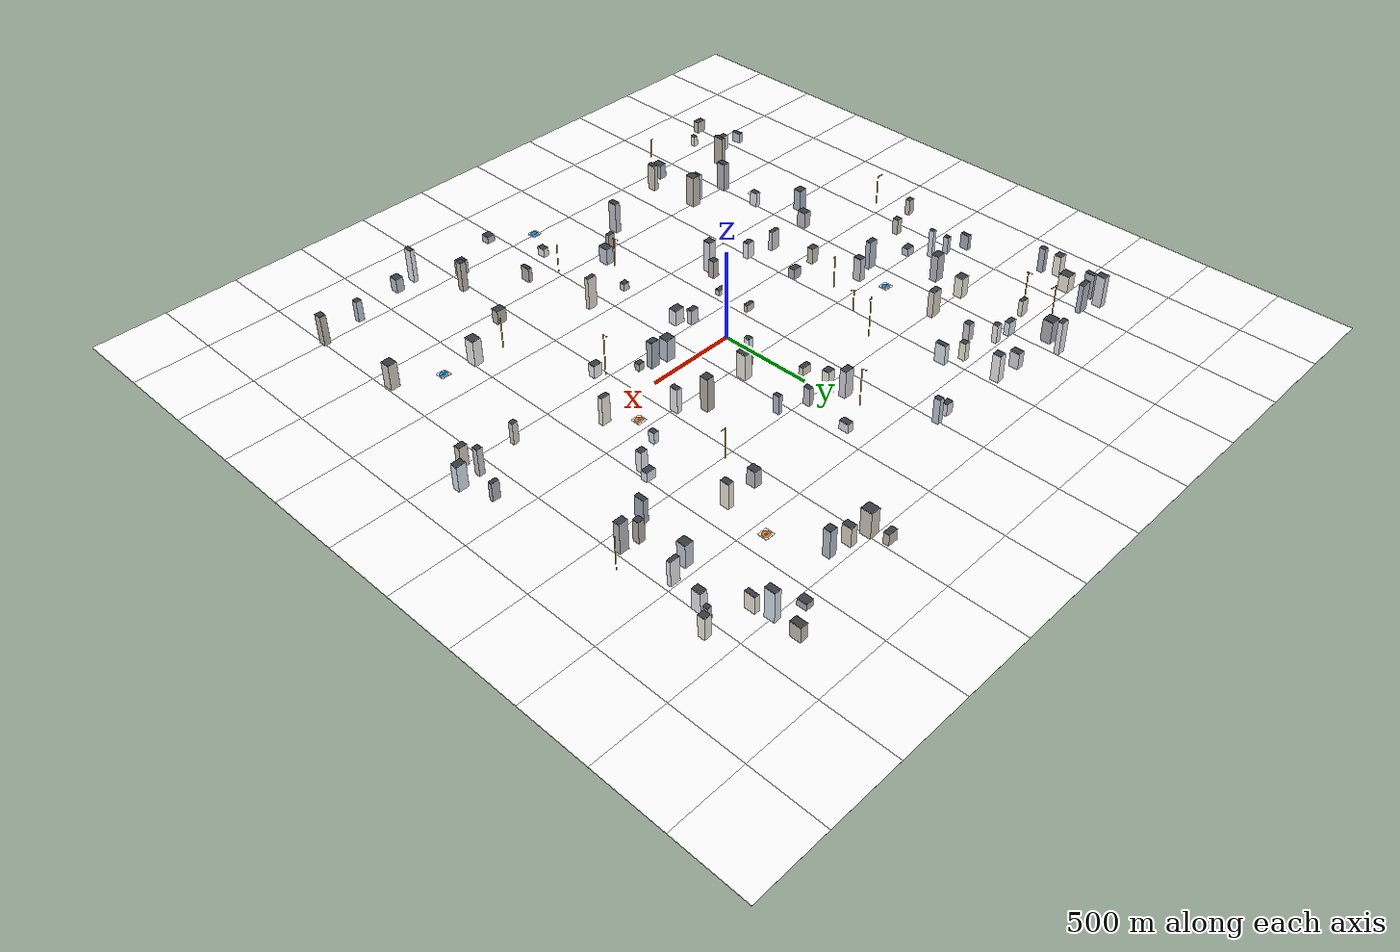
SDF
<?xml version='1.0'?>
<sdf version='1.9'>
<world name='urban'>
  <physics name='fast' type='ignored'>
    <max_step_size>0.005000</max_step_size>
    <real_time_factor>0</real_time_factor>
  </physics>
  <plugin filename='gz-sim-physics-system' name='gz::sim::systems::Physics'/>
  <plugin filename='gz-sim-user-commands-system'
          name='gz::sim::systems::UserCommands'/>
  <plugin filename='gz-sim-scene-broadcaster-system'
          name='gz::sim::systems::SceneBroadcaster'/>
  <plugin filename='gz-sim-sensors-system' name='gz::sim::systems::Sensors'>
    <render_engine>ogre2</render_engine>
  </plugin>
  <plugin filename='gz-sim-imu-system' name='gz::sim::systems::Imu'/>
  <plugin filename='PhyWamTraffic' name='phywam::PhyWamTraffic'>
    <seed>3</seed>
    <n_traffic>5</n_traffic>
    <n_suas>6</n_suas>
    <extent>1600.0</extent>
    <corridor_alt>120.0</corridor_alt>
    <namespace>phywam</namespace>
    <p_conflict>0.55</p_conflict>
    <buildings>-838.5,141.5,18.0,22.5,136.4 -1390.3,-1557.9,26.9,15.9,69.8 1586.1,-95.2,26.9,20.1,138.6 -1118.0,431.6,27.5,20.9,156.0 548.5,-1395.1,25.4,22.2,81.2 -1500.8,1169.7,20.0,24.7,179.4 685.2,1347.5,18.5,26.2,105.6 1393.9,1212.4,12.9,13.6,66.9 1489.5,-204.3,22.9,16.7,116.2 -365.2,-477.1,22.1,22.1,183.7 582.3,1372.6,27.3,29.8,144.1 -1078.1,1154.0,29.3,28.2,126.7 684.2,-924.4,26.8,21.9,78.4 -1396.9,1132.6,29.8,12.7,166.1 -286.5,-1117.6,16.6,25.6,178.4 -1458.6,366.5,11.9,24.7,86.3 1218.9,1538.0,20.6,30.0,82.6 -1353.7,319.2,11.6,14.8,99.3 353.5,-1100.2,11.8,27.5,83.4 1467.7,1269.3,18.2,19.7,118.4 460.4,306.1,21.6,22.8,189.9 22.5,-220.2,24.7,15.5,81.2 1529.0,67.6,21.4,11.2,100.6 255.9,-1535.8,22.7,23.0,40.2 407.5,-108.0,23.9,17.7,150.2 761.7,-1529.0,12.2,23.8,193.8 -796.4,-139.8,22.3,17.1,91.9 -599.5,-418.7,22.3,16.7,94.1 871.3,-1513.9,21.8,25.0,82.7 -887.9,972.2,15.5,14.6,104.0 633.8,-1274.1,17.1,17.3,171.7 -197.0,1137.7,14.2,17.4,140.5 1231.7,-156.5,15.3,13.3,120.0 -989.4,981.7,26.9,14.5,77.4 983.1,454.2,26.3,17.6,52.0 -665.8,940.4,16.2,17.6,100.9 -256.7,-289.5,28.5,14.0,30.8 1367.6,-889.3,25.2,26.9,142.7 60.8,-675.1,17.5,15.3,41.6 283.8,-681.6,26.4,11.9,183.6 -1557.9,785.0,14.3,16.7,142.7 79.9,-276.0,28.8,22.6,88.0 -792.1,1157.3,20.1,25.9,89.8 -968.5,110.8,26.5,14.3,164.6 1349.7,979.4,26.6,11.1,136.9 1160.2,-1440.2,16.2,16.1,119.6 -246.5,-86.7,25.8,11.0,39.3 -1194.0,-1201.2,12.3,29.5,175.3 -1324.4,6.8,17.0,17.0,89.7 -1204.0,177.7,24.6,18.2,43.6 -1028.6,-405.5,22.5,25.9,94.6 963.7,393.4,19.2,18.1,114.3 649.2,-254.4,24.2,19.8,71.7 114.7,624.5,12.4,19.1,102.4 1214.9,1396.7,18.1,28.1,164.5 1239.5,935.9,23.7,24.9,125.9 -1270.0,280.8,11.1,13.7,161.6 -1458.2,-1306.2,12.9,27.7,60.5 -1524.8,1092.9,13.3,27.0,144.5 1075.8,1447.7,22.0,26.2,36.2 855.7,36.2,24.6,13.0,157.3 1390.6,-1404.4,17.2,21.7,170.8 -825.2,-1024.7,15.7,22.7,158.1 -340.1,-424.1,18.5,17.7,101.1 -1086.0,610.7,25.4,23.8,117.9 -52.1,457.4,28.1,13.8,46.3 794.1,1333.2,20.8,19.4,152.2 -1004.4,-744.5,14.8,22.1,83.5 -856.6,611.6,29.1,16.6,149.9 -277.8,1131.6,22.1,16.1,67.0 -1526.0,-65.6,18.3,14.3,91.3 -569.5,877.5,13.7,29.8,111.5 316.8,-102.2,26.9,26.6,124.7 -59.8,706.3,27.3,18.6,154.7 1472.8,-104.3,15.4,15.5,152.0 561.1,1467.9,27.2,15.6,62.2 -772.4,-1001.0,24.4,27.3,183.0 -1325.0,-1303.5,26.8,16.5,90.6 257.0,561.6,11.1,17.4,104.2 -45.1,-927.7,22.1,29.2,96.5 141.9,-1218.6,16.2,23.6,49.1 1239.0,1308.0,12.8,28.9,93.6 871.7,823.4,16.6,23.8,141.2 979.4,-750.1,25.3,29.3,144.4 571.3,212.5,14.5,23.3,137.3 -1026.9,1247.7,23.5,13.3,188.4 -1147.6,-539.1,24.7,22.4,124.3 472.0,-135.3,16.9,14.4,41.7 690.7,814.3,21.3,25.1,91.1 -749.3,-373.2,27.6,11.8,115.8 -809.0,860.5,17.7,17.3,98.6 132.8,869.5,17.7,27.1,49.1 -734.4,-1281.1,13.1,25.8,153.6 -1008.5,-994.7,18.9,25.1,168.7 795.8,294.1,13.8,18.6,62.9 88.3,218.8,14.8,15.8,162.9 -1503.7,970.1,27.9,29.0,95.1 168.3,265.8,23.0,29.6,146.7 -641.9,1152.0,20.2,22.4,153.6 -1592.4,865.5,23.6,20.3,119.0 -126.3,-981.0,21.1,11.7,115.1 -1166.1,935.6,22.8,12.0,91.2 -853.1,-1350.9,21.2,28.7,84.9 1185.6,622.9,13.6,27.3,132.2 1366.3,691.0,25.1,17.5,167.1 1381.6,1156.7,19.3,25.4,112.5 -1250.8,-1463.4,12.5,14.8,57.3 -9.2,637.7,21.2,19.0,140.4 -625.1,-113.9,25.4,18.6,60.7 1278.1,703.0,18.0,18.0,120.0</buildings>
  </plugin>

  <gravity>0 0 -9.80665</gravity>
  <scene>
    <ambient>0.38 0.40 0.44 1</ambient>
    <background>0.46 0.60 0.78 1</background>
    <grid>false</grid><sky></sky>
  </scene>
  <light type='directional' name='sun'>
    <cast_shadows>true</cast_shadows>
    <pose>0 0 400 0 0 0</pose>
    <diffuse>0.88 0.86 0.80 1</diffuse><specular>0.18 0.18 0.18 1</specular>
    <direction>-0.42 0.38 -0.82</direction>
  </light>
  <model name='ground'><static>true</static>
    <link name='l'>
      <collision name='c'><geometry><plane><normal>0 0 1</normal>
      <size>9000 9000</size></plane></geometry></collision>
<visual name='g_0_0'><pose>-2000.0 -2000.0 -0.2 0 0 0</pose><geometry><box><size>400.0 400.0 0.4</size></box></geometry><material><ambient>0.5 0.5 0.5 1</ambient><diffuse>1.000 1.000 1.000 1</diffuse><specular>0.06 0.06 0.06 1</specular><pbr><metal><albedo_map>/home/glaze/Desktop/github_projects/Phy_WAM/sim/materials/textures/ground.png</albedo_map><metalness>0.0</metalness><roughness>0.95</roughness></metal></pbr></material></visual><visual name='g_1_0'><pose>-1600.0 -2000.0 -0.2 0 0 0</pose><geometry><box><size>400.0 400.0 0.4</size></box></geometry><material><ambient>0.5 0.5 0.5 1</ambient><diffuse>1.000 1.000 1.000 1</diffuse><specular>0.06 0.06 0.06 1</specular><pbr><metal><albedo_map>/home/glaze/Desktop/github_projects/Phy_WAM/sim/materials/textures/ground.png</albedo_map><metalness>0.0</metalness><roughness>0.95</roughness></metal></pbr></material></visual><visual name='g_2_0'><pose>-1200.0 -2000.0 -0.2 0 0 0</pose><geometry><box><size>400.0 400.0 0.4</size></box></geometry><material><ambient>0.5 0.5 0.5 1</ambient><diffuse>1.000 1.000 1.000 1</diffuse><specular>0.06 0.06 0.06 1</specular><pbr><metal><albedo_map>/home/glaze/Desktop/github_projects/Phy_WAM/sim/materials/textures/ground.png</albedo_map><metalness>0.0</metalness><roughness>0.95</roughness></metal></pbr></material></visual><visual name='g_3_0'><pose>-800.0 -2000.0 -0.2 0 0 0</pose><geometry><box><size>400.0 400.0 0.4</size></box></geometry><material><ambient>0.5 0.5 0.5 1</ambient><diffuse>1.000 1.000 1.000 1</diffuse><specular>0.06 0.06 0.06 1</specular><pbr><metal><albedo_map>/home/glaze/Desktop/github_projects/Phy_WAM/sim/materials/textures/ground.png</albedo_map><metalness>0.0</metalness><roughness>0.95</roughness></metal></pbr></material></visual><visual name='g_4_0'><pose>-400.0 -2000.0 -0.2 0 0 0</pose><geometry><box><size>400.0 400.0 0.4</size></box></geometry><material><ambient>0.5 0.5 0.5 1</ambient><diffuse>1.000 1.000 1.000 1</diffuse><specular>0.06 0.06 0.06 1</specular><pbr><metal><albedo_map>/home/glaze/Desktop/github_projects/Phy_WAM/sim/materials/textures/ground.png</albedo_map><metalness>0.0</metalness><roughness>0.95</roughness></metal></pbr></material></visual><visual name='g_5_0'><pose>0.0 -2000.0 -0.2 0 0 0</pose><geometry><box><size>400.0 400.0 0.4</size></box></geometry><material><ambient>0.5 0.5 0.5 1</ambient><diffuse>1.000 1.000 1.000 1</diffuse><specular>0.06 0.06 0.06 1</specular><pbr><metal><albedo_map>/home/glaze/Desktop/github_projects/Phy_WAM/sim/materials/textures/ground.png</albedo_map><metalness>0.0</metalness><roughness>0.95</roughness></metal></pbr></material></visual><visual name='g_6_0'><pose>400.0 -2000.0 -0.2 0 0 0</pose><geometry><box><size>400.0 400.0 0.4</size></box></geometry><material><ambient>0.5 0.5 0.5 1</ambient><diffuse>1.000 1.000 1.000 1</diffuse><specular>0.06 0.06 0.06 1</specular><pbr><metal><albedo_map>/home/glaze/Desktop/github_projects/Phy_WAM/sim/materials/textures/ground.png</albedo_map><metalness>0.0</metalness><roughness>0.95</roughness></metal></pbr></material></visual><visual name='g_7_0'><pose>800.0 -2000.0 -0.2 0 0 0</pose><geometry><box><size>400.0 400.0 0.4</size></box></geometry><material><ambient>0.5 0.5 0.5 1</ambient><diffuse>1.000 1.000 1.000 1</diffuse><specular>0.06 0.06 0.06 1</specular><pbr><metal><albedo_map>/home/glaze/Desktop/github_projects/Phy_WAM/sim/materials/textures/ground.png</albedo_map><metalness>0.0</metalness><roughness>0.95</roughness></metal></pbr></material></visual><visual name='g_8_0'><pose>1200.0 -2000.0 -0.2 0 0 0</pose><geometry><box><size>400.0 400.0 0.4</size></box></geometry><material><ambient>0.5 0.5 0.5 1</ambient><diffuse>1.000 1.000 1.000 1</diffuse><specular>0.06 0.06 0.06 1</specular><pbr><metal><albedo_map>/home/glaze/Desktop/github_projects/Phy_WAM/sim/materials/textures/ground.png</albedo_map><metalness>0.0</metalness><roughness>0.95</roughness></metal></pbr></material></visual><visual name='g_9_0'><pose>1600.0 -2000.0 -0.2 0 0 0</pose><geometry><box><size>400.0 400.0 0.4</size></box></geometry><material><ambient>0.5 0.5 0.5 1</ambient><diffuse>1.000 1.000 1.000 1</diffuse><specular>0.06 0.06 0.06 1</specular><pbr><metal><albedo_map>/home/glaze/Desktop/github_projects/Phy_WAM/sim/materials/textures/ground.png</albedo_map><metalness>0.0</metalness><roughness>0.95</roughness></metal></pbr></material></visual><visual name='g_10_0'><pose>2000.0 -2000.0 -0.2 0 0 0</pose><geometry><box><size>400.0 400.0 0.4</size></box></geometry><material><ambient>0.5 0.5 0.5 1</ambient><diffuse>1.000 1.000 1.000 1</diffuse><specular>0.06 0.06 0.06 1</specular><pbr><metal><albedo_map>/home/glaze/Desktop/github_projects/Phy_WAM/sim/materials/textures/ground.png</albedo_map><metalness>0.0</metalness><roughness>0.95</roughness></metal></pbr></material></visual><visual name='g_0_1'><pose>-2000.0 -1600.0 -0.2 0 0 0</pose><geometry><box><size>400.0 400.0 0.4</size></box></geometry><material><ambient>0.5 0.5 0.5 1</ambient><diffuse>1.000 1.000 1.000 1</diffuse><specular>0.06 0.06 0.06 1</specular><pbr><metal><albedo_map>/home/glaze/Desktop/github_projects/Phy_WAM/sim/materials/textures/ground.png</albedo_map><metalness>0.0</metalness><roughness>0.95</roughness></metal></pbr></material></visual><visual name='g_1_1'><pose>-1600.0 -1600.0 -0.2 0 0 0</pose><geometry><box><size>400.0 400.0 0.4</size></box></geometry><material><ambient>0.5 0.5 0.5 1</ambient><diffuse>1.000 1.000 1.000 1</diffuse><specular>0.06 0.06 0.06 1</specular><pbr><metal><albedo_map>/home/glaze/Desktop/github_projects/Phy_WAM/sim/materials/textures/ground.png</albedo_map><metalness>0.0</metalness><roughness>0.95</roughness></metal></pbr></material></visual><visual name='g_2_1'><pose>-1200.0 -1600.0 -0.2 0 0 0</pose><geometry><box><size>400.0 400.0 0.4</size></box></geometry><material><ambient>0.5 0.5 0.5 1</ambient><diffuse>1.000 1.000 1.000 1</diffuse><specular>0.06 0.06 0.06 1</specular><pbr><metal><albedo_map>/home/glaze/Desktop/github_projects/Phy_WAM/sim/materials/textures/ground.png</albedo_map><metalness>0.0</metalness><roughness>0.95</roughness></metal></pbr></material></visual><visual name='g_3_1'><pose>-800.0 -1600.0 -0.2 0 0 0</pose><geometry><box><size>400.0 400.0 0.4</size></box></geometry><material><ambient>0.5 0.5 0.5 1</ambient><diffuse>1.000 1.000 1.000 1</diffuse><specular>0.06 0.06 0.06 1</specular><pbr><metal><albedo_map>/home/glaze/Desktop/github_projects/Phy_WAM/sim/materials/textures/ground.png</albedo_map><metalness>0.0</metalness><roughness>0.95</roughness></metal></pbr></material></visual><visual name='g_4_1'><pose>-400.0 -1600.0 -0.2 0 0 0</pose><geometry><box><size>400.0 400.0 0.4</size></box></geometry><material><ambient>0.5 0.5 0.5 1</ambient><diffuse>1.000 1.000 1.000 1</diffuse><specular>0.06 0.06 0.06 1</specular><pbr><metal><albedo_map>/home/glaze/Desktop/github_projects/Phy_WAM/sim/materials/textures/ground.png</albedo_map><metalness>0.0</metalness><roughness>0.95</roughness></metal></pbr></material></visual><visual name='g_5_1'><pose>0.0 -1600.0 -0.2 0 0 0</pose><geometry><box><size>400.0 400.0 0.4</size></box></geometry><material><ambient>0.5 0.5 0.5 1</ambient><diffuse>1.000 1.000 1.000 1</diffuse><specular>0.06 0.06 0.06 1</specular><pbr><metal><albedo_map>/home/glaze/Desktop/github_projects/Phy_WAM/sim/materials/textures/ground.png</albedo_map><metalness>0.0</metalness><roughness>0.95</roughness></metal></pbr></material></visual><visual name='g_6_1'><pose>400.0 -1600.0 -0.2 0 0 0</pose><geometry><box><size>400.0 400.0 0.4</size></box></geometry><material><ambient>0.5 0.5 0.5 1</ambient><diffuse>1.000 1.000 1.000 1</diffuse><specular>0.06 0.06 0.06 1</specular><pbr><metal><albedo_map>/home/glaze/Desktop/github_projects/Phy_WAM/sim/materials/textures/ground.png</albedo_map><metalness>0.0</metalness><roughness>0.95</roughness></metal></pbr></material></visual><visual name='g_7_1'><pose>800.0 -1600.0 -0.2 0 0 0</pose><geometry><box><size>400.0 400.0 0.4</size></box></geometry><material><ambient>0.5 0.5 0.5 1</ambient><diffuse>1.000 1.000 1.000 1</diffuse><specular>0.06 0.06 0.06 1</specular><pbr><metal><albedo_map>/home/glaze/Desktop/github_projects/Phy_WAM/sim/materials/textures/ground.png</albedo_map><metalness>0.0</metalness><roughness>0.95</roughness></metal></pbr></material></visual><visual name='g_8_1'><pose>1200.0 -1600.0 -0.2 0 0 0</pose><geometry><box><size>400.0 400.0 0.4</size></box></geometry><material><ambient>0.5 0.5 0.5 1</ambient><diffuse>1.000 1.000 1.000 1</diffuse><specular>0.06 0.06 0.06 1</specular><pbr><metal><albedo_map>/home/glaze/Desktop/github_projects/Phy_WAM/sim/materials/textures/ground.png</albedo_map><metalness>0.0</metalness><roughness>0.95</roughness></metal></pbr></material></visual><visual name='g_9_1'><pose>1600.0 -1600.0 -0.2 0 0 0</pose><geometry><box><size>400.0 400.0 0.4</size></box></geometry><material><ambient>0.5 0.5 0.5 1</ambient><diffuse>1.000 1.000 1.000 1</diffuse><specular>0.06 0.06 0.06 1</specular><pbr><metal><albedo_map>/home/glaze/Desktop/github_projects/Phy_WAM/sim/materials/textures/ground.png</albedo_map><metalness>0.0</metalness><roughness>0.95</roughness></metal></pbr></material></visual><visual name='g_10_1'><pose>2000.0 -1600.0 -0.2 0 0 0</pose><geometry><box><size>400.0 400.0 0.4</size></box></geometry><material><ambient>0.5 0.5 0.5 1</ambient><diffuse>1.000 1.000 1.000 1</diffuse><specular>0.06 0.06 0.06 1</specular><pbr><metal><albedo_map>/home/glaze/Desktop/github_projects/Phy_WAM/sim/materials/textures/ground.png</albedo_map><metalness>0.0</metalness><roughness>0.95</roughness></metal></pbr></material></visual><visual name='g_0_2'><pose>-2000.0 -1200.0 -0.2 0 0 0</pose><geometry><box><size>400.0 400.0 0.4</size></box></geometry><material><ambient>0.5 0.5 0.5 1</ambient><diffuse>1.000 1.000 1.000 1</diffuse><specular>0.06 0.06 0.06 1</specular><pbr><metal><albedo_map>/home/glaze/Desktop/github_projects/Phy_WAM/sim/materials/textures/ground.png</albedo_map><metalness>0.0</metalness><roughness>0.95</roughness></metal></pbr></material></visual><visual name='g_1_2'><pose>-1600.0 -1200.0 -0.2 0 0 0</pose><geometry><box><size>400.0 400.0 0.4</size></box></geometry><material><ambient>0.5 0.5 0.5 1</ambient><diffuse>1.000 1.000 1.000 1</diffuse><specular>0.06 0.06 0.06 1</specular><pbr><metal><albedo_map>/home/glaze/Desktop/github_projects/Phy_WAM/sim/materials/textures/ground.png</albedo_map><metalness>0.0</metalness><roughness>0.95</roughness></metal></pbr></material></visual><visual name='g_2_2'><pose>-1200.0 -1200.0 -0.2 0 0 0</pose><geometry><box><size>400.0 400.0 0.4</size></box></geometry><material><ambient>0.5 0.5 0.5 1</ambient><diffuse>1.000 1.000 1.000 1</diffuse><specular>0.06 0.06 0.06 1</specular><pbr><metal><albedo_map>/home/glaze/Desktop/github_projects/Phy_WAM/sim/materials/textures/ground.png</albedo_map><metalness>0.0</metalness><roughness>0.95</roughness></metal></pbr></material></visual><visual name='g_3_2'><pose>-800.0 -1200.0 -0.2 0 0 0</pose><geometry><box><size>400.0 400.0 0.4</size></box></geometry><material><ambient>0.5 0.5 0.5 1</ambient><diffuse>1.000 1.000 1.000 1</diffuse><specular>0.06 0.06 0.06 1</specular><pbr><metal><albedo_map>/home/glaze/Desktop/github_projects/Phy_WAM/sim/materials/textures/ground.png</albedo_map><metalness>0.0</metalness><roughness>0.95</roughness></metal></pbr></material></visual><visual name='g_4_2'><pose>-400.0 -1200.0 -0.2 0 0 0</pose><geometry><box><size>400.0 400.0 0.4</size></box></geometry><material><ambient>0.5 0.5 0.5 1</ambient><diffuse>1.000 1.000 1.000 1</diffuse><specular>0.06 0.06 0.06 1</specular><pbr><metal><albedo_map>/home/glaze/Desktop/github_projects/Phy_WAM/sim/materials/textures/ground.png</albedo_map><metalness>0.0</metalness><roughness>0.95</roughness></metal></pbr></material></visual><visual name='g_5_2'><pose>0.0 -1200.0 -0.2 0 0 0</pose><geometry><box><size>400.0 400.0 0.4</size></box></geometry><material><ambient>0.5 0.5 0.5 1</ambient><diffuse>1.000 1.000 1.000 1</diffuse><specular>0.06 0.06 0.06 1</specular><pbr><metal><albedo_map>/home/glaze/Desktop/github_projects/Phy_WAM/sim/materials/textures/ground.png</albedo_map><metalness>0.0</metalness><roughness>0.95</roughness></metal></pbr></material></visual><visual name='g_6_2'><pose>400.0 -1200.0 -0.2 0 0 0</pose><geometry><box><size>400.0 400.0 0.4</size></box></geometry><material><ambient>0.5 0.5 0.5 1</ambient><diffuse>1.000 1.000 1.000 1</diffuse><specular>0.06 0.06 0.06 1</specular><pbr><metal><albedo_map>/home/glaze/Desktop/github_projects/Phy_WAM/sim/materials/textures/ground.png</albedo_map><metalness>0.0</metalness><roughness>0.95</roughness></metal></pbr></material></visual><visual name='g_7_2'><pose>800.0 -1200.0 -0.2 0 0 0</pose><geometry><box><size>400.0 400.0 0.4</size></box></geometry><material><ambient>0.5 0.5 0.5 1</ambient><diffuse>1.000 1.000 1.000 1</diffuse><specular>0.06 0.06 0.06 1</specular><pbr><metal><albedo_map>/home/glaze/Desktop/github_projects/Phy_WAM/sim/materials/textures/ground.png</albedo_map><metalness>0.0</metalness><roughness>0.95</roughness></metal></pbr></material></visual><visual name='g_8_2'><pose>1200.0 -1200.0 -0.2 0 0 0</pose><geometry><box><size>400.0 400.0 0.4</size></box></geometry><material><ambient>0.5 0.5 0.5 1</ambient><diffuse>1.000 1.000 1.000 1</diffuse><specular>0.06 0.06 0.06 1</specular><pbr><metal><albedo_map>/home/glaze/Desktop/github_projects/Phy_WAM/sim/materials/textures/ground.png</albedo_map><metalness>0.0</metalness><roughness>0.95</roughness></metal></pbr></material></visual><visual name='g_9_2'><pose>1600.0 -1200.0 -0.2 0 0 0</pose><geometry><box><size>400.0 400.0 0.4</size></box></geometry><material><ambient>0.5 0.5 0.5 1</ambient><diffuse>1.000 1.000 1.000 1</diffuse><specular>0.06 0.06 0.06 1</specular><pbr><metal><albedo_map>/home/glaze/Desktop/github_projects/Phy_WAM/sim/materials/textures/ground.png</albedo_map><metalness>0.0</metalness><roughness>0.95</roughness></metal></pbr></material></visual><visual name='g_10_2'><pose>2000.0 -1200.0 -0.2 0 0 0</pose><geometry><box><size>400.0 400.0 0.4</size></box></geometry><material><ambient>0.5 0.5 0.5 1</ambient><diffuse>1.000 1.000 1.000 1</diffuse><specular>0.06 0.06 0.06 1</specular><pbr><metal><albedo_map>/home/glaze/Desktop/github_projects/Phy_WAM/sim/materials/textures/ground.png</albedo_map><metalness>0.0</metalness><roughness>0.95</roughness></metal></pbr></material></visual><visual name='g_0_3'><pose>-2000.0 -800.0 -0.2 0 0 0</pose><geometry><box><size>400.0 400.0 0.4</size></box></geometry><material><ambient>0.5 0.5 0.5 1</ambient><diffuse>1.000 1.000 1.000 1</diffuse><specular>0.06 0.06 0.06 1</specular><pbr><metal><albedo_map>/home/glaze/Desktop/github_projects/Phy_WAM/sim/materials/textures/ground.png</albedo_map><metalness>0.0</metalness><roughness>0.95</roughness></metal></pbr></material></visual><visual name='g_1_3'><pose>-1600.0 -800.0 -0.2 0 0 0</pose><geometry><box><size>400.0 400.0 0.4</size></box></geometry><material><ambient>0.5 0.5 0.5 1</ambient><diffuse>1.000 1.000 1.000 1</diffuse><specular>0.06 0.06 0.06 1</specular><pbr><metal><albedo_map>/home/glaze/Desktop/github_projects/Phy_WAM/sim/materials/textures/ground.png</albedo_map><metalness>0.0</metalness><roughness>0.95</roughness></metal></pbr></material></visual><visual name='g_2_3'><pose>-1200.0 -800.0 -0.2 0 0 0</pose><geometry><box><size>400.0 400.0 0.4</size></box></geometry><material><ambient>0.5 0.5 0.5 1</ambient><diffuse>1.000 1.000 1.000 1</diffuse><specular>0.06 0.06 0.06 1</specular><pbr><metal><albedo_map>/home/glaze/Desktop/github_projects/Phy_WAM/sim/materials/textures/ground.png</albedo_map><metalness>0.0</metalness><roughness>0.95</roughness></metal></pbr></material></visual><visual name='g_3_3'><pose>-800.0 -800.0 -0.2 0 0 0</pose><geometry><box><size>400.0 400.0 0.4</size></box></geometry><material><ambient>0.5 0.5 0.5 1</ambient><diffuse>1.000 1.000 1.000 1</diffuse><specular>0.06 0.06 0.06 1</specular><pbr><metal><albedo_map>/home/glaze/Desktop/github_projects/Phy_WAM/sim/materials/textures/ground.png</albedo_map><metalness>0.0</metalness><roughness>0.95</roughness></metal></pbr></material></visual><visual name='g_4_3'><pose>-400.0 -800.0 -0.2 0 0 0</pose><geometry><box><size>400.0 400.0 0.4</size></box></geometry><material><ambient>0.5 0.5 0.5 1</ambient><diffuse>1.000 1.000 1.000 1</diffuse><specular>0.06 0.06 0.06 1</specular><pbr><metal><albedo_map>/home/glaze/Desktop/github_projects/Phy_WAM/sim/materials/textures/ground.png</albedo_map><metalness>0.0</metalness><roughness>0.95</roughness></metal></pbr></material></visual><visual name='g_5_3'><pose>0.0 -800.0 -0.2 0 0 0</pose><geometry><box><size>400.0 400.0 0.4</size></box></geometry><material><ambient>0.5 0.5 0.5 1</ambient><diffuse>1.000 1.000 1.000 1</diffuse><specular>0.06 0.06 0.06 1</specular><pbr><metal><albedo_map>/home/glaze/Desktop/github_projects/Phy_WAM/sim/materials/textures/ground.png</albedo_map><metalness>0.0</metalness><roughness>0.95</roughness></metal></pbr></material></visual><visual name='g_6_3'><pose>400.0 -800.0 -0.2 0 0 0</pose><geometry><box><size>400.0 400.0 0.4</size></box></geometry><material><ambient>0.5 0.5 0.5 1</ambient><diffuse>1.000 1.000 1.000 1</diffuse><specular>0.06 0.06 0.06 1</specular><pbr><metal><albedo_map>/home/glaze/Desktop/github_projects/Phy_WAM/sim/materials/textures/ground.png</albedo_map><metalness>0.0</metalness><roughness>0.95</roughness></metal></pbr></material></visual><visual name='g_7_3'><pose>800.0 -800.0 -0.2 0 0 0</pose><geometry><box><size>400.0 400.0 0.4</size></box></geometry><material><ambient>0.5 0.5 0.5 1</ambient><diffuse>1.000 1.000 1.000 1</diffuse><specular>0.06 0.06 0.06 1</specular><pbr><metal><albedo_map>/home/glaze/Desktop/github_projects/Phy_WAM/sim/materials/textures/ground.png</albedo_map><metalness>0.0</metalness><roughness>0.95</roughness></metal></pbr></material></visual><visual name='g_8_3'><pose>1200.0 -800.0 -0.2 0 0 0</pose><geometry><box><size>400.0 400.0 0.4</size></box></geometry><material><ambient>0.5 0.5 0.5 1</ambient><diffuse>1.000 1.000 1.000 1</diffuse><specular>0.06 0.06 0.06 1</specular><pbr><metal><albedo_map>/home/glaze/Desktop/github_projects/Phy_WAM/sim/materials/textures/ground.png</albedo_map><metalness>0.0</metalness><roughness>0.95</roughness></metal></pbr></material></visual><visual name='g_9_3'><pose>1600.0 -800.0 -0.2 0 0 0</pose><geometry><box><size>400.0 400.0 0.4</size></box></geometry><material><ambient>0.5 0.5 0.5 1</ambient><diffuse>1.000 1.000 1.000 1</diffuse><specular>0.06 0.06 0.06 1</specular><pbr><metal><albedo_map>/home/glaze/Desktop/github_projects/Phy_WAM/sim/materials/textures/ground.png</albedo_map><metalness>0.0</metalness><roughness>0.95</roughness></metal></pbr></material></visual><visual name='g_10_3'><pose>2000.0 -800.0 -0.2 0 0 0</pose><geometry><box><size>400.0 400.0 0.4</size></box></geometry><material><ambient>0.5 0.5 0.5 1</ambient><diffuse>1.000 1.000 1.000 1</diffuse><specular>0.06 0.06 0.06 1</specular><pbr><metal><albedo_map>/home/glaze/Desktop/github_projects/Phy_WAM/sim/materials/textures/ground.png</albedo_map><metalness>0.0</metalness><roughness>0.95</roughness></metal></pbr></material></visual><visual name='g_0_4'><pose>-2000.0 -400.0 -0.2 0 0 0</pose><geometry><box><size>400.0 400.0 0.4</size></box></geometry><material><ambient>0.5 0.5 0.5 1</ambient><diffuse>1.000 1.000 1.000 1</diffuse><specular>0.06 0.06 0.06 1</specular><pbr><metal><albedo_map>/home/glaze/Desktop/github_projects/Phy_WAM/sim/materials/textures/ground.png</albedo_map><metalness>0.0</metalness><roughness>0.95</roughness></metal></pbr></material></visual><visual name='g_1_4'><pose>-1600.0 -400.0 -0.2 0 0 0</pose><geometry><box><size>400.0 400.0 0.4</size></box></geometry><material><ambient>0.5 0.5 0.5 1</ambient><diffuse>1.000 1.000 1.000 1</diffuse><specular>0.06 0.06 0.06 1</specular><pbr><metal><albedo_map>/home/glaze/Desktop/github_projects/Phy_WAM/sim/materials/textures/ground.png</albedo_map><metalness>0.0</metalness><roughness>0.95</roughness></metal></pbr></material></visual><visual name='g_2_4'><pose>-1200.0 -400.0 -0.2 0 0 0</pose><geometry><box><size>400.0 400.0 0.4</size></box></geometry><material><ambient>0.5 0.5 0.5 1</ambient><diffuse>1.000 1.000 1.000 1</diffuse><specular>0.06 0.06 0.06 1</specular><pbr><metal><albedo_map>/home/glaze/Desktop/github_projects/Phy_WAM/sim/materials/textures/ground.png</albedo_map><metalness>0.0</metalness><roughness>0.95</roughness></metal></pbr></material></visual><visual name='g_3_4'><pose>-800.0 -400.0 -0.2 0 0 0</pose><geometry><box><size>400.0 400.0 0.4</size></box></geometry><material><ambient>0.5 0.5 0.5 1</ambient><diffuse>1.000 1.000 1.000 1</diffuse><specular>0.06 0.06 0.06 1</specular><pbr><metal><albedo_map>/home/glaze/Desktop/github_projects/Phy_WAM/sim/materials/textures/ground.png</albedo_map><metalness>0.0</metalness><roughness>0.95</roughness></metal></pbr></material></visual><visual name='g_4_4'><pose>-400.0 -400.0 -0.2 0 0 0</pose><geometry><box><size>400.0 400.0 0.4</size></box></geometry><material><ambient>0.5 0.5 0.5 1</ambient><diffuse>1.000 1.000 1.000 1</diffuse><specular>0.06 0.06 0.06 1</specular><pbr><metal><albedo_map>/home/glaze/Desktop/github_projects/Phy_WAM/sim/materials/textures/ground.png</albedo_map><metalness>0.0</metalness><roughness>0.95</roughness></metal></pbr></material></visual><visual name='g_5_4'><pose>0.0 -400.0 -0.2 0 0 0</pose><geometry><box><size>400.0 400.0 0.4</size></box></geometry><material><ambient>0.5 0.5 0.5 1</ambient><diffuse>1.000 1.000 1.000 1</diffuse><specular>0.06 0.06 0.06 1</specular><pbr><metal><albedo_map>/home/glaze/Desktop/github_projects/Phy_WAM/sim/materials/textures/ground.png</albedo_map><metalness>0.0</metalness><roughness>0.95</roughness></metal></pbr></material></visual><visual name='g_6_4'><pose>400.0 -400.0 -0.2 0 0 0</pose><geometry><box><size>400.0 400.0 0.4</size></box></geometry><material><ambient>0.5 0.5 0.5 1</ambient><diffuse>1.000 1.000 1.000 1</diffuse><specular>0.06 0.06 0.06 1</specular><pbr><metal><albedo_map>/home/glaze/Desktop/github_projects/Phy_WAM/sim/materials/textures/ground.png</albedo_map><metalness>0.0</metalness><roughness>0.95</roughness></metal></pbr></material></visual><visual name='g_7_4'><pose>800.0 -400.0 -0.2 0 0 0</pose><geometry><box><size>400.0 400.0 0.4</size></box></geometry><material><ambient>0.5 0.5 0.5 1</ambient><diffuse>1.000 1.000 1.000 1</diffuse><specular>0.06 0.06 0.06 1</specular><pbr><metal><albedo_map>/home/glaze/Desktop/github_projects/Phy_WAM/sim/materials/textures/ground.png</albedo_map><metalness>0.0</metalness><roughness>0.95</roughness></metal></pbr></material></visual><visual name='g_8_4'><pose>1200.0 -400.0 -0.2 0 0 0</pose><geometry><box><size>400.0 400.0 0.4</size></box></geometry><material><ambient>0.5 0.5 0.5 1</ambient><diffuse>1.000 1.000 1.000 1</diffuse><specular>0.06 0.06 0.06 1</specular><pbr><metal><albedo_map>/home/glaze/Desktop/github_projects/Phy_WAM/sim/materials/textures/ground.png</albedo_map><metalness>0.0</metalness><roughness>0.95</roughness></metal></pbr></material></visual><visual name='g_9_4'><pose>1600.0 -400.0 -0.2 0 0 0</pose><geometry><box><size>400.0 400.0 0.4</size></box></geometry><material><ambient>0.5 0.5 0.5 1</ambient><diffuse>1.000 1.000 1.000 1</diffuse><specular>0.06 0.06 0.06 1</specular><pbr><metal><albedo_map>/home/glaze/Desktop/github_projects/Phy_WAM/sim/materials/textures/ground.png</albedo_map><metalness>0.0</metalness><roughness>0.95</roughness></metal></pbr></material></visual><visual name='g_10_4'><pose>2000.0 -400.0 -0.2 0 0 0</pose><geometry><box><size>400.0 400.0 0.4</size></box></geometry><material><ambient>0.5 0.5 0.5 1</ambient><diffuse>1.000 1.000 1.000 1</diffuse><specular>0.06 0.06 0.06 1</specular><pbr><metal><albedo_map>/home/glaze/Desktop/github_projects/Phy_WAM/sim/materials/textures/ground.png</albedo_map><metalness>0.0</metalness><roughness>0.95</roughness></metal></pbr></material></visual><visual name='g_0_5'><pose>-2000.0 0.0 -0.2 0 0 0</pose><geometry><box><size>400.0 400.0 0.4</size></box></geometry><material><ambient>0.5 0.5 0.5 1</ambient><diffuse>1.000 1.000 1.000 1</diffuse><specular>0.06 0.06 0.06 1</specular><pbr><metal><albedo_map>/home/glaze/Desktop/github_projects/Phy_WAM/sim/materials/textures/ground.png</albedo_map><metalness>0.0</metalness><roughness>0.95</roughness></metal></pbr></material></visual><visual name='g_1_5'><pose>-1600.0 0.0 -0.2 0 0 0</pose><geometry><box><size>400.0 400.0 0.4</size></box></geometry><material><ambient>0.5 0.5 0.5 1</ambient><diffuse>1.000 1.000 1.000 1</diffuse><specular>0.06 0.06 0.06 1</specular><pbr><metal><albedo_map>/home/glaze/Desktop/github_projects/Phy_WAM/sim/materials/textures/ground.png</albedo_map><metalness>0.0</metalness><roughness>0.95</roughness></metal></pbr></material></visual><visual name='g_2_5'><pose>-1200.0 0.0 -0.2 0 0 0</pose><geometry><box><size>400.0 400.0 0.4</size></box></geometry><material><ambient>0.5 0.5 0.5 1</ambient><diffuse>1.000 1.000 1.000 1</diffuse><specular>0.06 0.06 0.06 1</specular><pbr><metal><albedo_map>/home/glaze/Desktop/github_projects/Phy_WAM/sim/materials/textures/ground.png</albedo_map><metalness>0.0</metalness><roughness>0.95</roughness></metal></pbr></material></visual><visual name='g_3_5'><pose>-800.0 0.0 -0.2 0 0 0</pose><geometry><box><size>400.0 400.0 0.4</size></box></geometry><material><ambient>0.5 0.5 0.5 1</ambient><diffuse>1.000 1.000 1.000 1</diffuse><specular>0.06 0.06 0.06 1</specular><pbr><metal><albedo_map>/home/glaze/Desktop/github_projects/Phy_WAM/sim/materials/textures/ground.png</albedo_map><metalness>0.0</metalness><roughness>0.95</roughness></metal></pbr></material></visual><visual name='g_4_5'><pose>-400.0 0.0 -0.2 0 0 0</pose><geometry><box><size>400.0 400.0 0.4</size></box></geometry><material><ambient>0.5 0.5 0.5 1</ambient><diffuse>1.000 1.000 1.000 1</diffuse><specular>0.06 0.06 0.06 1</specular><pbr><metal><albedo_map>/home/glaze/Desktop/github_projects/Phy_WAM/sim/materials/textures/ground.png</albedo_map><metalness>0.0</metalness><roughness>0.95</roughness></metal></pbr></material></visual><visual name='g_5_5'><pose>0.0 0.0 -0.2 0 0 0</pose><geometry><box><size>400.0 400.0 0.4</size></box></geometry><material><ambient>0.5 0.5 0.5 1</ambient><diffuse>1.000 1.000 1.000 1</diffuse><specular>0.06 0.06 0.06 1</specular><pbr><metal><albedo_map>/home/glaze/Desktop/github_projects/Phy_WAM/sim/materials/textures/ground.png</albedo_map><metalness>0.0</metalness><roughness>0.95</roughness></metal></pbr></material></visual><visual name='g_6_5'><pose>400.0 0.0 -0.2 0 0 0</pose><geometry><box><size>400.0 400.0 0.4</size></box></geometry><material><ambient>0.5 0.5 0.5 1</ambient><diffuse>1.000 1.000 1.000 1</diffuse><specular>0.06 0.06 0.06 1</specular><pbr><metal><albedo_map>/home/glaze/Desktop/github_projects/Phy_WAM/sim/materials/textures/ground.png</albedo_map><metalness>0.0</metalness><roughness>0.95</roughness></metal></pbr></material></visual><visual name='g_7_5'><pose>800.0 0.0 -0.2 0 0 0</pose><geometry><box><size>400.0 400.0 0.4</size></box></geometry><material><ambient>0.5 0.5 0.5 1</ambient><diffuse>1.000 1.000 1.000 1</diffuse><specular>0.06 0.06 0.06 1</specular><pbr><metal><albedo_map>/home/glaze/Desktop/github_projects/Phy_WAM/sim/materials/textures/ground.png</albedo_map><metalness>0.0</metalness><roughness>0.95</roughness></metal></pbr></material></visual><visual name='g_8_5'><pose>1200.0 0.0 -0.2 0 0 0</pose><geometry><box><size>400.0 400.0 0.4</size></box></geometry><material><ambient>0.5 0.5 0.5 1</ambient><diffuse>1.000 1.000 1.000 1</diffuse><specular>0.06 0.06 0.06 1</specular><pbr><metal><albedo_map>/home/glaze/Desktop/github_projects/Phy_WAM/sim/materials/textures/ground.png</albedo_map><metalness>0.0</metalness><roughness>0.95</roughness></metal></pbr></material></visual><visual name='g_9_5'><pose>1600.0 0.0 -0.2 0 0 0</pose><geometry><box><size>400.0 400.0 0.4</size></box></geometry><material><ambient>0.5 0.5 0.5 1</ambient><diffuse>1.000 1.000 1.000 1</diffuse><specular>0.06 0.06 0.06 1</specular><pbr><metal><albedo_map>/home/glaze/Desktop/github_projects/Phy_WAM/sim/materials/textures/ground.png</albedo_map><metalness>0.0</metalness><roughness>0.95</roughness></metal></pbr></material></visual><visual name='g_10_5'><pose>2000.0 0.0 -0.2 0 0 0</pose><geometry><box><size>400.0 400.0 0.4</size></box></geometry><material><ambient>0.5 0.5 0.5 1</ambient><diffuse>1.000 1.000 1.000 1</diffuse><specular>0.06 0.06 0.06 1</specular><pbr><metal><albedo_map>/home/glaze/Desktop/github_projects/Phy_WAM/sim/materials/textures/ground.png</albedo_map><metalness>0.0</metalness><roughness>0.95</roughness></metal></pbr></material></visual><visual name='g_0_6'><pose>-2000.0 400.0 -0.2 0 0 0</pose><geometry><box><size>400.0 400.0 0.4</size></box></geometry><material><ambient>0.5 0.5 0.5 1</ambient><diffuse>1.000 1.000 1.000 1</diffuse><specular>0.06 0.06 0.06 1</specular><pbr><metal><albedo_map>/home/glaze/Desktop/github_projects/Phy_WAM/sim/materials/textures/ground.png</albedo_map><metalness>0.0</metalness><roughness>0.95</roughness></metal></pbr></material></visual><visual name='g_1_6'><pose>-1600.0 400.0 -0.2 0 0 0</pose><geometry><box><size>400.0 400.0 0.4</size></box></geometry><material><ambient>0.5 0.5 0.5 1</ambient><diffuse>1.000 1.000 1.000 1</diffuse><specular>0.06 0.06 0.06 1</specular><pbr><metal><albedo_map>/home/glaze/Desktop/github_projects/Phy_WAM/sim/materials/textures/ground.png</albedo_map><metalness>0.0</metalness><roughness>0.95</roughness></metal></pbr></material></visual><visual name='g_2_6'><pose>-1200.0 400.0 -0.2 0 0 0</pose><geometry><box><size>400.0 400.0 0.4</size></box></geometry><material><ambient>0.5 0.5 0.5 1</ambient><diffuse>1.000 1.000 1.000 1</diffuse><specular>0.06 0.06 0.06 1</specular><pbr><metal><albedo_map>/home/glaze/Desktop/github_projects/Phy_WAM/sim/materials/textures/ground.png</albedo_map><metalness>0.0</metalness><roughness>0.95</roughness></metal></pbr></material></visual><visual name='g_3_6'><pose>-800.0 400.0 -0.2 0 0 0</pose><geometry><box><size>400.0 400.0 0.4</size></box></geometry><material><ambient>0.5 0.5 0.5 1</ambient><diffuse>1.000 1.000 1.000 1</diffuse><specular>0.06 0.06 0.06 1</specular><pbr><metal><albedo_map>/home/glaze/Desktop/github_projects/Phy_WAM/sim/materials/textures/ground.png</albedo_map><metalness>0.0</metalness><roughness>0.95</roughness></metal></pbr></material></visual><visual name='g_4_6'><pose>-400.0 400.0 -0.2 0 0 0</pose><geometry><box><size>400.0 400.0 0.4</size></box></geometry><material><ambient>0.5 0.5 0.5 1</ambient><diffuse>1.000 1.000 1.000 1</diffuse><specular>0.06 0.06 0.06 1</specular><pbr><metal><albedo_map>/home/glaze/Desktop/github_projects/Phy_WAM/sim/materials/textures/ground.png</albedo_map><metalness>0.0</metalness><roughness>0.95</roughness></metal></pbr></material></visual><visual name='g_5_6'><pose>0.0 400.0 -0.2 0 0 0</pose><geometry><box><size>400.0 400.0 0.4</size></box></geometry><material><ambient>0.5 0.5 0.5 1</ambient><diffuse>1.000 1.000 1.000 1</diffuse><specular>0.06 0.06 0.06 1</specular><pbr><metal><albedo_map>/home/glaze/Desktop/github_projects/Phy_WAM/sim/materials/textures/ground.png</albedo_map><metalness>0.0</metalness><roughness>0.95</roughness></metal></pbr></material></visual><visual name='g_6_6'><pose>400.0 400.0 -0.2 0 0 0</pose><geometry><box><size>400.0 400.0 0.4</size></box></geometry><material><ambient>0.5 0.5 0.5 1</ambient><diffuse>1.000 1.000 1.000 1</diffuse><specular>0.06 0.06 0.06 1</specular><pbr><metal><albedo_map>/home/glaze/Desktop/github_projects/Phy_WAM/sim/materials/textures/ground.png</albedo_map><metalness>0.0</metalness><roughness>0.95</roughness></metal></pbr></material></visual><visual name='g_7_6'><pose>800.0 400.0 -0.2 0 0 0</pose><geometry><box><size>400.0 400.0 0.4</size></box></geometry><material><ambient>0.5 0.5 0.5 1</ambient><diffuse>1.000 1.000 1.000 1</diffuse><specular>0.06 0.06 0.06 1</specular><pbr><metal><albedo_map>/home/glaze/Desktop/github_projects/Phy_WAM/sim/materials/textures/ground.png</albedo_map><metalness>0.0</metalness><roughness>0.95</roughness></metal></pbr></material></visual><visual name='g_8_6'><pose>1200.0 400.0 -0.2 0 0 0</pose><geometry><box><size>400.0 400.0 0.4</size></box></geometry><material><ambient>0.5 0.5 0.5 1</ambient><diffuse>1.000 1.000 1.000 1</diffuse><specular>0.06 0.06 0.06 1</specular><pbr><metal><albedo_map>/home/glaze/Desktop/github_projects/Phy_WAM/sim/materials/textures/ground.png</albedo_map><metalness>0.0</metalness><roughness>0.95</roughness></metal></pbr></material></visual><visual name='g_9_6'><pose>1600.0 400.0 -0.2 0 0 0</pose><geometry><box><size>400.0 400.0 0.4</size></box></geometry><material><ambient>0.5 0.5 0.5 1</ambient><diffuse>1.000 1.000 1.000 1</diffuse><specular>0.06 0.06 0.06 1</specular><pbr><metal><albedo_map>/home/glaze/Desktop/github_projects/Phy_WAM/sim/materials/textures/ground.png</albedo_map><metalness>0.0</metalness><roughness>0.95</roughness></metal></pbr></material></visual><visual name='g_10_6'><pose>2000.0 400.0 -0.2 0 0 0</pose><geometry><box><size>400.0 400.0 0.4</size></box></geometry><material><ambient>0.5 0.5 0.5 1</ambient><diffuse>1.000 1.000 1.000 1</diffuse><specular>0.06 0.06 0.06 1</specular><pbr><metal><albedo_map>/home/glaze/Desktop/github_projects/Phy_WAM/sim/materials/textures/ground.png</albedo_map><metalness>0.0</metalness><roughness>0.95</roughness></metal></pbr></material></visual><visual name='g_0_7'><pose>-2000.0 800.0 -0.2 0 0 0</pose><geometry><box><size>400.0 400.0 0.4</size></box></geometry><material><ambient>0.5 0.5 0.5 1</ambient><diffuse>1.000 1.000 1.000 1</diffuse><specular>0.06 0.06 0.06 1</specular><pbr><metal><albedo_map>/home/glaze/Desktop/github_projects/Phy_WAM/sim/materials/textures/ground.png</albedo_map><metalness>0.0</metalness><roughness>0.95</roughness></metal></pbr></material></visual><visual name='g_1_7'><pose>-1600.0 800.0 -0.2 0 0 0</pose><geometry><box><size>400.0 400.0 0.4</size></box></geometry><material><ambient>0.5 0.5 0.5 1</ambient><diffuse>1.000 1.000 1.000 1</diffuse><specular>0.06 0.06 0.06 1</specular><pbr><metal><albedo_map>/home/glaze/Desktop/github_projects/Phy_WAM/sim/materials/textures/ground.png</albedo_map><metalness>0.0</metalness><roughness>0.95</roughness></metal></pbr></material></visual><visual name='g_2_7'><pose>-1200.0 800.0 -0.2 0 0 0</pose><geometry><box><size>400.0 400.0 0.4</size></box></geometry><material><ambient>0.5 0.5 0.5 1</ambient><diffuse>1.000 1.000 1.000 1</diffuse><specular>0.06 0.06 0.06 1</specular><pbr><metal><albedo_map>/home/glaze/Desktop/github_projects/Phy_WAM/sim/materials/textures/ground.png</albedo_map><metalness>0.0</metalness><roughness>0.95</roughness></metal></pbr></material></visual><visual name='g_3_7'><pose>-800.0 800.0 -0.2 0 0 0</pose><geometry><box><size>400.0 400.0 0.4</size></box></geometry><material><ambient>0.5 0.5 0.5 1</ambient><diffuse>1.000 1.000 1.000 1</diffuse><specular>0.06 0.06 0.06 1</specular><pbr><metal><albedo_map>/home/glaze/Desktop/github_projects/Phy_WAM/sim/materials/textures/ground.png</albedo_map><metalness>0.0</metalness><roughness>0.95</roughness></metal></pbr></material></visual><visual name='g_4_7'><pose>-400.0 800.0 -0.2 0 0 0</pose><geometry><box><size>400.0 400.0 0.4</size></box></geometry><material><ambient>0.5 0.5 0.5 1</ambient><diffuse>1.000 1.000 1.000 1</diffuse><specular>0.06 0.06 0.06 1</specular><pbr><metal><albedo_map>/home/glaze/Desktop/github_projects/Phy_WAM/sim/materials/textures/ground.png</albedo_map><metalness>0.0</metalness><roughness>0.95</roughness></metal></pbr></material></visual><visual name='g_5_7'><pose>0.0 800.0 -0.2 0 0 0</pose><geometry><box><size>400.0 400.0 0.4</size></box></geometry><material><ambient>0.5 0.5 0.5 1</ambient><diffuse>1.000 1.000 1.000 1</diffuse><specular>0.06 0.06 0.06 1</specular><pbr><metal><albedo_map>/home/glaze/Desktop/github_projects/Phy_WAM/sim/materials/textures/ground.png</albedo_map><metalness>0.0</metalness><roughness>0.95</roughness></metal></pbr></material></visual><visual name='g_6_7'><pose>400.0 800.0 -0.2 0 0 0</pose><geometry><box><size>400.0 400.0 0.4</size></box></geometry><material><ambient>0.5 0.5 0.5 1</ambient><diffuse>1.000 1.000 1.000 1</diffuse><specular>0.06 0.06 0.06 1</specular><pbr><metal><albedo_map>/home/glaze/Desktop/github_projects/Phy_WAM/sim/materials/textures/ground.png</albedo_map><metalness>0.0</metalness><roughness>0.95</roughness></metal></pbr></material></visual><visual name='g_7_7'><pose>800.0 800.0 -0.2 0 0 0</pose><geometry><box><size>400.0 400.0 0.4</size></box></geometry><material><ambient>0.5 0.5 0.5 1</ambient><diffuse>1.000 1.000 1.000 1</diffuse><specular>0.06 0.06 0.06 1</specular><pbr><metal><albedo_map>/home/glaze/Desktop/github_projects/Phy_WAM/sim/materials/textures/ground.png</albedo_map><metalness>0.0</metalness><roughness>0.95</roughness></metal></pbr></material></visual><visual name='g_8_7'><pose>1200.0 800.0 -0.2 0 0 0</pose><geometry><box><size>400.0 400.0 0.4</size></box></geometry><material><ambient>0.5 0.5 0.5 1</ambient><diffuse>1.000 1.000 1.000 1</diffuse><specular>0.06 0.06 0.06 1</specular><pbr><metal><albedo_map>/home/glaze/Desktop/github_projects/Phy_WAM/sim/materials/textures/ground.png</albedo_map><metalness>0.0</metalness><roughness>0.95</roughness></metal></pbr></material></visual><visual name='g_9_7'><pose>1600.0 800.0 -0.2 0 0 0</pose><geometry><box><size>400.0 400.0 0.4</size></box></geometry><material><ambient>0.5 0.5 0.5 1</ambient><diffuse>1.000 1.000 1.000 1</diffuse><specular>0.06 0.06 0.06 1</specular><pbr><metal><albedo_map>/home/glaze/Desktop/github_projects/Phy_WAM/sim/materials/textures/ground.png</albedo_map><metalness>0.0</metalness><roughness>0.95</roughness></metal></pbr></material></visual><visual name='g_10_7'><pose>2000.0 800.0 -0.2 0 0 0</pose><geometry><box><size>400.0 400.0 0.4</size></box></geometry><material><ambient>0.5 0.5 0.5 1</ambient><diffuse>1.000 1.000 1.000 1</diffuse><specular>0.06 0.06 0.06 1</specular><pbr><metal><albedo_map>/home/glaze/Desktop/github_projects/Phy_WAM/sim/materials/textures/ground.png</albedo_map><metalness>0.0</metalness><roughness>0.95</roughness></metal></pbr></material></visual><visual name='g_0_8'><pose>-2000.0 1200.0 -0.2 0 0 0</pose><geometry><box><size>400.0 400.0 0.4</size></box></geometry><material><ambient>0.5 0.5 0.5 1</ambient><diffuse>1.000 1.000 1.000 1</diffuse><specular>0.06 0.06 0.06 1</specular><pbr><metal><albedo_map>/home/glaze/Desktop/github_projects/Phy_WAM/sim/materials/textures/ground.png</albedo_map><metalness>0.0</metalness><roughness>0.95</roughness></metal></pbr></material></visual><visual name='g_1_8'><pose>-1600.0 1200.0 -0.2 0 0 0</pose><geometry><box><size>400.0 400.0 0.4</size></box></geometry><material><ambient>0.5 0.5 0.5 1</ambient><diffuse>1.000 1.000 1.000 1</diffuse><specular>0.06 0.06 0.06 1</specular><pbr><metal><albedo_map>/home/glaze/Desktop/github_projects/Phy_WAM/sim/materials/textures/ground.png</albedo_map><metalness>0.0</metalness><roughness>0.95</roughness></metal></pbr></material></visual><visual name='g_2_8'><pose>-1200.0 1200.0 -0.2 0 0 0</pose><geometry><box><size>400.0 400.0 0.4</size></box></geometry><material><ambient>0.5 0.5 0.5 1</ambient><diffuse>1.000 1.000 1.000 1</diffuse><specular>0.06 0.06 0.06 1</specular><pbr><metal><albedo_map>/home/glaze/Desktop/github_projects/Phy_WAM/sim/materials/textures/ground.png</albedo_map><metalness>0.0</metalness><roughness>0.95</roughness></metal></pbr></material></visual><visual name='g_3_8'><pose>-800.0 1200.0 -0.2 0 0 0</pose><geometry><box><size>400.0 400.0 0.4</size></box></geometry><material><ambient>0.5 0.5 0.5 1</ambient><diffuse>1.000 1.000 1.000 1</diffuse><specular>0.06 0.06 0.06 1</specular><pbr><metal><albedo_map>/home/glaze/Desktop/github_projects/Phy_WAM/sim/materials/textures/ground.png</albedo_map><metalness>0.0</metalness><roughness>0.95</roughness></metal></pbr></material></visual><visual name='g_4_8'><pose>-400.0 1200.0 -0.2 0 0 0</pose><geometry><box><size>400.0 400.0 0.4</size></box></geometry><material><ambient>0.5 0.5 0.5 1</ambient><diffuse>1.000 1.000 1.000 1</diffuse><specular>0.06 0.06 0.06 1</specular><pbr><metal><albedo_map>/home/glaze/Desktop/github_projects/Phy_WAM/sim/materials/textures/ground.png</albedo_map><metalness>0.0</metalness><roughness>0.95</roughness></metal></pbr></material></visual><visual name='g_5_8'><pose>0.0 1200.0 -0.2 0 0 0</pose><geometry><box><size>400.0 400.0 0.4</size></box></geometry><material><ambient>0.5 0.5 0.5 1</ambient><diffuse>1.000 1.000 1.000 1</diffuse><specular>0.06 0.06 0.06 1</specular><pbr><metal><albedo_map>/home/glaze/Desktop/github_projects/Phy_WAM/sim/materials/textures/ground.png</albedo_map><metalness>0.0</metalness><roughness>0.95</roughness></metal></pbr></material></visual><visual name='g_6_8'><pose>400.0 1200.0 -0.2 0 0 0</pose><geometry><box><size>400.0 400.0 0.4</size></box></geometry><material><ambient>0.5 0.5 0.5 1</ambient><diffuse>1.000 1.000 1.000 1</diffuse><specular>0.06 0.06 0.06 1</specular><pbr><metal><albedo_map>/home/glaze/Desktop/github_projects/Phy_WAM/sim/materials/textures/ground.png</albedo_map><metalness>0.0</metalness><roughness>0.95</roughness></metal></pbr></material></visual><visual name='g_7_8'><pose>800.0 1200.0 -0.2 0 0 0</pose><geometry><box><size>400.0 400.0 0.4</size></box></geometry><material><ambient>0.5 0.5 0.5 1</ambient><diffuse>1.000 1.000 1.000 1</diffuse><specular>0.06 0.06 0.06 1</specular><pbr><metal><albedo_map>/home/glaze/Desktop/github_projects/Phy_WAM/sim/materials/textures/ground.png</albedo_map><metalness>0.0</metalness><roughness>0.95</roughness></metal></pbr></material></visual><visual name='g_8_8'><pose>1200.0 1200.0 -0.2 0 0 0</pose><geometry><box><size>400.0 400.0 0.4</size></box></geometry><material><ambient>0.5 0.5 0.5 1</ambient><diffuse>1.000 1.000 1.000 1</diffuse><specular>0.06 0.06 0.06 1</specular><pbr><metal><albedo_map>/home/glaze/Desktop/github_projects/Phy_WAM/sim/materials/textures/ground.png</albedo_map><metalness>0.0</metalness><roughness>0.95</roughness></metal></pbr></material></visual><visual name='g_9_8'><pose>1600.0 1200.0 -0.2 0 0 0</pose><geometry><box><size>400.0 400.0 0.4</size></box></geometry><material><ambient>0.5 0.5 0.5 1</ambient><diffuse>1.000 1.000 1.000 1</diffuse><specular>0.06 0.06 0.06 1</specular><pbr><metal><albedo_map>/home/glaze/Desktop/github_projects/Phy_WAM/sim/materials/textures/ground.png</albedo_map><metalness>0.0</metalness><roughness>0.95</roughness></metal></pbr></material></visual><visual name='g_10_8'><pose>2000.0 1200.0 -0.2 0 0 0</pose><geometry><box><size>400.0 400.0 0.4</size></box></geometry><material><ambient>0.5 0.5 0.5 1</ambient><diffuse>1.000 1.000 1.000 1</diffuse><specular>0.06 0.06 0.06 1</specular><pbr><metal><albedo_map>/home/glaze/Desktop/github_projects/Phy_WAM/sim/materials/textures/ground.png</albedo_map><metalness>0.0</metalness><roughness>0.95</roughness></metal></pbr></material></visual><visual name='g_0_9'><pose>-2000.0 1600.0 -0.2 0 0 0</pose><geometry><box><size>400.0 400.0 0.4</size></box></geometry><material><ambient>0.5 0.5 0.5 1</ambient><diffuse>1.000 1.000 1.000 1</diffuse><specular>0.06 0.06 0.06 1</specular><pbr><metal><albedo_map>/home/glaze/Desktop/github_projects/Phy_WAM/sim/materials/textures/ground.png</albedo_map><metalness>0.0</metalness><roughness>0.95</roughness></metal></pbr></material></visual><visual name='g_1_9'><pose>-1600.0 1600.0 -0.2 0 0 0</pose><geometry><box><size>400.0 400.0 0.4</size></box></geometry><material><ambient>0.5 0.5 0.5 1</ambient><diffuse>1.000 1.000 1.000 1</diffuse><specular>0.06 0.06 0.06 1</specular><pbr><metal><albedo_map>/home/glaze/Desktop/github_projects/Phy_WAM/sim/materials/textures/ground.png</albedo_map><metalness>0.0</metalness><roughness>0.95</roughness></metal></pbr></material></visual><visual name='g_2_9'><pose>-1200.0 1600.0 -0.2 0 0 0</pose><geometry><box><size>400.0 400.0 0.4</size></box></geometry><material><ambient>0.5 0.5 0.5 1</ambient><diffuse>1.000 1.000 1.000 1</diffuse><specular>0.06 0.06 0.06 1</specular><pbr><metal><albedo_map>/home/glaze/Desktop/github_projects/Phy_WAM/sim/materials/textures/ground.png</albedo_map><metalness>0.0</metalness><roughness>0.95</roughness></metal></pbr></material></visual><visual name='g_3_9'><pose>-800.0 1600.0 -0.2 0 0 0</pose><geometry><box><size>400.0 400.0 0.4</size></box></geometry><material><ambient>0.5 0.5 0.5 1</ambient><diffuse>1.000 1.000 1.000 1</diffuse><specular>0.06 0.06 0.06 1</specular><pbr><metal><albedo_map>/home/glaze/Desktop/github_projects/Phy_WAM/sim/materials/textures/ground.png</albedo_map><metalness>0.0</metalness><roughness>0.95</roughness></metal></pbr></material></visual><visual name='g_4_9'><pose>-400.0 1600.0 -0.2 0 0 0</pose><geometry><box><size>400.0 400.0 0.4</size></box></geometry><material><ambient>0.5 0.5 0.5 1</ambient><diffuse>1.000 1.000 1.000 1</diffuse><specular>0.06 0.06 0.06 1</specular><pbr><metal><albedo_map>/home/glaze/Desktop/github_projects/Phy_WAM/sim/materials/textures/ground.png</albedo_map><metalness>0.0</metalness><roughness>0.95</roughness></metal></pbr></material></visual><visual name='g_5_9'><pose>0.0 1600.0 -0.2 0 0 0</pose><geometry><box><size>400.0 400.0 0.4</size></box></geometry><material><ambient>0.5 0.5 0.5 1</ambient><diffuse>1.000 1.000 1.000 1</diffuse><specular>0.06 0.06 0.06 1</specular><pbr><metal><albedo_map>/home/glaze/Desktop/github_projects/Phy_WAM/sim/materials/textures/ground.png</albedo_map><metalness>0.0</metalness><roughness>0.95</roughness></metal></pbr></material></visual><visual name='g_6_9'><pose>400.0 1600.0 -0.2 0 0 0</pose><geometry><box><size>400.0 400.0 0.4</size></box></geometry><material><ambient>0.5 0.5 0.5 1</ambient><diffuse>1.000 1.000 1.000 1</diffuse><specular>0.06 0.06 0.06 1</specular><pbr><metal><albedo_map>/home/glaze/Desktop/github_projects/Phy_WAM/sim/materials/textures/ground.png</albedo_map><metalness>0.0</metalness><roughness>0.95</roughness></metal></pbr></material></visual><visual name='g_7_9'><pose>800.0 1600.0 -0.2 0 0 0</pose><geometry><box><size>400.0 400.0 0.4</size></box></geometry><material><ambient>0.5 0.5 0.5 1</ambient><diffuse>1.000 1.000 1.000 1</diffuse><specular>0.06 0.06 0.06 1</specular><pbr><metal><albedo_map>/home/glaze/Desktop/github_projects/Phy_WAM/sim/materials/textures/ground.png</albedo_map><metalness>0.0</metalness><roughness>0.95</roughness></metal></pbr></material></visual><visual name='g_8_9'><pose>1200.0 1600.0 -0.2 0 0 0</pose><geometry><box><size>400.0 400.0 0.4</size></box></geometry><material><ambient>0.5 0.5 0.5 1</ambient><diffuse>1.000 1.000 1.000 1</diffuse><specular>0.06 0.06 0.06 1</specular><pbr><metal><albedo_map>/home/glaze/Desktop/github_projects/Phy_WAM/sim/materials/textures/ground.png</albedo_map><metalness>0.0</metalness><roughness>0.95</roughness></metal></pbr></material></visual><visual name='g_9_9'><pose>1600.0 1600.0 -0.2 0 0 0</pose><geometry><box><size>400.0 400.0 0.4</size></box></geometry><material><ambient>0.5 0.5 0.5 1</ambient><diffuse>1.000 1.000 1.000 1</diffuse><specular>0.06 0.06 0.06 1</specular><pbr><metal><albedo_map>/home/glaze/Desktop/github_projects/Phy_WAM/sim/materials/textures/ground.png</albedo_map><metalness>0.0</metalness><roughness>0.95</roughness></metal></pbr></material></visual><visual name='g_10_9'><pose>2000.0 1600.0 -0.2 0 0 0</pose><geometry><box><size>400.0 400.0 0.4</size></box></geometry><material><ambient>0.5 0.5 0.5 1</ambient><diffuse>1.000 1.000 1.000 1</diffuse><specular>0.06 0.06 0.06 1</specular><pbr><metal><albedo_map>/home/glaze/Desktop/github_projects/Phy_WAM/sim/materials/textures/ground.png</albedo_map><metalness>0.0</metalness><roughness>0.95</roughness></metal></pbr></material></visual><visual name='g_0_10'><pose>-2000.0 2000.0 -0.2 0 0 0</pose><geometry><box><size>400.0 400.0 0.4</size></box></geometry><material><ambient>0.5 0.5 0.5 1</ambient><diffuse>1.000 1.000 1.000 1</diffuse><specular>0.06 0.06 0.06 1</specular><pbr><metal><albedo_map>/home/glaze/Desktop/github_projects/Phy_WAM/sim/materials/textures/ground.png</albedo_map><metalness>0.0</metalness><roughness>0.95</roughness></metal></pbr></material></visual><visual name='g_1_10'><pose>-1600.0 2000.0 -0.2 0 0 0</pose><geometry><box><size>400.0 400.0 0.4</size></box></geometry><material><ambient>0.5 0.5 0.5 1</ambient><diffuse>1.000 1.000 1.000 1</diffuse><specular>0.06 0.06 0.06 1</specular><pbr><metal><albedo_map>/home/glaze/Desktop/github_projects/Phy_WAM/sim/materials/textures/ground.png</albedo_map><metalness>0.0</metalness><roughness>0.95</roughness></metal></pbr></material></visual><visual name='g_2_10'><pose>-1200.0 2000.0 -0.2 0 0 0</pose><geometry><box><size>400.0 400.0 0.4</size></box></geometry><material><ambient>0.5 0.5 0.5 1</ambient><diffuse>1.000 1.000 1.000 1</diffuse><specular>0.06 0.06 0.06 1</specular><pbr><metal><albedo_map>/home/glaze/Desktop/github_projects/Phy_WAM/sim/materials/textures/ground.png</albedo_map><metalness>0.0</metalness><roughness>0.95</roughness></metal></pbr></material></visual><visual name='g_3_10'><pose>-800.0 2000.0 -0.2 0 0 0</pose><geometry><box><size>400.0 400.0 0.4</size></box></geometry><material><ambient>0.5 0.5 0.5 1</ambient><diffuse>1.000 1.000 1.000 1</diffuse><specular>0.06 0.06 0.06 1</specular><pbr><metal><albedo_map>/home/glaze/Desktop/github_projects/Phy_WAM/sim/materials/textures/ground.png</albedo_map><metalness>0.0</metalness><roughness>0.95</roughness></metal></pbr></material></visual><visual name='g_4_10'><pose>-400.0 2000.0 -0.2 0 0 0</pose><geometry><box><size>400.0 400.0 0.4</size></box></geometry><material><ambient>0.5 0.5 0.5 1</ambient><diffuse>1.000 1.000 1.000 1</diffuse><specular>0.06 0.06 0.06 1</specular><pbr><metal><albedo_map>/home/glaze/Desktop/github_projects/Phy_WAM/sim/materials/textures/ground.png</albedo_map><metalness>0.0</metalness><roughness>0.95</roughness></metal></pbr></material></visual><visual name='g_5_10'><pose>0.0 2000.0 -0.2 0 0 0</pose><geometry><box><size>400.0 400.0 0.4</size></box></geometry><material><ambient>0.5 0.5 0.5 1</ambient><diffuse>1.000 1.000 1.000 1</diffuse><specular>0.06 0.06 0.06 1</specular><pbr><metal><albedo_map>/home/glaze/Desktop/github_projects/Phy_WAM/sim/materials/textures/ground.png</albedo_map><metalness>0.0</metalness><roughness>0.95</roughness></metal></pbr></material></visual><visual name='g_6_10'><pose>400.0 2000.0 -0.2 0 0 0</pose><geometry><box><size>400.0 400.0 0.4</size></box></geometry><material><ambient>0.5 0.5 0.5 1</ambient><diffuse>1.000 1.000 1.000 1</diffuse><specular>0.06 0.06 0.06 1</specular><pbr><metal><albedo_map>/home/glaze/Desktop/github_projects/Phy_WAM/sim/materials/textures/ground.png</albedo_map><metalness>0.0</metalness><roughness>0.95</roughness></metal></pbr></material></visual><visual name='g_7_10'><pose>800.0 2000.0 -0.2 0 0 0</pose><geometry><box><size>400.0 400.0 0.4</size></box></geometry><material><ambient>0.5 0.5 0.5 1</ambient><diffuse>1.000 1.000 1.000 1</diffuse><specular>0.06 0.06 0.06 1</specular><pbr><metal><albedo_map>/home/glaze/Desktop/github_projects/Phy_WAM/sim/materials/textures/ground.png</albedo_map><metalness>0.0</metalness><roughness>0.95</roughness></metal></pbr></material></visual><visual name='g_8_10'><pose>1200.0 2000.0 -0.2 0 0 0</pose><geometry><box><size>400.0 400.0 0.4</size></box></geometry><material><ambient>0.5 0.5 0.5 1</ambient><diffuse>1.000 1.000 1.000 1</diffuse><specular>0.06 0.06 0.06 1</specular><pbr><metal><albedo_map>/home/glaze/Desktop/github_projects/Phy_WAM/sim/materials/textures/ground.png</albedo_map><metalness>0.0</metalness><roughness>0.95</roughness></metal></pbr></material></visual><visual name='g_9_10'><pose>1600.0 2000.0 -0.2 0 0 0</pose><geometry><box><size>400.0 400.0 0.4</size></box></geometry><material><ambient>0.5 0.5 0.5 1</ambient><diffuse>1.000 1.000 1.000 1</diffuse><specular>0.06 0.06 0.06 1</specular><pbr><metal><albedo_map>/home/glaze/Desktop/github_projects/Phy_WAM/sim/materials/textures/ground.png</albedo_map><metalness>0.0</metalness><roughness>0.95</roughness></metal></pbr></material></visual><visual name='g_10_10'><pose>2000.0 2000.0 -0.2 0 0 0</pose><geometry><box><size>400.0 400.0 0.4</size></box></geometry><material><ambient>0.5 0.5 0.5 1</ambient><diffuse>1.000 1.000 1.000 1</diffuse><specular>0.06 0.06 0.06 1</specular><pbr><metal><albedo_map>/home/glaze/Desktop/github_projects/Phy_WAM/sim/materials/textures/ground.png</albedo_map><metalness>0.0</metalness><roughness>0.95</roughness></metal></pbr></material></visual>
    </link></model>

  <model name='bld_0'><static>true</static>
    <pose>-838.51 141.53 68.19 0 0 0</pose>
    <link name='l'>
      <collision name='c'><geometry><box><size>36.06 44.95 136.37</size>
      </box></geometry></collision>
      <visual name='v'><geometry><box><size>36.06 44.95 136.37</size>
      </box></geometry><material><ambient>0.5 0.5 0.5 1</ambient><diffuse>0.833 0.833 0.866 1</diffuse><specular>0.06 0.06 0.06 1</specular><pbr><metal><albedo_map>/home/glaze/Desktop/github_projects/Phy_WAM/sim/materials/textures/facade2.png</albedo_map><metalness>0.0</metalness><roughness>0.85</roughness></metal></pbr></material></visual>
      <visual name='roof'><pose>0 0 68.49 0 0 0</pose><geometry>
      <box><size>34.98 43.60 0.6</size></box></geometry>
      <material><ambient>0.088 0.096 0.104 1.0</ambient><diffuse>0.220 0.240 0.260 1.0</diffuse><specular>0.12 0.12 0.12 1</specular></material></visual>
    </link></model>
  <model name='bld_1'><static>true</static>
    <pose>-1390.31 -1557.86 34.92 0 0 0</pose>
    <link name='l'>
      <collision name='c'><geometry><box><size>53.82 31.86 69.84</size>
      </box></geometry></collision>
      <visual name='v'><geometry><box><size>53.82 31.86 69.84</size>
      </box></geometry><material><ambient>0.5 0.5 0.5 1</ambient><diffuse>0.824 0.792 0.745 1</diffuse><specular>0.06 0.06 0.06 1</specular><pbr><metal><albedo_map>/home/glaze/Desktop/github_projects/Phy_WAM/sim/materials/textures/facade0.png</albedo_map><metalness>0.0</metalness><roughness>0.85</roughness></metal></pbr></material></visual>
      <visual name='roof'><pose>0 0 35.22 0 0 0</pose><geometry>
      <box><size>52.21 30.90 0.6</size></box></geometry>
      <material><ambient>0.088 0.096 0.104 1.0</ambient><diffuse>0.220 0.240 0.260 1.0</diffuse><specular>0.12 0.12 0.12 1</specular></material></visual>
    </link></model>
  <model name='bld_2'><static>true</static>
    <pose>1586.06 -95.16 69.32 0 0 0</pose>
    <link name='l'>
      <collision name='c'><geometry><box><size>53.79 40.10 138.64</size>
      </box></geometry></collision>
      <visual name='v'><geometry><box><size>53.79 40.10 138.64</size>
      </box></geometry><material><ambient>0.5 0.5 0.5 1</ambient><diffuse>0.902 0.950 1.000 1</diffuse><specular>0.06 0.06 0.06 1</specular><pbr><metal><albedo_map>/home/glaze/Desktop/github_projects/Phy_WAM/sim/materials/textures/facade0.png</albedo_map><metalness>0.0</metalness><roughness>0.85</roughness></metal></pbr></material></visual>
      <visual name='roof'><pose>0 0 69.62 0 0 0</pose><geometry>
      <box><size>52.17 38.90 0.6</size></box></geometry>
      <material><ambient>0.088 0.096 0.104 1.0</ambient><diffuse>0.220 0.240 0.260 1.0</diffuse><specular>0.12 0.12 0.12 1</specular></material></visual>
    </link></model>
  <model name='bld_3'><static>true</static>
    <pose>-1118.03 431.55 78.01 0 0 0</pose>
    <link name='l'>
      <collision name='c'><geometry><box><size>54.99 41.88 156.01</size>
      </box></geometry></collision>
      <visual name='v'><geometry><box><size>54.99 41.88 156.01</size>
      </box></geometry><material><ambient>0.5 0.5 0.5 1</ambient><diffuse>0.765 0.765 0.795 1</diffuse><specular>0.06 0.06 0.06 1</specular><pbr><metal><albedo_map>/home/glaze/Desktop/github_projects/Phy_WAM/sim/materials/textures/facade0.png</albedo_map><metalness>0.0</metalness><roughness>0.85</roughness></metal></pbr></material></visual>
      <visual name='roof'><pose>0 0 78.31 0 0 0</pose><geometry>
      <box><size>53.34 40.62 0.6</size></box></geometry>
      <material><ambient>0.088 0.096 0.104 1.0</ambient><diffuse>0.220 0.240 0.260 1.0</diffuse><specular>0.12 0.12 0.12 1</specular></material></visual>
    </link></model>
  <model name='bld_4'><static>true</static>
    <pose>548.52 -1395.10 40.61 0 0 0</pose>
    <link name='l'>
      <collision name='c'><geometry><box><size>50.81 44.46 81.22</size>
      </box></geometry></collision>
      <visual name='v'><geometry><box><size>50.81 44.46 81.22</size>
      </box></geometry><material><ambient>0.5 0.5 0.5 1</ambient><diffuse>0.831 0.875 0.937 1</diffuse><specular>0.06 0.06 0.06 1</specular><pbr><metal><albedo_map>/home/glaze/Desktop/github_projects/Phy_WAM/sim/materials/textures/facade0.png</albedo_map><metalness>0.0</metalness><roughness>0.85</roughness></metal></pbr></material></visual>
      <visual name='roof'><pose>0 0 40.91 0 0 0</pose><geometry>
      <box><size>49.29 43.13 0.6</size></box></geometry>
      <material><ambient>0.088 0.096 0.104 1.0</ambient><diffuse>0.220 0.240 0.260 1.0</diffuse><specular>0.12 0.12 0.12 1</specular></material></visual>
    </link></model>
  <model name='bld_5'><static>true</static>
    <pose>-1500.76 1169.69 89.70 0 0 0</pose>
    <link name='l'>
      <collision name='c'><geometry><box><size>39.96 49.32 179.40</size>
      </box></geometry></collision>
      <visual name='v'><geometry><box><size>39.96 49.32 179.40</size>
      </box></geometry><material><ambient>0.5 0.5 0.5 1</ambient><diffuse>0.898 0.898 0.934 1</diffuse><specular>0.06 0.06 0.06 1</specular><pbr><metal><albedo_map>/home/glaze/Desktop/github_projects/Phy_WAM/sim/materials/textures/facade0.png</albedo_map><metalness>0.0</metalness><roughness>0.85</roughness></metal></pbr></material></visual>
      <visual name='roof'><pose>0 0 90.00 0 0 0</pose><geometry>
      <box><size>38.77 47.84 0.6</size></box></geometry>
      <material><ambient>0.088 0.096 0.104 1.0</ambient><diffuse>0.220 0.240 0.260 1.0</diffuse><specular>0.12 0.12 0.12 1</specular></material></visual>
    </link></model>
  <model name='bld_6'><static>true</static>
    <pose>685.21 1347.52 52.79 0 0 0</pose>
    <link name='l'>
      <collision name='c'><geometry><box><size>37.01 52.43 105.59</size>
      </box></geometry></collision>
      <visual name='v'><geometry><box><size>37.01 52.43 105.59</size>
      </box></geometry><material><ambient>0.5 0.5 0.5 1</ambient><diffuse>0.926 0.890 0.837 1</diffuse><specular>0.06 0.06 0.06 1</specular><pbr><metal><albedo_map>/home/glaze/Desktop/github_projects/Phy_WAM/sim/materials/textures/facade0.png</albedo_map><metalness>0.0</metalness><roughness>0.85</roughness></metal></pbr></material></visual>
      <visual name='roof'><pose>0 0 53.09 0 0 0</pose><geometry>
      <box><size>35.90 50.86 0.6</size></box></geometry>
      <material><ambient>0.088 0.096 0.104 1.0</ambient><diffuse>0.220 0.240 0.260 1.0</diffuse><specular>0.12 0.12 0.12 1</specular></material></visual>
    </link></model>
  <model name='bld_7'><static>true</static>
    <pose>1393.88 1212.37 33.44 0 0 0</pose>
    <link name='l'>
      <collision name='c'><geometry><box><size>25.70 27.17 66.89</size>
      </box></geometry></collision>
      <visual name='v'><geometry><box><size>25.70 27.17 66.89</size>
      </box></geometry><material><ambient>0.5 0.5 0.5 1</ambient><diffuse>0.772 0.772 0.803 1</diffuse><specular>0.06 0.06 0.06 1</specular><pbr><metal><albedo_map>/home/glaze/Desktop/github_projects/Phy_WAM/sim/materials/textures/facade1.png</albedo_map><metalness>0.0</metalness><roughness>0.85</roughness></metal></pbr></material></visual>
      <visual name='roof'><pose>0 0 33.74 0 0 0</pose><geometry>
      <box><size>24.93 26.35 0.6</size></box></geometry>
      <material><ambient>0.088 0.096 0.104 1.0</ambient><diffuse>0.220 0.240 0.260 1.0</diffuse><specular>0.12 0.12 0.12 1</specular></material></visual>
    </link></model>
  <model name='bld_8'><static>true</static>
    <pose>1489.54 -204.28 58.12 0 0 0</pose>
    <link name='l'>
      <collision name='c'><geometry><box><size>45.81 33.44 116.23</size>
      </box></geometry></collision>
      <visual name='v'><geometry><box><size>45.81 33.44 116.23</size>
      </box></geometry><material><ambient>0.5 0.5 0.5 1</ambient><diffuse>0.879 0.845 0.795 1</diffuse><specular>0.06 0.06 0.06 1</specular><pbr><metal><albedo_map>/home/glaze/Desktop/github_projects/Phy_WAM/sim/materials/textures/facade1.png</albedo_map><metalness>0.0</metalness><roughness>0.85</roughness></metal></pbr></material></visual>
      <visual name='roof'><pose>0 0 58.42 0 0 0</pose><geometry>
      <box><size>44.44 32.44 0.6</size></box></geometry>
      <material><ambient>0.088 0.096 0.104 1.0</ambient><diffuse>0.220 0.240 0.260 1.0</diffuse><specular>0.12 0.12 0.12 1</specular></material></visual>
    </link></model>
  <model name='bld_9'><static>true</static>
    <pose>-365.23 -477.09 91.86 0 0 0</pose>
    <link name='l'>
      <collision name='c'><geometry><box><size>44.23 44.20 183.71</size>
      </box></geometry></collision>
      <visual name='v'><geometry><box><size>44.23 44.20 183.71</size>
      </box></geometry><material><ambient>0.5 0.5 0.5 1</ambient><diffuse>0.917 0.917 0.954 1</diffuse><specular>0.06 0.06 0.06 1</specular><pbr><metal><albedo_map>/home/glaze/Desktop/github_projects/Phy_WAM/sim/materials/textures/facade0.png</albedo_map><metalness>0.0</metalness><roughness>0.85</roughness></metal></pbr></material></visual>
      <visual name='roof'><pose>0 0 92.16 0 0 0</pose><geometry>
      <box><size>42.91 42.88 0.6</size></box></geometry>
      <material><ambient>0.088 0.096 0.104 1.0</ambient><diffuse>0.220 0.240 0.260 1.0</diffuse><specular>0.12 0.12 0.12 1</specular></material></visual>
    </link></model>
  <model name='bld_10'><static>true</static>
    <pose>582.34 1372.63 72.06 0 0 0</pose>
    <link name='l'>
      <collision name='c'><geometry><box><size>54.54 59.66 144.12</size>
      </box></geometry></collision>
      <visual name='v'><geometry><box><size>54.54 59.66 144.12</size>
      </box></geometry><material><ambient>0.5 0.5 0.5 1</ambient><diffuse>0.866 0.833 0.783 1</diffuse><specular>0.06 0.06 0.06 1</specular><pbr><metal><albedo_map>/home/glaze/Desktop/github_projects/Phy_WAM/sim/materials/textures/facade0.png</albedo_map><metalness>0.0</metalness><roughness>0.85</roughness></metal></pbr></material></visual>
      <visual name='roof'><pose>0 0 72.36 0 0 0</pose><geometry>
      <box><size>52.91 57.87 0.6</size></box></geometry>
      <material><ambient>0.088 0.096 0.104 1.0</ambient><diffuse>0.220 0.240 0.260 1.0</diffuse><specular>0.12 0.12 0.12 1</specular></material></visual>
    </link></model>
  <model name='bld_11'><static>true</static>
    <pose>-1078.08 1154.04 63.37 0 0 0</pose>
    <link name='l'>
      <collision name='c'><geometry><box><size>58.66 56.38 126.75</size>
      </box></geometry></collision>
      <visual name='v'><geometry><box><size>58.66 56.38 126.75</size>
      </box></geometry><material><ambient>0.5 0.5 0.5 1</ambient><diffuse>0.727 0.727 0.757 1</diffuse><specular>0.06 0.06 0.06 1</specular><pbr><metal><albedo_map>/home/glaze/Desktop/github_projects/Phy_WAM/sim/materials/textures/facade1.png</albedo_map><metalness>0.0</metalness><roughness>0.85</roughness></metal></pbr></material></visual>
      <visual name='roof'><pose>0 0 63.67 0 0 0</pose><geometry>
      <box><size>56.90 54.69 0.6</size></box></geometry>
      <material><ambient>0.088 0.096 0.104 1.0</ambient><diffuse>0.220 0.240 0.260 1.0</diffuse><specular>0.12 0.12 0.12 1</specular></material></visual>
    </link></model>
  <model name='bld_12'><static>true</static>
    <pose>684.21 -924.40 39.22 0 0 0</pose>
    <link name='l'>
      <collision name='c'><geometry><box><size>53.60 43.79 78.44</size>
      </box></geometry></collision>
      <visual name='v'><geometry><box><size>53.60 43.79 78.44</size>
      </box></geometry><material><ambient>0.5 0.5 0.5 1</ambient><diffuse>0.776 0.746 0.702 1</diffuse><specular>0.06 0.06 0.06 1</specular><pbr><metal><albedo_map>/home/glaze/Desktop/github_projects/Phy_WAM/sim/materials/textures/facade0.png</albedo_map><metalness>0.0</metalness><roughness>0.85</roughness></metal></pbr></material></visual>
      <visual name='roof'><pose>0 0 39.52 0 0 0</pose><geometry>
      <box><size>51.99 42.48 0.6</size></box></geometry>
      <material><ambient>0.088 0.096 0.104 1.0</ambient><diffuse>0.220 0.240 0.260 1.0</diffuse><specular>0.12 0.12 0.12 1</specular></material></visual>
    </link></model>
  <model name='bld_13'><static>true</static>
    <pose>-1396.93 1132.62 83.05 0 0 0</pose>
    <link name='l'>
      <collision name='c'><geometry><box><size>59.61 25.36 166.10</size>
      </box></geometry></collision>
      <visual name='v'><geometry><box><size>59.61 25.36 166.10</size>
      </box></geometry><material><ambient>0.5 0.5 0.5 1</ambient><diffuse>0.720 0.758 0.812 1</diffuse><specular>0.06 0.06 0.06 1</specular><pbr><metal><albedo_map>/home/glaze/Desktop/github_projects/Phy_WAM/sim/materials/textures/facade0.png</albedo_map><metalness>0.0</metalness><roughness>0.85</roughness></metal></pbr></material></visual>
      <visual name='roof'><pose>0 0 83.35 0 0 0</pose><geometry>
      <box><size>57.82 24.60 0.6</size></box></geometry>
      <material><ambient>0.088 0.096 0.104 1.0</ambient><diffuse>0.220 0.240 0.260 1.0</diffuse><specular>0.12 0.12 0.12 1</specular></material></visual>
    </link></model>
  <model name='bld_14'><static>true</static>
    <pose>-286.52 -1117.55 89.19 0 0 0</pose>
    <link name='l'>
      <collision name='c'><geometry><box><size>33.17 51.21 178.37</size>
      </box></geometry></collision>
      <visual name='v'><geometry><box><size>33.17 51.21 178.37</size>
      </box></geometry><material><ambient>0.5 0.5 0.5 1</ambient><diffuse>0.817 0.817 0.850 1</diffuse><specular>0.06 0.06 0.06 1</specular><pbr><metal><albedo_map>/home/glaze/Desktop/github_projects/Phy_WAM/sim/materials/textures/facade0.png</albedo_map><metalness>0.0</metalness><roughness>0.85</roughness></metal></pbr></material></visual>
      <visual name='roof'><pose>0 0 89.49 0 0 0</pose><geometry>
      <box><size>32.17 49.68 0.6</size></box></geometry>
      <material><ambient>0.088 0.096 0.104 1.0</ambient><diffuse>0.220 0.240 0.260 1.0</diffuse><specular>0.12 0.12 0.12 1</specular></material></visual>
    </link></model>
  <model name='bld_15'><static>true</static>
    <pose>-1458.59 366.50 43.13 0 0 0</pose>
    <link name='l'>
      <collision name='c'><geometry><box><size>23.71 49.30 86.26</size>
      </box></geometry></collision>
      <visual name='v'><geometry><box><size>23.71 49.30 86.26</size>
      </box></geometry><material><ambient>0.5 0.5 0.5 1</ambient><diffuse>0.690 0.727 0.779 1</diffuse><specular>0.06 0.06 0.06 1</specular><pbr><metal><albedo_map>/home/glaze/Desktop/github_projects/Phy_WAM/sim/materials/textures/facade2.png</albedo_map><metalness>0.0</metalness><roughness>0.85</roughness></metal></pbr></material></visual>
      <visual name='roof'><pose>0 0 43.43 0 0 0</pose><geometry>
      <box><size>23.00 47.82 0.6</size></box></geometry>
      <material><ambient>0.088 0.096 0.104 1.0</ambient><diffuse>0.220 0.240 0.260 1.0</diffuse><specular>0.12 0.12 0.12 1</specular></material></visual>
    </link></model>
  <model name='bld_16'><static>true</static>
    <pose>1218.90 1538.03 41.32 0 0 0</pose>
    <link name='l'>
      <collision name='c'><geometry><box><size>41.21 59.94 82.64</size>
      </box></geometry></collision>
      <visual name='v'><geometry><box><size>41.21 59.94 82.64</size>
      </box></geometry><material><ambient>0.5 0.5 0.5 1</ambient><diffuse>0.829 0.797 0.749 1</diffuse><specular>0.06 0.06 0.06 1</specular><pbr><metal><albedo_map>/home/glaze/Desktop/github_projects/Phy_WAM/sim/materials/textures/facade1.png</albedo_map><metalness>0.0</metalness><roughness>0.85</roughness></metal></pbr></material></visual>
      <visual name='roof'><pose>0 0 41.62 0 0 0</pose><geometry>
      <box><size>39.97 58.15 0.6</size></box></geometry>
      <material><ambient>0.088 0.096 0.104 1.0</ambient><diffuse>0.220 0.240 0.260 1.0</diffuse><specular>0.12 0.12 0.12 1</specular></material></visual>
    </link></model>
  <model name='bld_17'><static>true</static>
    <pose>-1353.69 319.24 49.67 0 0 0</pose>
    <link name='l'>
      <collision name='c'><geometry><box><size>23.19 29.50 99.35</size>
      </box></geometry></collision>
      <visual name='v'><geometry><box><size>23.19 29.50 99.35</size>
      </box></geometry><material><ambient>0.5 0.5 0.5 1</ambient><diffuse>0.805 0.848 0.908 1</diffuse><specular>0.06 0.06 0.06 1</specular><pbr><metal><albedo_map>/home/glaze/Desktop/github_projects/Phy_WAM/sim/materials/textures/facade1.png</albedo_map><metalness>0.0</metalness><roughness>0.85</roughness></metal></pbr></material></visual>
      <visual name='roof'><pose>0 0 49.97 0 0 0</pose><geometry>
      <box><size>22.50 28.62 0.6</size></box></geometry>
      <material><ambient>0.088 0.096 0.104 1.0</ambient><diffuse>0.220 0.240 0.260 1.0</diffuse><specular>0.12 0.12 0.12 1</specular></material></visual>
    </link></model>
  <model name='bld_18'><static>true</static>
    <pose>353.49 -1100.16 41.68 0 0 0</pose>
    <link name='l'>
      <collision name='c'><geometry><box><size>23.61 54.98 83.35</size>
      </box></geometry></collision>
      <visual name='v'><geometry><box><size>23.61 54.98 83.35</size>
      </box></geometry><material><ambient>0.5 0.5 0.5 1</ambient><diffuse>0.758 0.728 0.685 1</diffuse><specular>0.06 0.06 0.06 1</specular><pbr><metal><albedo_map>/home/glaze/Desktop/github_projects/Phy_WAM/sim/materials/textures/facade1.png</albedo_map><metalness>0.0</metalness><roughness>0.85</roughness></metal></pbr></material></visual>
      <visual name='roof'><pose>0 0 41.98 0 0 0</pose><geometry>
      <box><size>22.90 53.33 0.6</size></box></geometry>
      <material><ambient>0.088 0.096 0.104 1.0</ambient><diffuse>0.220 0.240 0.260 1.0</diffuse><specular>0.12 0.12 0.12 1</specular></material></visual>
    </link></model>
  <model name='bld_19'><static>true</static>
    <pose>1467.71 1269.31 59.21 0 0 0</pose>
    <link name='l'>
      <collision name='c'><geometry><box><size>36.36 39.50 118.41</size>
      </box></geometry></collision>
      <visual name='v'><geometry><box><size>36.36 39.50 118.41</size>
      </box></geometry><material><ambient>0.5 0.5 0.5 1</ambient><diffuse>1.000 0.998 0.938 1</diffuse><specular>0.06 0.06 0.06 1</specular><pbr><metal><albedo_map>/home/glaze/Desktop/github_projects/Phy_WAM/sim/materials/textures/facade2.png</albedo_map><metalness>0.0</metalness><roughness>0.85</roughness></metal></pbr></material></visual>
      <visual name='roof'><pose>0 0 59.51 0 0 0</pose><geometry>
      <box><size>35.27 38.31 0.6</size></box></geometry>
      <material><ambient>0.088 0.096 0.104 1.0</ambient><diffuse>0.220 0.240 0.260 1.0</diffuse><specular>0.12 0.12 0.12 1</specular></material></visual>
    </link></model>
  <model name='bld_20'><static>true</static>
    <pose>460.44 306.08 94.95 0 0 0</pose>
    <link name='l'>
      <collision name='c'><geometry><box><size>43.25 45.56 189.91</size>
      </box></geometry></collision>
      <visual name='v'><geometry><box><size>43.25 45.56 189.91</size>
      </box></geometry><material><ambient>0.5 0.5 0.5 1</ambient><diffuse>0.765 0.736 0.692 1</diffuse><specular>0.06 0.06 0.06 1</specular><pbr><metal><albedo_map>/home/glaze/Desktop/github_projects/Phy_WAM/sim/materials/textures/facade0.png</albedo_map><metalness>0.0</metalness><roughness>0.85</roughness></metal></pbr></material></visual>
      <visual name='roof'><pose>0 0 95.25 0 0 0</pose><geometry>
      <box><size>41.95 44.20 0.6</size></box></geometry>
      <material><ambient>0.088 0.096 0.104 1.0</ambient><diffuse>0.220 0.240 0.260 1.0</diffuse><specular>0.12 0.12 0.12 1</specular></material></visual>
    </link></model>
  <model name='bld_21'><static>true</static>
    <pose>22.49 -220.19 40.59 0 0 0</pose>
    <link name='l'>
      <collision name='c'><geometry><box><size>49.37 31.03 81.18</size>
      </box></geometry></collision>
      <visual name='v'><geometry><box><size>49.37 31.03 81.18</size>
      </box></geometry><material><ambient>0.5 0.5 0.5 1</ambient><diffuse>0.886 0.886 0.921 1</diffuse><specular>0.06 0.06 0.06 1</specular><pbr><metal><albedo_map>/home/glaze/Desktop/github_projects/Phy_WAM/sim/materials/textures/facade0.png</albedo_map><metalness>0.0</metalness><roughness>0.85</roughness></metal></pbr></material></visual>
      <visual name='roof'><pose>0 0 40.89 0 0 0</pose><geometry>
      <box><size>47.89 30.10 0.6</size></box></geometry>
      <material><ambient>0.088 0.096 0.104 1.0</ambient><diffuse>0.220 0.240 0.260 1.0</diffuse><specular>0.12 0.12 0.12 1</specular></material></visual>
    </link></model>
  <model name='bld_22'><static>true</static>
    <pose>1528.95 67.61 50.29 0 0 0</pose>
    <link name='l'>
      <collision name='c'><geometry><box><size>42.84 22.44 100.59</size>
      </box></geometry></collision>
      <visual name='v'><geometry><box><size>42.84 22.44 100.59</size>
      </box></geometry><material><ambient>0.5 0.5 0.5 1</ambient><diffuse>0.728 0.728 0.758 1</diffuse><specular>0.06 0.06 0.06 1</specular><pbr><metal><albedo_map>/home/glaze/Desktop/github_projects/Phy_WAM/sim/materials/textures/facade0.png</albedo_map><metalness>0.0</metalness><roughness>0.85</roughness></metal></pbr></material></visual>
      <visual name='roof'><pose>0 0 50.59 0 0 0</pose><geometry>
      <box><size>41.56 21.76 0.6</size></box></geometry>
      <material><ambient>0.088 0.096 0.104 1.0</ambient><diffuse>0.220 0.240 0.260 1.0</diffuse><specular>0.12 0.12 0.12 1</specular></material></visual>
    </link></model>
  <model name='bld_23'><static>true</static>
    <pose>255.89 -1535.83 20.11 0 0 0</pose>
    <link name='l'>
      <collision name='c'><geometry><box><size>45.40 46.02 40.21</size>
      </box></geometry></collision>
      <visual name='v'><geometry><box><size>45.40 46.02 40.21</size>
      </box></geometry><material><ambient>0.5 0.5 0.5 1</ambient><diffuse>0.768 0.768 0.798 1</diffuse><specular>0.06 0.06 0.06 1</specular><pbr><metal><albedo_map>/home/glaze/Desktop/github_projects/Phy_WAM/sim/materials/textures/facade0.png</albedo_map><metalness>0.0</metalness><roughness>0.85</roughness></metal></pbr></material></visual>
      <visual name='roof'><pose>0 0 20.41 0 0 0</pose><geometry>
      <box><size>44.04 44.64 0.6</size></box></geometry>
      <material><ambient>0.088 0.096 0.104 1.0</ambient><diffuse>0.220 0.240 0.260 1.0</diffuse><specular>0.12 0.12 0.12 1</specular></material></visual>
    </link></model>
  <model name='bld_24'><static>true</static>
    <pose>407.49 -108.00 75.09 0 0 0</pose>
    <link name='l'>
      <collision name='c'><geometry><box><size>47.81 35.40 150.18</size>
      </box></geometry></collision>
      <visual name='v'><geometry><box><size>47.81 35.40 150.18</size>
      </box></geometry><material><ambient>0.5 0.5 0.5 1</ambient><diffuse>0.691 0.728 0.779 1</diffuse><specular>0.06 0.06 0.06 1</specular><pbr><metal><albedo_map>/home/glaze/Desktop/github_projects/Phy_WAM/sim/materials/textures/facade1.png</albedo_map><metalness>0.0</metalness><roughness>0.85</roughness></metal></pbr></material></visual>
      <visual name='roof'><pose>0 0 75.39 0 0 0</pose><geometry>
      <box><size>46.38 34.34 0.6</size></box></geometry>
      <material><ambient>0.088 0.096 0.104 1.0</ambient><diffuse>0.220 0.240 0.260 1.0</diffuse><specular>0.12 0.12 0.12 1</specular></material></visual>
    </link></model>
  <model name='bld_25'><static>true</static>
    <pose>761.71 -1529.02 96.88 0 0 0</pose>
    <link name='l'>
      <collision name='c'><geometry><box><size>24.30 47.69 193.76</size>
      </box></geometry></collision>
      <visual name='v'><geometry><box><size>24.30 47.69 193.76</size>
      </box></geometry><material><ambient>0.5 0.5 0.5 1</ambient><diffuse>0.972 0.972 1.000 1</diffuse><specular>0.06 0.06 0.06 1</specular><pbr><metal><albedo_map>/home/glaze/Desktop/github_projects/Phy_WAM/sim/materials/textures/facade2.png</albedo_map><metalness>0.0</metalness><roughness>0.85</roughness></metal></pbr></material></visual>
      <visual name='roof'><pose>0 0 97.18 0 0 0</pose><geometry>
      <box><size>23.57 46.26 0.6</size></box></geometry>
      <material><ambient>0.088 0.096 0.104 1.0</ambient><diffuse>0.220 0.240 0.260 1.0</diffuse><specular>0.12 0.12 0.12 1</specular></material></visual>
    </link></model>
  <model name='bld_26'><static>true</static>
    <pose>-796.41 -139.80 45.94 0 0 0</pose>
    <link name='l'>
      <collision name='c'><geometry><box><size>44.52 34.16 91.87</size>
      </box></geometry></collision>
      <visual name='v'><geometry><box><size>44.52 34.16 91.87</size>
      </box></geometry><material><ambient>0.5 0.5 0.5 1</ambient><diffuse>0.848 0.815 0.766 1</diffuse><specular>0.06 0.06 0.06 1</specular><pbr><metal><albedo_map>/home/glaze/Desktop/github_projects/Phy_WAM/sim/materials/textures/facade1.png</albedo_map><metalness>0.0</metalness><roughness>0.85</roughness></metal></pbr></material></visual>
      <visual name='roof'><pose>0 0 46.24 0 0 0</pose><geometry>
      <box><size>43.19 33.14 0.6</size></box></geometry>
      <material><ambient>0.088 0.096 0.104 1.0</ambient><diffuse>0.220 0.240 0.260 1.0</diffuse><specular>0.12 0.12 0.12 1</specular></material></visual>
    </link></model>
  <model name='bld_27'><static>true</static>
    <pose>-599.45 -418.71 47.06 0 0 0</pose>
    <link name='l'>
      <collision name='c'><geometry><box><size>44.63 33.42 94.12</size>
      </box></geometry></collision>
      <visual name='v'><geometry><box><size>44.63 33.42 94.12</size>
      </box></geometry><material><ambient>0.5 0.5 0.5 1</ambient><diffuse>0.983 0.983 1.000 1</diffuse><specular>0.06 0.06 0.06 1</specular><pbr><metal><albedo_map>/home/glaze/Desktop/github_projects/Phy_WAM/sim/materials/textures/facade1.png</albedo_map><metalness>0.0</metalness><roughness>0.85</roughness></metal></pbr></material></visual>
      <visual name='roof'><pose>0 0 47.36 0 0 0</pose><geometry>
      <box><size>43.29 32.41 0.6</size></box></geometry>
      <material><ambient>0.088 0.096 0.104 1.0</ambient><diffuse>0.220 0.240 0.260 1.0</diffuse><specular>0.12 0.12 0.12 1</specular></material></visual>
    </link></model>
  <model name='bld_28'><static>true</static>
    <pose>871.27 -1513.85 41.35 0 0 0</pose>
    <link name='l'>
      <collision name='c'><geometry><box><size>43.63 49.94 82.70</size>
      </box></geometry></collision>
      <visual name='v'><geometry><box><size>43.63 49.94 82.70</size>
      </box></geometry><material><ambient>0.5 0.5 0.5 1</ambient><diffuse>0.757 0.797 0.854 1</diffuse><specular>0.06 0.06 0.06 1</specular><pbr><metal><albedo_map>/home/glaze/Desktop/github_projects/Phy_WAM/sim/materials/textures/facade1.png</albedo_map><metalness>0.0</metalness><roughness>0.85</roughness></metal></pbr></material></visual>
      <visual name='roof'><pose>0 0 41.65 0 0 0</pose><geometry>
      <box><size>42.32 48.44 0.6</size></box></geometry>
      <material><ambient>0.088 0.096 0.104 1.0</ambient><diffuse>0.220 0.240 0.260 1.0</diffuse><specular>0.12 0.12 0.12 1</specular></material></visual>
    </link></model>
  <model name='bld_29'><static>true</static>
    <pose>-887.88 972.18 51.99 0 0 0</pose>
    <link name='l'>
      <collision name='c'><geometry><box><size>31.07 29.12 103.99</size>
      </box></geometry></collision>
      <visual name='v'><geometry><box><size>31.07 29.12 103.99</size>
      </box></geometry><material><ambient>0.5 0.5 0.5 1</ambient><diffuse>0.985 0.985 1.000 1</diffuse><specular>0.06 0.06 0.06 1</specular><pbr><metal><albedo_map>/home/glaze/Desktop/github_projects/Phy_WAM/sim/materials/textures/facade2.png</albedo_map><metalness>0.0</metalness><roughness>0.85</roughness></metal></pbr></material></visual>
      <visual name='roof'><pose>0 0 52.29 0 0 0</pose><geometry>
      <box><size>30.14 28.25 0.6</size></box></geometry>
      <material><ambient>0.088 0.096 0.104 1.0</ambient><diffuse>0.220 0.240 0.260 1.0</diffuse><specular>0.12 0.12 0.12 1</specular></material></visual>
    </link></model>
  <model name='bld_30'><static>true</static>
    <pose>633.81 -1274.11 85.85 0 0 0</pose>
    <link name='l'>
      <collision name='c'><geometry><box><size>34.23 34.68 171.70</size>
      </box></geometry></collision>
      <visual name='v'><geometry><box><size>34.23 34.68 171.70</size>
      </box></geometry><material><ambient>0.5 0.5 0.5 1</ambient><diffuse>0.802 0.772 0.725 1</diffuse><specular>0.06 0.06 0.06 1</specular><pbr><metal><albedo_map>/home/glaze/Desktop/github_projects/Phy_WAM/sim/materials/textures/facade1.png</albedo_map><metalness>0.0</metalness><roughness>0.85</roughness></metal></pbr></material></visual>
      <visual name='roof'><pose>0 0 86.15 0 0 0</pose><geometry>
      <box><size>33.21 33.64 0.6</size></box></geometry>
      <material><ambient>0.088 0.096 0.104 1.0</ambient><diffuse>0.220 0.240 0.260 1.0</diffuse><specular>0.12 0.12 0.12 1</specular></material></visual>
    </link></model>
  <model name='bld_31'><static>true</static>
    <pose>-197.02 1137.71 70.27 0 0 0</pose>
    <link name='l'>
      <collision name='c'><geometry><box><size>28.43 34.79 140.54</size>
      </box></geometry></collision>
      <visual name='v'><geometry><box><size>28.43 34.79 140.54</size>
      </box></geometry><material><ambient>0.5 0.5 0.5 1</ambient><diffuse>0.810 0.853 0.914 1</diffuse><specular>0.06 0.06 0.06 1</specular><pbr><metal><albedo_map>/home/glaze/Desktop/github_projects/Phy_WAM/sim/materials/textures/facade0.png</albedo_map><metalness>0.0</metalness><roughness>0.85</roughness></metal></pbr></material></visual>
      <visual name='roof'><pose>0 0 70.57 0 0 0</pose><geometry>
      <box><size>27.58 33.75 0.6</size></box></geometry>
      <material><ambient>0.088 0.096 0.104 1.0</ambient><diffuse>0.220 0.240 0.260 1.0</diffuse><specular>0.12 0.12 0.12 1</specular></material></visual>
    </link></model>
  <model name='bld_32'><static>true</static>
    <pose>1231.67 -156.47 60.02 0 0 0</pose>
    <link name='l'>
      <collision name='c'><geometry><box><size>30.55 26.59 120.04</size>
      </box></geometry></collision>
      <visual name='v'><geometry><box><size>30.55 26.59 120.04</size>
      </box></geometry><material><ambient>0.5 0.5 0.5 1</ambient><diffuse>0.905 0.870 0.818 1</diffuse><specular>0.06 0.06 0.06 1</specular><pbr><metal><albedo_map>/home/glaze/Desktop/github_projects/Phy_WAM/sim/materials/textures/facade1.png</albedo_map><metalness>0.0</metalness><roughness>0.85</roughness></metal></pbr></material></visual>
      <visual name='roof'><pose>0 0 60.32 0 0 0</pose><geometry>
      <box><size>29.63 25.80 0.6</size></box></geometry>
      <material><ambient>0.088 0.096 0.104 1.0</ambient><diffuse>0.220 0.240 0.260 1.0</diffuse><specular>0.12 0.12 0.12 1</specular></material></visual>
    </link></model>
  <model name='bld_33'><static>true</static>
    <pose>-989.43 981.69 38.68 0 0 0</pose>
    <link name='l'>
      <collision name='c'><geometry><box><size>53.86 28.98 77.36</size>
      </box></geometry></collision>
      <visual name='v'><geometry><box><size>53.86 28.98 77.36</size>
      </box></geometry><material><ambient>0.5 0.5 0.5 1</ambient><diffuse>0.897 0.945 1.000 1</diffuse><specular>0.06 0.06 0.06 1</specular><pbr><metal><albedo_map>/home/glaze/Desktop/github_projects/Phy_WAM/sim/materials/textures/facade0.png</albedo_map><metalness>0.0</metalness><roughness>0.85</roughness></metal></pbr></material></visual>
      <visual name='roof'><pose>0 0 38.98 0 0 0</pose><geometry>
      <box><size>52.25 28.11 0.6</size></box></geometry>
      <material><ambient>0.088 0.096 0.104 1.0</ambient><diffuse>0.220 0.240 0.260 1.0</diffuse><specular>0.12 0.12 0.12 1</specular></material></visual>
    </link></model>
  <model name='bld_34'><static>true</static>
    <pose>983.12 454.20 26.02 0 0 0</pose>
    <link name='l'>
      <collision name='c'><geometry><box><size>52.64 35.12 52.05</size>
      </box></geometry></collision>
      <visual name='v'><geometry><box><size>52.64 35.12 52.05</size>
      </box></geometry><material><ambient>0.5 0.5 0.5 1</ambient><diffuse>0.897 0.944 1.000 1</diffuse><specular>0.06 0.06 0.06 1</specular><pbr><metal><albedo_map>/home/glaze/Desktop/github_projects/Phy_WAM/sim/materials/textures/facade1.png</albedo_map><metalness>0.0</metalness><roughness>0.85</roughness></metal></pbr></material></visual>
      <visual name='roof'><pose>0 0 26.32 0 0 0</pose><geometry>
      <box><size>51.06 34.07 0.6</size></box></geometry>
      <material><ambient>0.088 0.096 0.104 1.0</ambient><diffuse>0.220 0.240 0.260 1.0</diffuse><specular>0.12 0.12 0.12 1</specular></material></visual>
    </link></model>
  <model name='bld_35'><static>true</static>
    <pose>-665.78 940.36 50.44 0 0 0</pose>
    <link name='l'>
      <collision name='c'><geometry><box><size>32.30 35.16 100.87</size>
      </box></geometry></collision>
      <visual name='v'><geometry><box><size>32.30 35.16 100.87</size>
      </box></geometry><material><ambient>0.5 0.5 0.5 1</ambient><diffuse>1.000 0.979 0.920 1</diffuse><specular>0.06 0.06 0.06 1</specular><pbr><metal><albedo_map>/home/glaze/Desktop/github_projects/Phy_WAM/sim/materials/textures/facade1.png</albedo_map><metalness>0.0</metalness><roughness>0.85</roughness></metal></pbr></material></visual>
      <visual name='roof'><pose>0 0 50.74 0 0 0</pose><geometry>
      <box><size>31.34 34.11 0.6</size></box></geometry>
      <material><ambient>0.088 0.096 0.104 1.0</ambient><diffuse>0.220 0.240 0.260 1.0</diffuse><specular>0.12 0.12 0.12 1</specular></material></visual>
    </link></model>
  <model name='bld_36'><static>true</static>
    <pose>-256.73 -289.53 15.40 0 0 0</pose>
    <link name='l'>
      <collision name='c'><geometry><box><size>56.98 27.93 30.79</size>
      </box></geometry></collision>
      <visual name='v'><geometry><box><size>56.98 27.93 30.79</size>
      </box></geometry><material><ambient>0.5 0.5 0.5 1</ambient><diffuse>0.876 0.843 0.792 1</diffuse><specular>0.06 0.06 0.06 1</specular><pbr><metal><albedo_map>/home/glaze/Desktop/github_projects/Phy_WAM/sim/materials/textures/facade1.png</albedo_map><metalness>0.0</metalness><roughness>0.85</roughness></metal></pbr></material></visual>
      <visual name='roof'><pose>0 0 15.70 0 0 0</pose><geometry>
      <box><size>55.27 27.09 0.6</size></box></geometry>
      <material><ambient>0.088 0.096 0.104 1.0</ambient><diffuse>0.220 0.240 0.260 1.0</diffuse><specular>0.12 0.12 0.12 1</specular></material></visual>
    </link></model>
  <model name='bld_37'><static>true</static>
    <pose>1367.61 -889.31 71.35 0 0 0</pose>
    <link name='l'>
      <collision name='c'><geometry><box><size>50.33 53.79 142.71</size>
      </box></geometry></collision>
      <visual name='v'><geometry><box><size>50.33 53.79 142.71</size>
      </box></geometry><material><ambient>0.5 0.5 0.5 1</ambient><diffuse>0.889 0.855 0.803 1</diffuse><specular>0.06 0.06 0.06 1</specular><pbr><metal><albedo_map>/home/glaze/Desktop/github_projects/Phy_WAM/sim/materials/textures/facade2.png</albedo_map><metalness>0.0</metalness><roughness>0.85</roughness></metal></pbr></material></visual>
      <visual name='roof'><pose>0 0 71.65 0 0 0</pose><geometry>
      <box><size>48.82 52.18 0.6</size></box></geometry>
      <material><ambient>0.088 0.096 0.104 1.0</ambient><diffuse>0.220 0.240 0.260 1.0</diffuse><specular>0.12 0.12 0.12 1</specular></material></visual>
    </link></model>
  <model name='bld_38'><static>true</static>
    <pose>60.85 -675.07 20.79 0 0 0</pose>
    <link name='l'>
      <collision name='c'><geometry><box><size>34.96 30.64 41.57</size>
      </box></geometry></collision>
      <visual name='v'><geometry><box><size>34.96 30.64 41.57</size>
      </box></geometry><material><ambient>0.5 0.5 0.5 1</ambient><diffuse>0.810 0.853 0.914 1</diffuse><specular>0.06 0.06 0.06 1</specular><pbr><metal><albedo_map>/home/glaze/Desktop/github_projects/Phy_WAM/sim/materials/textures/facade0.png</albedo_map><metalness>0.0</metalness><roughness>0.85</roughness></metal></pbr></material></visual>
      <visual name='roof'><pose>0 0 21.09 0 0 0</pose><geometry>
      <box><size>33.91 29.72 0.6</size></box></geometry>
      <material><ambient>0.088 0.096 0.104 1.0</ambient><diffuse>0.220 0.240 0.260 1.0</diffuse><specular>0.12 0.12 0.12 1</specular></material></visual>
    </link></model>
  <model name='bld_39'><static>true</static>
    <pose>283.77 -681.56 91.81 0 0 0</pose>
    <link name='l'>
      <collision name='c'><geometry><box><size>52.79 23.71 183.61</size>
      </box></geometry></collision>
      <visual name='v'><geometry><box><size>52.79 23.71 183.61</size>
      </box></geometry><material><ambient>0.5 0.5 0.5 1</ambient><diffuse>0.952 0.915 0.860 1</diffuse><specular>0.06 0.06 0.06 1</specular><pbr><metal><albedo_map>/home/glaze/Desktop/github_projects/Phy_WAM/sim/materials/textures/facade2.png</albedo_map><metalness>0.0</metalness><roughness>0.85</roughness></metal></pbr></material></visual>
      <visual name='roof'><pose>0 0 92.11 0 0 0</pose><geometry>
      <box><size>51.20 23.00 0.6</size></box></geometry>
      <material><ambient>0.088 0.096 0.104 1.0</ambient><diffuse>0.220 0.240 0.260 1.0</diffuse><specular>0.12 0.12 0.12 1</specular></material></visual>
    </link></model>
  <model name='bld_40'><static>true</static>
    <pose>-1557.94 784.95 71.35 0 0 0</pose>
    <link name='l'>
      <collision name='c'><geometry><box><size>28.53 33.40 142.69</size>
      </box></geometry></collision>
      <visual name='v'><geometry><box><size>28.53 33.40 142.69</size>
      </box></geometry><material><ambient>0.5 0.5 0.5 1</ambient><diffuse>0.717 0.755 0.809 1</diffuse><specular>0.06 0.06 0.06 1</specular><pbr><metal><albedo_map>/home/glaze/Desktop/github_projects/Phy_WAM/sim/materials/textures/facade0.png</albedo_map><metalness>0.0</metalness><roughness>0.85</roughness></metal></pbr></material></visual>
      <visual name='roof'><pose>0 0 71.65 0 0 0</pose><geometry>
      <box><size>27.67 32.39 0.6</size></box></geometry>
      <material><ambient>0.088 0.096 0.104 1.0</ambient><diffuse>0.220 0.240 0.260 1.0</diffuse><specular>0.12 0.12 0.12 1</specular></material></visual>
    </link></model>
  <model name='bld_41'><static>true</static>
    <pose>79.89 -276.00 44.01 0 0 0</pose>
    <link name='l'>
      <collision name='c'><geometry><box><size>57.68 45.26 88.03</size>
      </box></geometry></collision>
      <visual name='v'><geometry><box><size>57.68 45.26 88.03</size>
      </box></geometry><material><ambient>0.5 0.5 0.5 1</ambient><diffuse>0.950 0.950 0.988 1</diffuse><specular>0.06 0.06 0.06 1</specular><pbr><metal><albedo_map>/home/glaze/Desktop/github_projects/Phy_WAM/sim/materials/textures/facade0.png</albedo_map><metalness>0.0</metalness><roughness>0.85</roughness></metal></pbr></material></visual>
      <visual name='roof'><pose>0 0 44.31 0 0 0</pose><geometry>
      <box><size>55.95 43.90 0.6</size></box></geometry>
      <material><ambient>0.088 0.096 0.104 1.0</ambient><diffuse>0.220 0.240 0.260 1.0</diffuse><specular>0.12 0.12 0.12 1</specular></material></visual>
    </link></model>
  <model name='bld_42'><static>true</static>
    <pose>-792.08 1157.33 44.91 0 0 0</pose>
    <link name='l'>
      <collision name='c'><geometry><box><size>40.13 51.73 89.81</size>
      </box></geometry></collision>
      <visual name='v'><geometry><box><size>40.13 51.73 89.81</size>
      </box></geometry><material><ambient>0.5 0.5 0.5 1</ambient><diffuse>0.910 0.910 0.946 1</diffuse><specular>0.06 0.06 0.06 1</specular><pbr><metal><albedo_map>/home/glaze/Desktop/github_projects/Phy_WAM/sim/materials/textures/facade2.png</albedo_map><metalness>0.0</metalness><roughness>0.85</roughness></metal></pbr></material></visual>
      <visual name='roof'><pose>0 0 45.21 0 0 0</pose><geometry>
      <box><size>38.93 50.18 0.6</size></box></geometry>
      <material><ambient>0.088 0.096 0.104 1.0</ambient><diffuse>0.220 0.240 0.260 1.0</diffuse><specular>0.12 0.12 0.12 1</specular></material></visual>
    </link></model>
  <model name='bld_43'><static>true</static>
    <pose>-968.53 110.84 82.29 0 0 0</pose>
    <link name='l'>
      <collision name='c'><geometry><box><size>53.04 28.51 164.58</size>
      </box></geometry></collision>
      <visual name='v'><geometry><box><size>53.04 28.51 164.58</size>
      </box></geometry><material><ambient>0.5 0.5 0.5 1</ambient><diffuse>0.739 0.779 0.834 1</diffuse><specular>0.06 0.06 0.06 1</specular><pbr><metal><albedo_map>/home/glaze/Desktop/github_projects/Phy_WAM/sim/materials/textures/facade1.png</albedo_map><metalness>0.0</metalness><roughness>0.85</roughness></metal></pbr></material></visual>
      <visual name='roof'><pose>0 0 82.59 0 0 0</pose><geometry>
      <box><size>51.45 27.65 0.6</size></box></geometry>
      <material><ambient>0.088 0.096 0.104 1.0</ambient><diffuse>0.220 0.240 0.260 1.0</diffuse><specular>0.12 0.12 0.12 1</specular></material></visual>
    </link></model>
  <model name='bld_44'><static>true</static>
    <pose>1349.65 979.36 68.43 0 0 0</pose>
    <link name='l'>
      <collision name='c'><geometry><box><size>53.29 22.29 136.86</size>
      </box></geometry></collision>
      <visual name='v'><geometry><box><size>53.29 22.29 136.86</size>
      </box></geometry><material><ambient>0.5 0.5 0.5 1</ambient><diffuse>0.966 0.966 1.000 1</diffuse><specular>0.06 0.06 0.06 1</specular><pbr><metal><albedo_map>/home/glaze/Desktop/github_projects/Phy_WAM/sim/materials/textures/facade0.png</albedo_map><metalness>0.0</metalness><roughness>0.85</roughness></metal></pbr></material></visual>
      <visual name='roof'><pose>0 0 68.73 0 0 0</pose><geometry>
      <box><size>51.69 21.62 0.6</size></box></geometry>
      <material><ambient>0.088 0.096 0.104 1.0</ambient><diffuse>0.220 0.240 0.260 1.0</diffuse><specular>0.12 0.12 0.12 1</specular></material></visual>
    </link></model>
  <model name='bld_45'><static>true</static>
    <pose>1160.17 -1440.22 59.82 0 0 0</pose>
    <link name='l'>
      <collision name='c'><geometry><box><size>32.31 32.21 119.64</size>
      </box></geometry></collision>
      <visual name='v'><geometry><box><size>32.31 32.21 119.64</size>
      </box></geometry><material><ambient>0.5 0.5 0.5 1</ambient><diffuse>0.800 0.842 0.902 1</diffuse><specular>0.06 0.06 0.06 1</specular><pbr><metal><albedo_map>/home/glaze/Desktop/github_projects/Phy_WAM/sim/materials/textures/facade1.png</albedo_map><metalness>0.0</metalness><roughness>0.85</roughness></metal></pbr></material></visual>
      <visual name='roof'><pose>0 0 60.12 0 0 0</pose><geometry>
      <box><size>31.34 31.24 0.6</size></box></geometry>
      <material><ambient>0.088 0.096 0.104 1.0</ambient><diffuse>0.220 0.240 0.260 1.0</diffuse><specular>0.12 0.12 0.12 1</specular></material></visual>
    </link></model>
  <model name='bld_46'><static>true</static>
    <pose>-246.45 -86.72 19.66 0 0 0</pose>
    <link name='l'>
      <collision name='c'><geometry><box><size>51.51 22.07 39.32</size>
      </box></geometry></collision>
      <visual name='v'><geometry><box><size>51.51 22.07 39.32</size>
      </box></geometry><material><ambient>0.5 0.5 0.5 1</ambient><diffuse>0.846 0.813 0.765 1</diffuse><specular>0.06 0.06 0.06 1</specular><pbr><metal><albedo_map>/home/glaze/Desktop/github_projects/Phy_WAM/sim/materials/textures/facade2.png</albedo_map><metalness>0.0</metalness><roughness>0.85</roughness></metal></pbr></material></visual>
      <visual name='roof'><pose>0 0 19.96 0 0 0</pose><geometry>
      <box><size>49.96 21.41 0.6</size></box></geometry>
      <material><ambient>0.088 0.096 0.104 1.0</ambient><diffuse>0.220 0.240 0.260 1.0</diffuse><specular>0.12 0.12 0.12 1</specular></material></visual>
    </link></model>
  <model name='bld_47'><static>true</static>
    <pose>-1194.04 -1201.20 87.63 0 0 0</pose>
    <link name='l'>
      <collision name='c'><geometry><box><size>24.60 59.04 175.26</size>
      </box></geometry></collision>
      <visual name='v'><geometry><box><size>24.60 59.04 175.26</size>
      </box></geometry><material><ambient>0.5 0.5 0.5 1</ambient><diffuse>0.770 0.740 0.696 1</diffuse><specular>0.06 0.06 0.06 1</specular><pbr><metal><albedo_map>/home/glaze/Desktop/github_projects/Phy_WAM/sim/materials/textures/facade0.png</albedo_map><metalness>0.0</metalness><roughness>0.85</roughness></metal></pbr></material></visual>
      <visual name='roof'><pose>0 0 87.93 0 0 0</pose><geometry>
      <box><size>23.86 57.27 0.6</size></box></geometry>
      <material><ambient>0.088 0.096 0.104 1.0</ambient><diffuse>0.220 0.240 0.260 1.0</diffuse><specular>0.12 0.12 0.12 1</specular></material></visual>
    </link></model>
  <model name='bld_48'><static>true</static>
    <pose>-1324.39 6.78 44.86 0 0 0</pose>
    <link name='l'>
      <collision name='c'><geometry><box><size>34.00 33.95 89.72</size>
      </box></geometry></collision>
      <visual name='v'><geometry><box><size>34.00 33.95 89.72</size>
      </box></geometry><material><ambient>0.5 0.5 0.5 1</ambient><diffuse>0.847 0.815 0.766 1</diffuse><specular>0.06 0.06 0.06 1</specular><pbr><metal><albedo_map>/home/glaze/Desktop/github_projects/Phy_WAM/sim/materials/textures/facade0.png</albedo_map><metalness>0.0</metalness><roughness>0.85</roughness></metal></pbr></material></visual>
      <visual name='roof'><pose>0 0 45.16 0 0 0</pose><geometry>
      <box><size>32.98 32.94 0.6</size></box></geometry>
      <material><ambient>0.088 0.096 0.104 1.0</ambient><diffuse>0.220 0.240 0.260 1.0</diffuse><specular>0.12 0.12 0.12 1</specular></material></visual>
    </link></model>
  <model name='bld_49'><static>true</static>
    <pose>-1203.98 177.68 21.79 0 0 0</pose>
    <link name='l'>
      <collision name='c'><geometry><box><size>49.21 36.45 43.58</size>
      </box></geometry></collision>
      <visual name='v'><geometry><box><size>49.21 36.45 43.58</size>
      </box></geometry><material><ambient>0.5 0.5 0.5 1</ambient><diffuse>0.795 0.838 0.897 1</diffuse><specular>0.06 0.06 0.06 1</specular><pbr><metal><albedo_map>/home/glaze/Desktop/github_projects/Phy_WAM/sim/materials/textures/facade0.png</albedo_map><metalness>0.0</metalness><roughness>0.85</roughness></metal></pbr></material></visual>
      <visual name='roof'><pose>0 0 22.09 0 0 0</pose><geometry>
      <box><size>47.73 35.36 0.6</size></box></geometry>
      <material><ambient>0.088 0.096 0.104 1.0</ambient><diffuse>0.220 0.240 0.260 1.0</diffuse><specular>0.12 0.12 0.12 1</specular></material></visual>
    </link></model>
  <model name='bld_50'><static>true</static>
    <pose>-1028.62 -405.52 47.32 0 0 0</pose>
    <link name='l'>
      <collision name='c'><geometry><box><size>44.97 51.74 94.64</size>
      </box></geometry></collision>
      <visual name='v'><geometry><box><size>44.97 51.74 94.64</size>
      </box></geometry><material><ambient>0.5 0.5 0.5 1</ambient><diffuse>0.787 0.787 0.819 1</diffuse><specular>0.06 0.06 0.06 1</specular><pbr><metal><albedo_map>/home/glaze/Desktop/github_projects/Phy_WAM/sim/materials/textures/facade0.png</albedo_map><metalness>0.0</metalness><roughness>0.85</roughness></metal></pbr></material></visual>
      <visual name='roof'><pose>0 0 47.62 0 0 0</pose><geometry>
      <box><size>43.62 50.19 0.6</size></box></geometry>
      <material><ambient>0.088 0.096 0.104 1.0</ambient><diffuse>0.220 0.240 0.260 1.0</diffuse><specular>0.12 0.12 0.12 1</specular></material></visual>
    </link></model>
  <model name='bld_51'><static>true</static>
    <pose>963.71 393.36 57.17 0 0 0</pose>
    <link name='l'>
      <collision name='c'><geometry><box><size>38.40 36.15 114.35</size>
      </box></geometry></collision>
      <visual name='v'><geometry><box><size>38.40 36.15 114.35</size>
      </box></geometry><material><ambient>0.5 0.5 0.5 1</ambient><diffuse>0.982 0.982 1.000 1</diffuse><specular>0.06 0.06 0.06 1</specular><pbr><metal><albedo_map>/home/glaze/Desktop/github_projects/Phy_WAM/sim/materials/textures/facade0.png</albedo_map><metalness>0.0</metalness><roughness>0.85</roughness></metal></pbr></material></visual>
      <visual name='roof'><pose>0 0 57.47 0 0 0</pose><geometry>
      <box><size>37.25 35.07 0.6</size></box></geometry>
      <material><ambient>0.088 0.096 0.104 1.0</ambient><diffuse>0.220 0.240 0.260 1.0</diffuse><specular>0.12 0.12 0.12 1</specular></material></visual>
    </link></model>
  <model name='bld_52'><static>true</static>
    <pose>649.22 -254.36 35.83 0 0 0</pose>
    <link name='l'>
      <collision name='c'><geometry><box><size>48.38 39.51 71.66</size>
      </box></geometry></collision>
      <visual name='v'><geometry><box><size>48.38 39.51 71.66</size>
      </box></geometry><material><ambient>0.5 0.5 0.5 1</ambient><diffuse>0.996 0.996 1.000 1</diffuse><specular>0.06 0.06 0.06 1</specular><pbr><metal><albedo_map>/home/glaze/Desktop/github_projects/Phy_WAM/sim/materials/textures/facade2.png</albedo_map><metalness>0.0</metalness><roughness>0.85</roughness></metal></pbr></material></visual>
      <visual name='roof'><pose>0 0 36.13 0 0 0</pose><geometry>
      <box><size>46.93 38.33 0.6</size></box></geometry>
      <material><ambient>0.088 0.096 0.104 1.0</ambient><diffuse>0.220 0.240 0.260 1.0</diffuse><specular>0.12 0.12 0.12 1</specular></material></visual>
    </link></model>
  <model name='bld_53'><static>true</static>
    <pose>114.68 624.54 51.20 0 0 0</pose>
    <link name='l'>
      <collision name='c'><geometry><box><size>24.72 38.15 102.40</size>
      </box></geometry></collision>
      <visual name='v'><geometry><box><size>24.72 38.15 102.40</size>
      </box></geometry><material><ambient>0.5 0.5 0.5 1</ambient><diffuse>0.801 0.801 0.833 1</diffuse><specular>0.06 0.06 0.06 1</specular><pbr><metal><albedo_map>/home/glaze/Desktop/github_projects/Phy_WAM/sim/materials/textures/facade0.png</albedo_map><metalness>0.0</metalness><roughness>0.85</roughness></metal></pbr></material></visual>
      <visual name='roof'><pose>0 0 51.50 0 0 0</pose><geometry>
      <box><size>23.98 37.00 0.6</size></box></geometry>
      <material><ambient>0.088 0.096 0.104 1.0</ambient><diffuse>0.220 0.240 0.260 1.0</diffuse><specular>0.12 0.12 0.12 1</specular></material></visual>
    </link></model>
  <model name='bld_54'><static>true</static>
    <pose>1214.94 1396.75 82.23 0 0 0</pose>
    <link name='l'>
      <collision name='c'><geometry><box><size>36.22 56.12 164.46</size>
      </box></geometry></collision>
      <visual name='v'><geometry><box><size>36.22 56.12 164.46</size>
      </box></geometry><material><ambient>0.5 0.5 0.5 1</ambient><diffuse>0.901 0.949 1.000 1</diffuse><specular>0.06 0.06 0.06 1</specular><pbr><metal><albedo_map>/home/glaze/Desktop/github_projects/Phy_WAM/sim/materials/textures/facade0.png</albedo_map><metalness>0.0</metalness><roughness>0.85</roughness></metal></pbr></material></visual>
      <visual name='roof'><pose>0 0 82.53 0 0 0</pose><geometry>
      <box><size>35.13 54.43 0.6</size></box></geometry>
      <material><ambient>0.088 0.096 0.104 1.0</ambient><diffuse>0.220 0.240 0.260 1.0</diffuse><specular>0.12 0.12 0.12 1</specular></material></visual>
    </link></model>
  <model name='bld_55'><static>true</static>
    <pose>1239.50 935.90 62.93 0 0 0</pose>
    <link name='l'>
      <collision name='c'><geometry><box><size>47.37 49.88 125.85</size>
      </box></geometry></collision>
      <visual name='v'><geometry><box><size>47.37 49.88 125.85</size>
      </box></geometry><material><ambient>0.5 0.5 0.5 1</ambient><diffuse>0.810 0.853 0.913 1</diffuse><specular>0.06 0.06 0.06 1</specular><pbr><metal><albedo_map>/home/glaze/Desktop/github_projects/Phy_WAM/sim/materials/textures/facade1.png</albedo_map><metalness>0.0</metalness><roughness>0.85</roughness></metal></pbr></material></visual>
      <visual name='roof'><pose>0 0 63.23 0 0 0</pose><geometry>
      <box><size>45.95 48.39 0.6</size></box></geometry>
      <material><ambient>0.088 0.096 0.104 1.0</ambient><diffuse>0.220 0.240 0.260 1.0</diffuse><specular>0.12 0.12 0.12 1</specular></material></visual>
    </link></model>
  <model name='bld_56'><static>true</static>
    <pose>-1269.97 280.83 80.82 0 0 0</pose>
    <link name='l'>
      <collision name='c'><geometry><box><size>22.19 27.45 161.63</size>
      </box></geometry></collision>
      <visual name='v'><geometry><box><size>22.19 27.45 161.63</size>
      </box></geometry><material><ambient>0.5 0.5 0.5 1</ambient><diffuse>0.884 0.931 0.997 1</diffuse><specular>0.06 0.06 0.06 1</specular><pbr><metal><albedo_map>/home/glaze/Desktop/github_projects/Phy_WAM/sim/materials/textures/facade1.png</albedo_map><metalness>0.0</metalness><roughness>0.85</roughness></metal></pbr></material></visual>
      <visual name='roof'><pose>0 0 81.12 0 0 0</pose><geometry>
      <box><size>21.52 26.63 0.6</size></box></geometry>
      <material><ambient>0.088 0.096 0.104 1.0</ambient><diffuse>0.220 0.240 0.260 1.0</diffuse><specular>0.12 0.12 0.12 1</specular></material></visual>
    </link></model>
  <model name='bld_57'><static>true</static>
    <pose>-1458.20 -1306.24 30.23 0 0 0</pose>
    <link name='l'>
      <collision name='c'><geometry><box><size>25.77 55.46 60.46</size>
      </box></geometry></collision>
      <visual name='v'><geometry><box><size>25.77 55.46 60.46</size>
      </box></geometry><material><ambient>0.5 0.5 0.5 1</ambient><diffuse>0.800 0.842 0.902 1</diffuse><specular>0.06 0.06 0.06 1</specular><pbr><metal><albedo_map>/home/glaze/Desktop/github_projects/Phy_WAM/sim/materials/textures/facade0.png</albedo_map><metalness>0.0</metalness><roughness>0.85</roughness></metal></pbr></material></visual>
      <visual name='roof'><pose>0 0 30.53 0 0 0</pose><geometry>
      <box><size>25.00 53.79 0.6</size></box></geometry>
      <material><ambient>0.088 0.096 0.104 1.0</ambient><diffuse>0.220 0.240 0.260 1.0</diffuse><specular>0.12 0.12 0.12 1</specular></material></visual>
    </link></model>
  <model name='bld_58'><static>true</static>
    <pose>-1524.84 1092.91 72.25 0 0 0</pose>
    <link name='l'>
      <collision name='c'><geometry><box><size>26.61 54.07 144.50</size>
      </box></geometry></collision>
      <visual name='v'><geometry><box><size>26.61 54.07 144.50</size>
      </box></geometry><material><ambient>0.5 0.5 0.5 1</ambient><diffuse>0.732 0.732 0.761 1</diffuse><specular>0.06 0.06 0.06 1</specular><pbr><metal><albedo_map>/home/glaze/Desktop/github_projects/Phy_WAM/sim/materials/textures/facade0.png</albedo_map><metalness>0.0</metalness><roughness>0.85</roughness></metal></pbr></material></visual>
      <visual name='roof'><pose>0 0 72.55 0 0 0</pose><geometry>
      <box><size>25.81 52.45 0.6</size></box></geometry>
      <material><ambient>0.088 0.096 0.104 1.0</ambient><diffuse>0.220 0.240 0.260 1.0</diffuse><specular>0.12 0.12 0.12 1</specular></material></visual>
    </link></model>
  <model name='bld_59'><static>true</static>
    <pose>1075.78 1447.72 18.08 0 0 0</pose>
    <link name='l'>
      <collision name='c'><geometry><box><size>44.00 52.35 36.17</size>
      </box></geometry></collision>
      <visual name='v'><geometry><box><size>44.00 52.35 36.17</size>
      </box></geometry><material><ambient>0.5 0.5 0.5 1</ambient><diffuse>0.727 0.727 0.756 1</diffuse><specular>0.06 0.06 0.06 1</specular><pbr><metal><albedo_map>/home/glaze/Desktop/github_projects/Phy_WAM/sim/materials/textures/facade2.png</albedo_map><metalness>0.0</metalness><roughness>0.85</roughness></metal></pbr></material></visual>
      <visual name='roof'><pose>0 0 18.38 0 0 0</pose><geometry>
      <box><size>42.68 50.78 0.6</size></box></geometry>
      <material><ambient>0.088 0.096 0.104 1.0</ambient><diffuse>0.220 0.240 0.260 1.0</diffuse><specular>0.12 0.12 0.12 1</specular></material></visual>
    </link></model>
  <model name='bld_60'><static>true</static>
    <pose>855.74 36.24 78.66 0 0 0</pose>
    <link name='l'>
      <collision name='c'><geometry><box><size>49.18 26.06 157.32</size>
      </box></geometry></collision>
      <visual name='v'><geometry><box><size>49.18 26.06 157.32</size>
      </box></geometry><material><ambient>0.5 0.5 0.5 1</ambient><diffuse>1.000 0.984 0.925 1</diffuse><specular>0.06 0.06 0.06 1</specular><pbr><metal><albedo_map>/home/glaze/Desktop/github_projects/Phy_WAM/sim/materials/textures/facade0.png</albedo_map><metalness>0.0</metalness><roughness>0.85</roughness></metal></pbr></material></visual>
      <visual name='roof'><pose>0 0 78.96 0 0 0</pose><geometry>
      <box><size>47.70 25.27 0.6</size></box></geometry>
      <material><ambient>0.088 0.096 0.104 1.0</ambient><diffuse>0.220 0.240 0.260 1.0</diffuse><specular>0.12 0.12 0.12 1</specular></material></visual>
    </link></model>
  <model name='bld_61'><static>true</static>
    <pose>1390.60 -1404.35 85.39 0 0 0</pose>
    <link name='l'>
      <collision name='c'><geometry><box><size>34.32 43.43 170.77</size>
      </box></geometry></collision>
      <visual name='v'><geometry><box><size>34.32 43.43 170.77</size>
      </box></geometry><material><ambient>0.5 0.5 0.5 1</ambient><diffuse>0.781 0.751 0.706 1</diffuse><specular>0.06 0.06 0.06 1</specular><pbr><metal><albedo_map>/home/glaze/Desktop/github_projects/Phy_WAM/sim/materials/textures/facade0.png</albedo_map><metalness>0.0</metalness><roughness>0.85</roughness></metal></pbr></material></visual>
      <visual name='roof'><pose>0 0 85.69 0 0 0</pose><geometry>
      <box><size>33.29 42.13 0.6</size></box></geometry>
      <material><ambient>0.088 0.096 0.104 1.0</ambient><diffuse>0.220 0.240 0.260 1.0</diffuse><specular>0.12 0.12 0.12 1</specular></material></visual>
    </link></model>
  <model name='bld_62'><static>true</static>
    <pose>-825.20 -1024.73 79.05 0 0 0</pose>
    <link name='l'>
      <collision name='c'><geometry><box><size>31.50 45.41 158.10</size>
      </box></geometry></collision>
      <visual name='v'><geometry><box><size>31.50 45.41 158.10</size>
      </box></geometry><material><ambient>0.5 0.5 0.5 1</ambient><diffuse>0.894 0.942 1.000 1</diffuse><specular>0.06 0.06 0.06 1</specular><pbr><metal><albedo_map>/home/glaze/Desktop/github_projects/Phy_WAM/sim/materials/textures/facade0.png</albedo_map><metalness>0.0</metalness><roughness>0.85</roughness></metal></pbr></material></visual>
      <visual name='roof'><pose>0 0 79.35 0 0 0</pose><geometry>
      <box><size>30.55 44.05 0.6</size></box></geometry>
      <material><ambient>0.088 0.096 0.104 1.0</ambient><diffuse>0.220 0.240 0.260 1.0</diffuse><specular>0.12 0.12 0.12 1</specular></material></visual>
    </link></model>
  <model name='bld_63'><static>true</static>
    <pose>-340.06 -424.09 50.55 0 0 0</pose>
    <link name='l'>
      <collision name='c'><geometry><box><size>37.07 35.31 101.10</size>
      </box></geometry></collision>
      <visual name='v'><geometry><box><size>37.07 35.31 101.10</size>
      </box></geometry><material><ambient>0.5 0.5 0.5 1</ambient><diffuse>0.780 0.750 0.705 1</diffuse><specular>0.06 0.06 0.06 1</specular><pbr><metal><albedo_map>/home/glaze/Desktop/github_projects/Phy_WAM/sim/materials/textures/facade2.png</albedo_map><metalness>0.0</metalness><roughness>0.85</roughness></metal></pbr></material></visual>
      <visual name='roof'><pose>0 0 50.85 0 0 0</pose><geometry>
      <box><size>35.96 34.25 0.6</size></box></geometry>
      <material><ambient>0.088 0.096 0.104 1.0</ambient><diffuse>0.220 0.240 0.260 1.0</diffuse><specular>0.12 0.12 0.12 1</specular></material></visual>
    </link></model>
  <model name='bld_64'><static>true</static>
    <pose>-1086.01 610.68 58.95 0 0 0</pose>
    <link name='l'>
      <collision name='c'><geometry><box><size>50.73 47.61 117.91</size>
      </box></geometry></collision>
      <visual name='v'><geometry><box><size>50.73 47.61 117.91</size>
      </box></geometry><material><ambient>0.5 0.5 0.5 1</ambient><diffuse>1.000 0.964 0.906 1</diffuse><specular>0.06 0.06 0.06 1</specular><pbr><metal><albedo_map>/home/glaze/Desktop/github_projects/Phy_WAM/sim/materials/textures/facade2.png</albedo_map><metalness>0.0</metalness><roughness>0.85</roughness></metal></pbr></material></visual>
      <visual name='roof'><pose>0 0 59.25 0 0 0</pose><geometry>
      <box><size>49.21 46.18 0.6</size></box></geometry>
      <material><ambient>0.088 0.096 0.104 1.0</ambient><diffuse>0.220 0.240 0.260 1.0</diffuse><specular>0.12 0.12 0.12 1</specular></material></visual>
    </link></model>
  <model name='bld_65'><static>true</static>
    <pose>-52.09 457.45 23.15 0 0 0</pose>
    <link name='l'>
      <collision name='c'><geometry><box><size>56.10 27.67 46.30</size>
      </box></geometry></collision>
      <visual name='v'><geometry><box><size>56.10 27.67 46.30</size>
      </box></geometry><material><ambient>0.5 0.5 0.5 1</ambient><diffuse>0.924 0.889 0.836 1</diffuse><specular>0.06 0.06 0.06 1</specular><pbr><metal><albedo_map>/home/glaze/Desktop/github_projects/Phy_WAM/sim/materials/textures/facade1.png</albedo_map><metalness>0.0</metalness><roughness>0.85</roughness></metal></pbr></material></visual>
      <visual name='roof'><pose>0 0 23.45 0 0 0</pose><geometry>
      <box><size>54.42 26.84 0.6</size></box></geometry>
      <material><ambient>0.088 0.096 0.104 1.0</ambient><diffuse>0.220 0.240 0.260 1.0</diffuse><specular>0.12 0.12 0.12 1</specular></material></visual>
    </link></model>
  <model name='bld_66'><static>true</static>
    <pose>794.10 1333.17 76.11 0 0 0</pose>
    <link name='l'>
      <collision name='c'><geometry><box><size>41.66 38.84 152.21</size>
      </box></geometry></collision>
      <visual name='v'><geometry><box><size>41.66 38.84 152.21</size>
      </box></geometry><material><ambient>0.5 0.5 0.5 1</ambient><diffuse>0.754 0.794 0.850 1</diffuse><specular>0.06 0.06 0.06 1</specular><pbr><metal><albedo_map>/home/glaze/Desktop/github_projects/Phy_WAM/sim/materials/textures/facade0.png</albedo_map><metalness>0.0</metalness><roughness>0.85</roughness></metal></pbr></material></visual>
      <visual name='roof'><pose>0 0 76.41 0 0 0</pose><geometry>
      <box><size>40.41 37.67 0.6</size></box></geometry>
      <material><ambient>0.088 0.096 0.104 1.0</ambient><diffuse>0.220 0.240 0.260 1.0</diffuse><specular>0.12 0.12 0.12 1</specular></material></visual>
    </link></model>
  <model name='bld_67'><static>true</static>
    <pose>-1004.44 -744.46 41.76 0 0 0</pose>
    <link name='l'>
      <collision name='c'><geometry><box><size>29.57 44.25 83.52</size>
      </box></geometry></collision>
      <visual name='v'><geometry><box><size>29.57 44.25 83.52</size>
      </box></geometry><material><ambient>0.5 0.5 0.5 1</ambient><diffuse>0.948 0.948 0.986 1</diffuse><specular>0.06 0.06 0.06 1</specular><pbr><metal><albedo_map>/home/glaze/Desktop/github_projects/Phy_WAM/sim/materials/textures/facade1.png</albedo_map><metalness>0.0</metalness><roughness>0.85</roughness></metal></pbr></material></visual>
      <visual name='roof'><pose>0 0 42.06 0 0 0</pose><geometry>
      <box><size>28.68 42.93 0.6</size></box></geometry>
      <material><ambient>0.088 0.096 0.104 1.0</ambient><diffuse>0.220 0.240 0.260 1.0</diffuse><specular>0.12 0.12 0.12 1</specular></material></visual>
    </link></model>
  <model name='bld_68'><static>true</static>
    <pose>-856.62 611.62 74.95 0 0 0</pose>
    <link name='l'>
      <collision name='c'><geometry><box><size>58.23 33.24 149.91</size>
      </box></geometry></collision>
      <visual name='v'><geometry><box><size>58.23 33.24 149.91</size>
      </box></geometry><material><ambient>0.5 0.5 0.5 1</ambient><diffuse>0.906 0.871 0.819 1</diffuse><specular>0.06 0.06 0.06 1</specular><pbr><metal><albedo_map>/home/glaze/Desktop/github_projects/Phy_WAM/sim/materials/textures/facade0.png</albedo_map><metalness>0.0</metalness><roughness>0.85</roughness></metal></pbr></material></visual>
      <visual name='roof'><pose>0 0 75.25 0 0 0</pose><geometry>
      <box><size>56.48 32.25 0.6</size></box></geometry>
      <material><ambient>0.088 0.096 0.104 1.0</ambient><diffuse>0.220 0.240 0.260 1.0</diffuse><specular>0.12 0.12 0.12 1</specular></material></visual>
    </link></model>
  <model name='bld_69'><static>true</static>
    <pose>-277.76 1131.65 33.50 0 0 0</pose>
    <link name='l'>
      <collision name='c'><geometry><box><size>44.22 32.15 66.99</size>
      </box></geometry></collision>
      <visual name='v'><geometry><box><size>44.22 32.15 66.99</size>
      </box></geometry><material><ambient>0.5 0.5 0.5 1</ambient><diffuse>0.924 0.924 0.961 1</diffuse><specular>0.06 0.06 0.06 1</specular><pbr><metal><albedo_map>/home/glaze/Desktop/github_projects/Phy_WAM/sim/materials/textures/facade1.png</albedo_map><metalness>0.0</metalness><roughness>0.85</roughness></metal></pbr></material></visual>
      <visual name='roof'><pose>0 0 33.80 0 0 0</pose><geometry>
      <box><size>42.89 31.19 0.6</size></box></geometry>
      <material><ambient>0.088 0.096 0.104 1.0</ambient><diffuse>0.220 0.240 0.260 1.0</diffuse><specular>0.12 0.12 0.12 1</specular></material></visual>
    </link></model>
  <model name='bld_70'><static>true</static>
    <pose>-1526.00 -65.63 45.64 0 0 0</pose>
    <link name='l'>
      <collision name='c'><geometry><box><size>36.54 28.55 91.28</size>
      </box></geometry></collision>
      <visual name='v'><geometry><box><size>36.54 28.55 91.28</size>
      </box></geometry><material><ambient>0.5 0.5 0.5 1</ambient><diffuse>0.850 0.817 0.768 1</diffuse><specular>0.06 0.06 0.06 1</specular><pbr><metal><albedo_map>/home/glaze/Desktop/github_projects/Phy_WAM/sim/materials/textures/facade1.png</albedo_map><metalness>0.0</metalness><roughness>0.85</roughness></metal></pbr></material></visual>
      <visual name='roof'><pose>0 0 45.94 0 0 0</pose><geometry>
      <box><size>35.45 27.69 0.6</size></box></geometry>
      <material><ambient>0.088 0.096 0.104 1.0</ambient><diffuse>0.220 0.240 0.260 1.0</diffuse><specular>0.12 0.12 0.12 1</specular></material></visual>
    </link></model>
  <model name='bld_71'><static>true</static>
    <pose>-569.47 877.45 55.77 0 0 0</pose>
    <link name='l'>
      <collision name='c'><geometry><box><size>27.46 59.67 111.53</size>
      </box></geometry></collision>
      <visual name='v'><geometry><box><size>27.46 59.67 111.53</size>
      </box></geometry><material><ambient>0.5 0.5 0.5 1</ambient><diffuse>0.920 0.969 1.000 1</diffuse><specular>0.06 0.06 0.06 1</specular><pbr><metal><albedo_map>/home/glaze/Desktop/github_projects/Phy_WAM/sim/materials/textures/facade0.png</albedo_map><metalness>0.0</metalness><roughness>0.85</roughness></metal></pbr></material></visual>
      <visual name='roof'><pose>0 0 56.07 0 0 0</pose><geometry>
      <box><size>26.63 57.88 0.6</size></box></geometry>
      <material><ambient>0.088 0.096 0.104 1.0</ambient><diffuse>0.220 0.240 0.260 1.0</diffuse><specular>0.12 0.12 0.12 1</specular></material></visual>
    </link></model>
  <model name='bld_72'><static>true</static>
    <pose>316.80 -102.23 62.36 0 0 0</pose>
    <link name='l'>
      <collision name='c'><geometry><box><size>53.72 53.22 124.71</size>
      </box></geometry></collision>
      <visual name='v'><geometry><box><size>53.72 53.22 124.71</size>
      </box></geometry><material><ambient>0.5 0.5 0.5 1</ambient><diffuse>0.773 0.814 0.871 1</diffuse><specular>0.06 0.06 0.06 1</specular><pbr><metal><albedo_map>/home/glaze/Desktop/github_projects/Phy_WAM/sim/materials/textures/facade2.png</albedo_map><metalness>0.0</metalness><roughness>0.85</roughness></metal></pbr></material></visual>
      <visual name='roof'><pose>0 0 62.66 0 0 0</pose><geometry>
      <box><size>52.10 51.62 0.6</size></box></geometry>
      <material><ambient>0.088 0.096 0.104 1.0</ambient><diffuse>0.220 0.240 0.260 1.0</diffuse><specular>0.12 0.12 0.12 1</specular></material></visual>
    </link></model>
  <model name='bld_73'><static>true</static>
    <pose>-59.84 706.27 77.36 0 0 0</pose>
    <link name='l'>
      <collision name='c'><geometry><box><size>54.55 37.21 154.71</size>
      </box></geometry></collision>
      <visual name='v'><geometry><box><size>54.55 37.21 154.71</size>
      </box></geometry><material><ambient>0.5 0.5 0.5 1</ambient><diffuse>0.890 0.890 0.925 1</diffuse><specular>0.06 0.06 0.06 1</specular><pbr><metal><albedo_map>/home/glaze/Desktop/github_projects/Phy_WAM/sim/materials/textures/facade0.png</albedo_map><metalness>0.0</metalness><roughness>0.85</roughness></metal></pbr></material></visual>
      <visual name='roof'><pose>0 0 77.66 0 0 0</pose><geometry>
      <box><size>52.92 36.09 0.6</size></box></geometry>
      <material><ambient>0.088 0.096 0.104 1.0</ambient><diffuse>0.220 0.240 0.260 1.0</diffuse><specular>0.12 0.12 0.12 1</specular></material></visual>
    </link></model>
  <model name='bld_74'><static>true</static>
    <pose>1472.83 -104.34 76.00 0 0 0</pose>
    <link name='l'>
      <collision name='c'><geometry><box><size>30.72 30.92 152.01</size>
      </box></geometry></collision>
      <visual name='v'><geometry><box><size>30.72 30.92 152.01</size>
      </box></geometry><material><ambient>0.5 0.5 0.5 1</ambient><diffuse>0.818 0.818 0.851 1</diffuse><specular>0.06 0.06 0.06 1</specular><pbr><metal><albedo_map>/home/glaze/Desktop/github_projects/Phy_WAM/sim/materials/textures/facade0.png</albedo_map><metalness>0.0</metalness><roughness>0.85</roughness></metal></pbr></material></visual>
      <visual name='roof'><pose>0 0 76.30 0 0 0</pose><geometry>
      <box><size>29.80 29.99 0.6</size></box></geometry>
      <material><ambient>0.088 0.096 0.104 1.0</ambient><diffuse>0.220 0.240 0.260 1.0</diffuse><specular>0.12 0.12 0.12 1</specular></material></visual>
    </link></model>
  <model name='bld_75'><static>true</static>
    <pose>561.12 1467.89 31.12 0 0 0</pose>
    <link name='l'>
      <collision name='c'><geometry><box><size>54.45 31.20 62.24</size>
      </box></geometry></collision>
      <visual name='v'><geometry><box><size>54.45 31.20 62.24</size>
      </box></geometry><material><ambient>0.5 0.5 0.5 1</ambient><diffuse>0.818 0.786 0.739 1</diffuse><specular>0.06 0.06 0.06 1</specular><pbr><metal><albedo_map>/home/glaze/Desktop/github_projects/Phy_WAM/sim/materials/textures/facade1.png</albedo_map><metalness>0.0</metalness><roughness>0.85</roughness></metal></pbr></material></visual>
      <visual name='roof'><pose>0 0 31.42 0 0 0</pose><geometry>
      <box><size>52.81 30.26 0.6</size></box></geometry>
      <material><ambient>0.088 0.096 0.104 1.0</ambient><diffuse>0.220 0.240 0.260 1.0</diffuse><specular>0.12 0.12 0.12 1</specular></material></visual>
    </link></model>
  <model name='bld_76'><static>true</static>
    <pose>-772.41 -1001.01 91.48 0 0 0</pose>
    <link name='l'>
      <collision name='c'><geometry><box><size>48.78 54.63 182.96</size>
      </box></geometry></collision>
      <visual name='v'><geometry><box><size>48.78 54.63 182.96</size>
      </box></geometry><material><ambient>0.5 0.5 0.5 1</ambient><diffuse>0.822 0.790 0.743 1</diffuse><specular>0.06 0.06 0.06 1</specular><pbr><metal><albedo_map>/home/glaze/Desktop/github_projects/Phy_WAM/sim/materials/textures/facade0.png</albedo_map><metalness>0.0</metalness><roughness>0.85</roughness></metal></pbr></material></visual>
      <visual name='roof'><pose>0 0 91.78 0 0 0</pose><geometry>
      <box><size>47.32 52.99 0.6</size></box></geometry>
      <material><ambient>0.088 0.096 0.104 1.0</ambient><diffuse>0.220 0.240 0.260 1.0</diffuse><specular>0.12 0.12 0.12 1</specular></material></visual>
    </link></model>
  <model name='bld_77'><static>true</static>
    <pose>-1325.04 -1303.54 45.32 0 0 0</pose>
    <link name='l'>
      <collision name='c'><geometry><box><size>53.69 33.09 90.63</size>
      </box></geometry></collision>
      <visual name='v'><geometry><box><size>53.69 33.09 90.63</size>
      </box></geometry><material><ambient>0.5 0.5 0.5 1</ambient><diffuse>0.930 0.930 0.967 1</diffuse><specular>0.06 0.06 0.06 1</specular><pbr><metal><albedo_map>/home/glaze/Desktop/github_projects/Phy_WAM/sim/materials/textures/facade0.png</albedo_map><metalness>0.0</metalness><roughness>0.85</roughness></metal></pbr></material></visual>
      <visual name='roof'><pose>0 0 45.62 0 0 0</pose><geometry>
      <box><size>52.08 32.09 0.6</size></box></geometry>
      <material><ambient>0.088 0.096 0.104 1.0</ambient><diffuse>0.220 0.240 0.260 1.0</diffuse><specular>0.12 0.12 0.12 1</specular></material></visual>
    </link></model>
  <model name='bld_78'><static>true</static>
    <pose>256.96 561.62 52.08 0 0 0</pose>
    <link name='l'>
      <collision name='c'><geometry><box><size>22.26 34.72 104.16</size>
      </box></geometry></collision>
      <visual name='v'><geometry><box><size>22.26 34.72 104.16</size>
      </box></geometry><material><ambient>0.5 0.5 0.5 1</ambient><diffuse>0.734 0.773 0.828 1</diffuse><specular>0.06 0.06 0.06 1</specular><pbr><metal><albedo_map>/home/glaze/Desktop/github_projects/Phy_WAM/sim/materials/textures/facade2.png</albedo_map><metalness>0.0</metalness><roughness>0.85</roughness></metal></pbr></material></visual>
      <visual name='roof'><pose>0 0 52.38 0 0 0</pose><geometry>
      <box><size>21.59 33.68 0.6</size></box></geometry>
      <material><ambient>0.088 0.096 0.104 1.0</ambient><diffuse>0.220 0.240 0.260 1.0</diffuse><specular>0.12 0.12 0.12 1</specular></material></visual>
    </link></model>
  <model name='bld_79'><static>true</static>
    <pose>-45.12 -927.69 48.23 0 0 0</pose>
    <link name='l'>
      <collision name='c'><geometry><box><size>44.23 58.30 96.46</size>
      </box></geometry></collision>
      <visual name='v'><geometry><box><size>44.23 58.30 96.46</size>
      </box></geometry><material><ambient>0.5 0.5 0.5 1</ambient><diffuse>0.799 0.841 0.901 1</diffuse><specular>0.06 0.06 0.06 1</specular><pbr><metal><albedo_map>/home/glaze/Desktop/github_projects/Phy_WAM/sim/materials/textures/facade2.png</albedo_map><metalness>0.0</metalness><roughness>0.85</roughness></metal></pbr></material></visual>
      <visual name='roof'><pose>0 0 48.53 0 0 0</pose><geometry>
      <box><size>42.91 56.55 0.6</size></box></geometry>
      <material><ambient>0.088 0.096 0.104 1.0</ambient><diffuse>0.220 0.240 0.260 1.0</diffuse><specular>0.12 0.12 0.12 1</specular></material></visual>
    </link></model>
  <model name='bld_80'><static>true</static>
    <pose>141.94 -1218.63 24.56 0 0 0</pose>
    <link name='l'>
      <collision name='c'><geometry><box><size>32.44 47.29 49.13</size>
      </box></geometry></collision>
      <visual name='v'><geometry><box><size>32.44 47.29 49.13</size>
      </box></geometry><material><ambient>0.5 0.5 0.5 1</ambient><diffuse>0.997 0.959 0.901 1</diffuse><specular>0.06 0.06 0.06 1</specular><pbr><metal><albedo_map>/home/glaze/Desktop/github_projects/Phy_WAM/sim/materials/textures/facade2.png</albedo_map><metalness>0.0</metalness><roughness>0.85</roughness></metal></pbr></material></visual>
      <visual name='roof'><pose>0 0 24.86 0 0 0</pose><geometry>
      <box><size>31.47 45.87 0.6</size></box></geometry>
      <material><ambient>0.088 0.096 0.104 1.0</ambient><diffuse>0.220 0.240 0.260 1.0</diffuse><specular>0.12 0.12 0.12 1</specular></material></visual>
    </link></model>
  <model name='bld_81'><static>true</static>
    <pose>1239.00 1308.04 46.81 0 0 0</pose>
    <link name='l'>
      <collision name='c'><geometry><box><size>25.68 57.77 93.62</size>
      </box></geometry></collision>
      <visual name='v'><geometry><box><size>25.68 57.77 93.62</size>
      </box></geometry><material><ambient>0.5 0.5 0.5 1</ambient><diffuse>1.000 0.973 0.914 1</diffuse><specular>0.06 0.06 0.06 1</specular><pbr><metal><albedo_map>/home/glaze/Desktop/github_projects/Phy_WAM/sim/materials/textures/facade0.png</albedo_map><metalness>0.0</metalness><roughness>0.85</roughness></metal></pbr></material></visual>
      <visual name='roof'><pose>0 0 47.11 0 0 0</pose><geometry>
      <box><size>24.91 56.04 0.6</size></box></geometry>
      <material><ambient>0.088 0.096 0.104 1.0</ambient><diffuse>0.220 0.240 0.260 1.0</diffuse><specular>0.12 0.12 0.12 1</specular></material></visual>
    </link></model>
  <model name='bld_82'><static>true</static>
    <pose>871.74 823.43 70.60 0 0 0</pose>
    <link name='l'>
      <collision name='c'><geometry><box><size>33.23 47.68 141.19</size>
      </box></geometry></collision>
      <visual name='v'><geometry><box><size>33.23 47.68 141.19</size>
      </box></geometry><material><ambient>0.5 0.5 0.5 1</ambient><diffuse>1.000 0.970 0.912 1</diffuse><specular>0.06 0.06 0.06 1</specular><pbr><metal><albedo_map>/home/glaze/Desktop/github_projects/Phy_WAM/sim/materials/textures/facade1.png</albedo_map><metalness>0.0</metalness><roughness>0.85</roughness></metal></pbr></material></visual>
      <visual name='roof'><pose>0 0 70.90 0 0 0</pose><geometry>
      <box><size>32.23 46.25 0.6</size></box></geometry>
      <material><ambient>0.088 0.096 0.104 1.0</ambient><diffuse>0.220 0.240 0.260 1.0</diffuse><specular>0.12 0.12 0.12 1</specular></material></visual>
    </link></model>
  <model name='bld_83'><static>true</static>
    <pose>979.38 -750.11 72.19 0 0 0</pose>
    <link name='l'>
      <collision name='c'><geometry><box><size>50.66 58.53 144.38</size>
      </box></geometry></collision>
      <visual name='v'><geometry><box><size>50.66 58.53 144.38</size>
      </box></geometry><material><ambient>0.5 0.5 0.5 1</ambient><diffuse>0.999 0.999 1.000 1</diffuse><specular>0.06 0.06 0.06 1</specular><pbr><metal><albedo_map>/home/glaze/Desktop/github_projects/Phy_WAM/sim/materials/textures/facade1.png</albedo_map><metalness>0.0</metalness><roughness>0.85</roughness></metal></pbr></material></visual>
      <visual name='roof'><pose>0 0 72.49 0 0 0</pose><geometry>
      <box><size>49.14 56.77 0.6</size></box></geometry>
      <material><ambient>0.088 0.096 0.104 1.0</ambient><diffuse>0.220 0.240 0.260 1.0</diffuse><specular>0.12 0.12 0.12 1</specular></material></visual>
    </link></model>
  <model name='bld_84'><static>true</static>
    <pose>571.34 212.45 68.63 0 0 0</pose>
    <link name='l'>
      <collision name='c'><geometry><box><size>28.92 46.54 137.25</size>
      </box></geometry></collision>
      <visual name='v'><geometry><box><size>28.92 46.54 137.25</size>
      </box></geometry><material><ambient>0.5 0.5 0.5 1</ambient><diffuse>0.988 0.988 1.000 1</diffuse><specular>0.06 0.06 0.06 1</specular><pbr><metal><albedo_map>/home/glaze/Desktop/github_projects/Phy_WAM/sim/materials/textures/facade1.png</albedo_map><metalness>0.0</metalness><roughness>0.85</roughness></metal></pbr></material></visual>
      <visual name='roof'><pose>0 0 68.93 0 0 0</pose><geometry>
      <box><size>28.05 45.14 0.6</size></box></geometry>
      <material><ambient>0.088 0.096 0.104 1.0</ambient><diffuse>0.220 0.240 0.260 1.0</diffuse><specular>0.12 0.12 0.12 1</specular></material></visual>
    </link></model>
  <model name='bld_85'><static>true</static>
    <pose>-1026.87 1247.74 94.21 0 0 0</pose>
    <link name='l'>
      <collision name='c'><geometry><box><size>46.90 26.68 188.41</size>
      </box></geometry></collision>
      <visual name='v'><geometry><box><size>46.90 26.68 188.41</size>
      </box></geometry><material><ambient>0.5 0.5 0.5 1</ambient><diffuse>0.970 0.970 1.000 1</diffuse><specular>0.06 0.06 0.06 1</specular><pbr><metal><albedo_map>/home/glaze/Desktop/github_projects/Phy_WAM/sim/materials/textures/facade0.png</albedo_map><metalness>0.0</metalness><roughness>0.85</roughness></metal></pbr></material></visual>
      <visual name='roof'><pose>0 0 94.51 0 0 0</pose><geometry>
      <box><size>45.50 25.88 0.6</size></box></geometry>
      <material><ambient>0.088 0.096 0.104 1.0</ambient><diffuse>0.220 0.240 0.260 1.0</diffuse><specular>0.12 0.12 0.12 1</specular></material></visual>
    </link></model>
  <model name='bld_86'><static>true</static>
    <pose>-1147.57 -539.10 62.17 0 0 0</pose>
    <link name='l'>
      <collision name='c'><geometry><box><size>49.38 44.70 124.34</size>
      </box></geometry></collision>
      <visual name='v'><geometry><box><size>49.38 44.70 124.34</size>
      </box></geometry><material><ambient>0.5 0.5 0.5 1</ambient><diffuse>0.716 0.755 0.808 1</diffuse><specular>0.06 0.06 0.06 1</specular><pbr><metal><albedo_map>/home/glaze/Desktop/github_projects/Phy_WAM/sim/materials/textures/facade2.png</albedo_map><metalness>0.0</metalness><roughness>0.85</roughness></metal></pbr></material></visual>
      <visual name='roof'><pose>0 0 62.47 0 0 0</pose><geometry>
      <box><size>47.90 43.36 0.6</size></box></geometry>
      <material><ambient>0.088 0.096 0.104 1.0</ambient><diffuse>0.220 0.240 0.260 1.0</diffuse><specular>0.12 0.12 0.12 1</specular></material></visual>
    </link></model>
  <model name='bld_87'><static>true</static>
    <pose>471.96 -135.35 20.83 0 0 0</pose>
    <link name='l'>
      <collision name='c'><geometry><box><size>33.87 28.70 41.66</size>
      </box></geometry></collision>
      <visual name='v'><geometry><box><size>33.87 28.70 41.66</size>
      </box></geometry><material><ambient>0.5 0.5 0.5 1</ambient><diffuse>0.767 0.737 0.693 1</diffuse><specular>0.06 0.06 0.06 1</specular><pbr><metal><albedo_map>/home/glaze/Desktop/github_projects/Phy_WAM/sim/materials/textures/facade2.png</albedo_map><metalness>0.0</metalness><roughness>0.85</roughness></metal></pbr></material></visual>
      <visual name='roof'><pose>0 0 21.13 0 0 0</pose><geometry>
      <box><size>32.86 27.84 0.6</size></box></geometry>
      <material><ambient>0.088 0.096 0.104 1.0</ambient><diffuse>0.220 0.240 0.260 1.0</diffuse><specular>0.12 0.12 0.12 1</specular></material></visual>
    </link></model>
  <model name='bld_88'><static>true</static>
    <pose>690.67 814.34 45.53 0 0 0</pose>
    <link name='l'>
      <collision name='c'><geometry><box><size>42.64 50.11 91.07</size>
      </box></geometry></collision>
      <visual name='v'><geometry><box><size>42.64 50.11 91.07</size>
      </box></geometry><material><ambient>0.5 0.5 0.5 1</ambient><diffuse>0.775 0.775 0.806 1</diffuse><specular>0.06 0.06 0.06 1</specular><pbr><metal><albedo_map>/home/glaze/Desktop/github_projects/Phy_WAM/sim/materials/textures/facade0.png</albedo_map><metalness>0.0</metalness><roughness>0.85</roughness></metal></pbr></material></visual>
      <visual name='roof'><pose>0 0 45.83 0 0 0</pose><geometry>
      <box><size>41.36 48.60 0.6</size></box></geometry>
      <material><ambient>0.088 0.096 0.104 1.0</ambient><diffuse>0.220 0.240 0.260 1.0</diffuse><specular>0.12 0.12 0.12 1</specular></material></visual>
    </link></model>
  <model name='bld_89'><static>true</static>
    <pose>-749.29 -373.19 57.90 0 0 0</pose>
    <link name='l'>
      <collision name='c'><geometry><box><size>55.16 23.60 115.80</size>
      </box></geometry></collision>
      <visual name='v'><geometry><box><size>55.16 23.60 115.80</size>
      </box></geometry><material><ambient>0.5 0.5 0.5 1</ambient><diffuse>0.858 0.858 0.892 1</diffuse><specular>0.06 0.06 0.06 1</specular><pbr><metal><albedo_map>/home/glaze/Desktop/github_projects/Phy_WAM/sim/materials/textures/facade1.png</albedo_map><metalness>0.0</metalness><roughness>0.85</roughness></metal></pbr></material></visual>
      <visual name='roof'><pose>0 0 58.20 0 0 0</pose><geometry>
      <box><size>53.50 22.89 0.6</size></box></geometry>
      <material><ambient>0.088 0.096 0.104 1.0</ambient><diffuse>0.220 0.240 0.260 1.0</diffuse><specular>0.12 0.12 0.12 1</specular></material></visual>
    </link></model>
  <model name='bld_90'><static>true</static>
    <pose>-808.97 860.48 49.28 0 0 0</pose>
    <link name='l'>
      <collision name='c'><geometry><box><size>35.46 34.65 98.57</size>
      </box></geometry></collision>
      <visual name='v'><geometry><box><size>35.46 34.65 98.57</size>
      </box></geometry><material><ambient>0.5 0.5 0.5 1</ambient><diffuse>0.851 0.851 0.885 1</diffuse><specular>0.06 0.06 0.06 1</specular><pbr><metal><albedo_map>/home/glaze/Desktop/github_projects/Phy_WAM/sim/materials/textures/facade1.png</albedo_map><metalness>0.0</metalness><roughness>0.85</roughness></metal></pbr></material></visual>
      <visual name='roof'><pose>0 0 49.58 0 0 0</pose><geometry>
      <box><size>34.39 33.61 0.6</size></box></geometry>
      <material><ambient>0.088 0.096 0.104 1.0</ambient><diffuse>0.220 0.240 0.260 1.0</diffuse><specular>0.12 0.12 0.12 1</specular></material></visual>
    </link></model>
  <model name='bld_91'><static>true</static>
    <pose>132.79 869.47 24.53 0 0 0</pose>
    <link name='l'>
      <collision name='c'><geometry><box><size>35.41 54.18 49.06</size>
      </box></geometry></collision>
      <visual name='v'><geometry><box><size>35.41 54.18 49.06</size>
      </box></geometry><material><ambient>0.5 0.5 0.5 1</ambient><diffuse>0.939 0.939 0.977 1</diffuse><specular>0.06 0.06 0.06 1</specular><pbr><metal><albedo_map>/home/glaze/Desktop/github_projects/Phy_WAM/sim/materials/textures/facade2.png</albedo_map><metalness>0.0</metalness><roughness>0.85</roughness></metal></pbr></material></visual>
      <visual name='roof'><pose>0 0 24.83 0 0 0</pose><geometry>
      <box><size>34.35 52.56 0.6</size></box></geometry>
      <material><ambient>0.088 0.096 0.104 1.0</ambient><diffuse>0.220 0.240 0.260 1.0</diffuse><specular>0.12 0.12 0.12 1</specular></material></visual>
    </link></model>
  <model name='bld_92'><static>true</static>
    <pose>-734.44 -1281.12 76.82 0 0 0</pose>
    <link name='l'>
      <collision name='c'><geometry><box><size>26.28 51.60 153.64</size>
      </box></geometry></collision>
      <visual name='v'><geometry><box><size>26.28 51.60 153.64</size>
      </box></geometry><material><ambient>0.5 0.5 0.5 1</ambient><diffuse>0.878 0.844 0.794 1</diffuse><specular>0.06 0.06 0.06 1</specular><pbr><metal><albedo_map>/home/glaze/Desktop/github_projects/Phy_WAM/sim/materials/textures/facade0.png</albedo_map><metalness>0.0</metalness><roughness>0.85</roughness></metal></pbr></material></visual>
      <visual name='roof'><pose>0 0 77.12 0 0 0</pose><geometry>
      <box><size>25.49 50.05 0.6</size></box></geometry>
      <material><ambient>0.088 0.096 0.104 1.0</ambient><diffuse>0.220 0.240 0.260 1.0</diffuse><specular>0.12 0.12 0.12 1</specular></material></visual>
    </link></model>
  <model name='bld_93'><static>true</static>
    <pose>-1008.49 -994.66 84.34 0 0 0</pose>
    <link name='l'>
      <collision name='c'><geometry><box><size>37.83 50.25 168.68</size>
      </box></geometry></collision>
      <visual name='v'><geometry><box><size>37.83 50.25 168.68</size>
      </box></geometry><material><ambient>0.5 0.5 0.5 1</ambient><diffuse>0.742 0.742 0.771 1</diffuse><specular>0.06 0.06 0.06 1</specular><pbr><metal><albedo_map>/home/glaze/Desktop/github_projects/Phy_WAM/sim/materials/textures/facade1.png</albedo_map><metalness>0.0</metalness><roughness>0.85</roughness></metal></pbr></material></visual>
      <visual name='roof'><pose>0 0 84.64 0 0 0</pose><geometry>
      <box><size>36.70 48.74 0.6</size></box></geometry>
      <material><ambient>0.088 0.096 0.104 1.0</ambient><diffuse>0.220 0.240 0.260 1.0</diffuse><specular>0.12 0.12 0.12 1</specular></material></visual>
    </link></model>
  <model name='bld_94'><static>true</static>
    <pose>795.84 294.13 31.46 0 0 0</pose>
    <link name='l'>
      <collision name='c'><geometry><box><size>27.57 37.14 62.92</size>
      </box></geometry></collision>
      <visual name='v'><geometry><box><size>27.57 37.14 62.92</size>
      </box></geometry><material><ambient>0.5 0.5 0.5 1</ambient><diffuse>0.878 0.924 0.990 1</diffuse><specular>0.06 0.06 0.06 1</specular><pbr><metal><albedo_map>/home/glaze/Desktop/github_projects/Phy_WAM/sim/materials/textures/facade1.png</albedo_map><metalness>0.0</metalness><roughness>0.85</roughness></metal></pbr></material></visual>
      <visual name='roof'><pose>0 0 31.76 0 0 0</pose><geometry>
      <box><size>26.74 36.03 0.6</size></box></geometry>
      <material><ambient>0.088 0.096 0.104 1.0</ambient><diffuse>0.220 0.240 0.260 1.0</diffuse><specular>0.12 0.12 0.12 1</specular></material></visual>
    </link></model>
  <model name='bld_95'><static>true</static>
    <pose>88.32 218.78 81.44 0 0 0</pose>
    <link name='l'>
      <collision name='c'><geometry><box><size>29.68 31.51 162.88</size>
      </box></geometry></collision>
      <visual name='v'><geometry><box><size>29.68 31.51 162.88</size>
      </box></geometry><material><ambient>0.5 0.5 0.5 1</ambient><diffuse>0.934 0.983 1.000 1</diffuse><specular>0.06 0.06 0.06 1</specular><pbr><metal><albedo_map>/home/glaze/Desktop/github_projects/Phy_WAM/sim/materials/textures/facade1.png</albedo_map><metalness>0.0</metalness><roughness>0.85</roughness></metal></pbr></material></visual>
      <visual name='roof'><pose>0 0 81.74 0 0 0</pose><geometry>
      <box><size>28.79 30.56 0.6</size></box></geometry>
      <material><ambient>0.088 0.096 0.104 1.0</ambient><diffuse>0.220 0.240 0.260 1.0</diffuse><specular>0.12 0.12 0.12 1</specular></material></visual>
    </link></model>
  <model name='bld_96'><static>true</static>
    <pose>-1503.72 970.10 47.57 0 0 0</pose>
    <link name='l'>
      <collision name='c'><geometry><box><size>55.87 58.07 95.13</size>
      </box></geometry></collision>
      <visual name='v'><geometry><box><size>55.87 58.07 95.13</size>
      </box></geometry><material><ambient>0.5 0.5 0.5 1</ambient><diffuse>1.000 0.984 0.925 1</diffuse><specular>0.06 0.06 0.06 1</specular><pbr><metal><albedo_map>/home/glaze/Desktop/github_projects/Phy_WAM/sim/materials/textures/facade1.png</albedo_map><metalness>0.0</metalness><roughness>0.85</roughness></metal></pbr></material></visual>
      <visual name='roof'><pose>0 0 47.87 0 0 0</pose><geometry>
      <box><size>54.19 56.33 0.6</size></box></geometry>
      <material><ambient>0.088 0.096 0.104 1.0</ambient><diffuse>0.220 0.240 0.260 1.0</diffuse><specular>0.12 0.12 0.12 1</specular></material></visual>
    </link></model>
  <model name='bld_97'><static>true</static>
    <pose>168.34 265.78 73.36 0 0 0</pose>
    <link name='l'>
      <collision name='c'><geometry><box><size>46.08 59.13 146.73</size>
      </box></geometry></collision>
      <visual name='v'><geometry><box><size>46.08 59.13 146.73</size>
      </box></geometry><material><ambient>0.5 0.5 0.5 1</ambient><diffuse>1.000 0.983 0.924 1</diffuse><specular>0.06 0.06 0.06 1</specular><pbr><metal><albedo_map>/home/glaze/Desktop/github_projects/Phy_WAM/sim/materials/textures/facade1.png</albedo_map><metalness>0.0</metalness><roughness>0.85</roughness></metal></pbr></material></visual>
      <visual name='roof'><pose>0 0 73.66 0 0 0</pose><geometry>
      <box><size>44.70 57.35 0.6</size></box></geometry>
      <material><ambient>0.088 0.096 0.104 1.0</ambient><diffuse>0.220 0.240 0.260 1.0</diffuse><specular>0.12 0.12 0.12 1</specular></material></visual>
    </link></model>
  <model name='bld_98'><static>true</static>
    <pose>-641.91 1152.03 76.78 0 0 0</pose>
    <link name='l'>
      <collision name='c'><geometry><box><size>40.39 44.85 153.56</size>
      </box></geometry></collision>
      <visual name='v'><geometry><box><size>40.39 44.85 153.56</size>
      </box></geometry><material><ambient>0.5 0.5 0.5 1</ambient><diffuse>1.000 1.000 1.000 1</diffuse><specular>0.06 0.06 0.06 1</specular><pbr><metal><albedo_map>/home/glaze/Desktop/github_projects/Phy_WAM/sim/materials/textures/facade2.png</albedo_map><metalness>0.0</metalness><roughness>0.85</roughness></metal></pbr></material></visual>
      <visual name='roof'><pose>0 0 77.08 0 0 0</pose><geometry>
      <box><size>39.18 43.51 0.6</size></box></geometry>
      <material><ambient>0.088 0.096 0.104 1.0</ambient><diffuse>0.220 0.240 0.260 1.0</diffuse><specular>0.12 0.12 0.12 1</specular></material></visual>
    </link></model>
  <model name='bld_99'><static>true</static>
    <pose>-1592.41 865.46 59.51 0 0 0</pose>
    <link name='l'>
      <collision name='c'><geometry><box><size>47.15 40.69 119.02</size>
      </box></geometry></collision>
      <visual name='v'><geometry><box><size>47.15 40.69 119.02</size>
      </box></geometry><material><ambient>0.5 0.5 0.5 1</ambient><diffuse>1.000 0.988 0.929 1</diffuse><specular>0.06 0.06 0.06 1</specular><pbr><metal><albedo_map>/home/glaze/Desktop/github_projects/Phy_WAM/sim/materials/textures/facade1.png</albedo_map><metalness>0.0</metalness><roughness>0.85</roughness></metal></pbr></material></visual>
      <visual name='roof'><pose>0 0 59.81 0 0 0</pose><geometry>
      <box><size>45.74 39.47 0.6</size></box></geometry>
      <material><ambient>0.088 0.096 0.104 1.0</ambient><diffuse>0.220 0.240 0.260 1.0</diffuse><specular>0.12 0.12 0.12 1</specular></material></visual>
    </link></model>
  <model name='bld_100'><static>true</static>
    <pose>-126.29 -981.00 57.54 0 0 0</pose>
    <link name='l'>
      <collision name='c'><geometry><box><size>42.12 23.41 115.08</size>
      </box></geometry></collision>
      <visual name='v'><geometry><box><size>42.12 23.41 115.08</size>
      </box></geometry><material><ambient>0.5 0.5 0.5 1</ambient><diffuse>0.757 0.728 0.685 1</diffuse><specular>0.06 0.06 0.06 1</specular><pbr><metal><albedo_map>/home/glaze/Desktop/github_projects/Phy_WAM/sim/materials/textures/facade1.png</albedo_map><metalness>0.0</metalness><roughness>0.85</roughness></metal></pbr></material></visual>
      <visual name='roof'><pose>0 0 57.84 0 0 0</pose><geometry>
      <box><size>40.86 22.71 0.6</size></box></geometry>
      <material><ambient>0.088 0.096 0.104 1.0</ambient><diffuse>0.220 0.240 0.260 1.0</diffuse><specular>0.12 0.12 0.12 1</specular></material></visual>
    </link></model>
  <model name='bld_101'><static>true</static>
    <pose>-1166.12 935.60 45.59 0 0 0</pose>
    <link name='l'>
      <collision name='c'><geometry><box><size>45.68 23.92 91.18</size>
      </box></geometry></collision>
      <visual name='v'><geometry><box><size>45.68 23.92 91.18</size>
      </box></geometry><material><ambient>0.5 0.5 0.5 1</ambient><diffuse>0.984 0.946 0.889 1</diffuse><specular>0.06 0.06 0.06 1</specular><pbr><metal><albedo_map>/home/glaze/Desktop/github_projects/Phy_WAM/sim/materials/textures/facade1.png</albedo_map><metalness>0.0</metalness><roughness>0.85</roughness></metal></pbr></material></visual>
      <visual name='roof'><pose>0 0 45.89 0 0 0</pose><geometry>
      <box><size>44.31 23.21 0.6</size></box></geometry>
      <material><ambient>0.088 0.096 0.104 1.0</ambient><diffuse>0.220 0.240 0.260 1.0</diffuse><specular>0.12 0.12 0.12 1</specular></material></visual>
    </link></model>
  <model name='bld_102'><static>true</static>
    <pose>-853.08 -1350.92 42.46 0 0 0</pose>
    <link name='l'>
      <collision name='c'><geometry><box><size>42.48 57.33 84.93</size>
      </box></geometry></collision>
      <visual name='v'><geometry><box><size>42.48 57.33 84.93</size>
      </box></geometry><material><ambient>0.5 0.5 0.5 1</ambient><diffuse>0.741 0.780 0.835 1</diffuse><specular>0.06 0.06 0.06 1</specular><pbr><metal><albedo_map>/home/glaze/Desktop/github_projects/Phy_WAM/sim/materials/textures/facade2.png</albedo_map><metalness>0.0</metalness><roughness>0.85</roughness></metal></pbr></material></visual>
      <visual name='roof'><pose>0 0 42.76 0 0 0</pose><geometry>
      <box><size>41.20 55.61 0.6</size></box></geometry>
      <material><ambient>0.088 0.096 0.104 1.0</ambient><diffuse>0.220 0.240 0.260 1.0</diffuse><specular>0.12 0.12 0.12 1</specular></material></visual>
    </link></model>
  <model name='bld_103'><static>true</static>
    <pose>1185.63 622.91 66.10 0 0 0</pose>
    <link name='l'>
      <collision name='c'><geometry><box><size>27.11 54.62 132.19</size>
      </box></geometry></collision>
      <visual name='v'><geometry><box><size>27.11 54.62 132.19</size>
      </box></geometry><material><ambient>0.5 0.5 0.5 1</ambient><diffuse>0.681 0.717 0.767 1</diffuse><specular>0.06 0.06 0.06 1</specular><pbr><metal><albedo_map>/home/glaze/Desktop/github_projects/Phy_WAM/sim/materials/textures/facade0.png</albedo_map><metalness>0.0</metalness><roughness>0.85</roughness></metal></pbr></material></visual>
      <visual name='roof'><pose>0 0 66.40 0 0 0</pose><geometry>
      <box><size>26.29 52.98 0.6</size></box></geometry>
      <material><ambient>0.088 0.096 0.104 1.0</ambient><diffuse>0.220 0.240 0.260 1.0</diffuse><specular>0.12 0.12 0.12 1</specular></material></visual>
    </link></model>
  <model name='bld_104'><static>true</static>
    <pose>1366.32 691.05 83.57 0 0 0</pose>
    <link name='l'>
      <collision name='c'><geometry><box><size>50.11 35.06 167.14</size>
      </box></geometry></collision>
      <visual name='v'><geometry><box><size>50.11 35.06 167.14</size>
      </box></geometry><material><ambient>0.5 0.5 0.5 1</ambient><diffuse>0.762 0.762 0.792 1</diffuse><specular>0.06 0.06 0.06 1</specular><pbr><metal><albedo_map>/home/glaze/Desktop/github_projects/Phy_WAM/sim/materials/textures/facade2.png</albedo_map><metalness>0.0</metalness><roughness>0.85</roughness></metal></pbr></material></visual>
      <visual name='roof'><pose>0 0 83.87 0 0 0</pose><geometry>
      <box><size>48.61 34.00 0.6</size></box></geometry>
      <material><ambient>0.088 0.096 0.104 1.0</ambient><diffuse>0.220 0.240 0.260 1.0</diffuse><specular>0.12 0.12 0.12 1</specular></material></visual>
    </link></model>
  <model name='bld_105'><static>true</static>
    <pose>1381.57 1156.67 56.23 0 0 0</pose>
    <link name='l'>
      <collision name='c'><geometry><box><size>38.61 50.76 112.45</size>
      </box></geometry></collision>
      <visual name='v'><geometry><box><size>38.61 50.76 112.45</size>
      </box></geometry><material><ambient>0.5 0.5 0.5 1</ambient><diffuse>0.986 0.986 1.000 1</diffuse><specular>0.06 0.06 0.06 1</specular><pbr><metal><albedo_map>/home/glaze/Desktop/github_projects/Phy_WAM/sim/materials/textures/facade0.png</albedo_map><metalness>0.0</metalness><roughness>0.85</roughness></metal></pbr></material></visual>
      <visual name='roof'><pose>0 0 56.53 0 0 0</pose><geometry>
      <box><size>37.45 49.24 0.6</size></box></geometry>
      <material><ambient>0.088 0.096 0.104 1.0</ambient><diffuse>0.220 0.240 0.260 1.0</diffuse><specular>0.12 0.12 0.12 1</specular></material></visual>
    </link></model>
  <model name='bld_106'><static>true</static>
    <pose>-1250.81 -1463.36 28.67 0 0 0</pose>
    <link name='l'>
      <collision name='c'><geometry><box><size>24.96 29.61 57.34</size>
      </box></geometry></collision>
      <visual name='v'><geometry><box><size>24.96 29.61 57.34</size>
      </box></geometry><material><ambient>0.5 0.5 0.5 1</ambient><diffuse>1.000 0.995 0.936 1</diffuse><specular>0.06 0.06 0.06 1</specular><pbr><metal><albedo_map>/home/glaze/Desktop/github_projects/Phy_WAM/sim/materials/textures/facade0.png</albedo_map><metalness>0.0</metalness><roughness>0.85</roughness></metal></pbr></material></visual>
      <visual name='roof'><pose>0 0 28.97 0 0 0</pose><geometry>
      <box><size>24.21 28.72 0.6</size></box></geometry>
      <material><ambient>0.088 0.096 0.104 1.0</ambient><diffuse>0.220 0.240 0.260 1.0</diffuse><specular>0.12 0.12 0.12 1</specular></material></visual>
    </link></model>
  <model name='bld_107'><static>true</static>
    <pose>-9.15 637.69 70.19 0 0 0</pose>
    <link name='l'>
      <collision name='c'><geometry><box><size>42.42 38.04 140.37</size>
      </box></geometry></collision>
      <visual name='v'><geometry><box><size>42.42 38.04 140.37</size>
      </box></geometry><material><ambient>0.5 0.5 0.5 1</ambient><diffuse>1.000 0.994 0.935 1</diffuse><specular>0.06 0.06 0.06 1</specular><pbr><metal><albedo_map>/home/glaze/Desktop/github_projects/Phy_WAM/sim/materials/textures/facade1.png</albedo_map><metalness>0.0</metalness><roughness>0.85</roughness></metal></pbr></material></visual>
      <visual name='roof'><pose>0 0 70.49 0 0 0</pose><geometry>
      <box><size>41.15 36.90 0.6</size></box></geometry>
      <material><ambient>0.088 0.096 0.104 1.0</ambient><diffuse>0.220 0.240 0.260 1.0</diffuse><specular>0.12 0.12 0.12 1</specular></material></visual>
    </link></model>
  <model name='bld_108'><static>true</static>
    <pose>-625.12 -113.90 30.35 0 0 0</pose>
    <link name='l'>
      <collision name='c'><geometry><box><size>50.77 37.26 60.70</size>
      </box></geometry></collision>
      <visual name='v'><geometry><box><size>50.77 37.26 60.70</size>
      </box></geometry><material><ambient>0.5 0.5 0.5 1</ambient><diffuse>0.730 0.730 0.759 1</diffuse><specular>0.06 0.06 0.06 1</specular><pbr><metal><albedo_map>/home/glaze/Desktop/github_projects/Phy_WAM/sim/materials/textures/facade2.png</albedo_map><metalness>0.0</metalness><roughness>0.85</roughness></metal></pbr></material></visual>
      <visual name='roof'><pose>0 0 30.65 0 0 0</pose><geometry>
      <box><size>49.25 36.14 0.6</size></box></geometry>
      <material><ambient>0.088 0.096 0.104 1.0</ambient><diffuse>0.220 0.240 0.260 1.0</diffuse><specular>0.12 0.12 0.12 1</specular></material></visual>
    </link></model>
  <model name='bld_109'><static>true</static>
    <pose>1278.12 703.01 59.99 0 0 0</pose>
    <link name='l'>
      <collision name='c'><geometry><box><size>35.94 36.10 119.99</size>
      </box></geometry></collision>
      <visual name='v'><geometry><box><size>35.94 36.10 119.99</size>
      </box></geometry><material><ambient>0.5 0.5 0.5 1</ambient><diffuse>0.753 0.724 0.680 1</diffuse><specular>0.06 0.06 0.06 1</specular><pbr><metal><albedo_map>/home/glaze/Desktop/github_projects/Phy_WAM/sim/materials/textures/facade0.png</albedo_map><metalness>0.0</metalness><roughness>0.85</roughness></metal></pbr></material></visual>
      <visual name='roof'><pose>0 0 60.29 0 0 0</pose><geometry>
      <box><size>34.87 35.01 0.6</size></box></geometry>
      <material><ambient>0.088 0.096 0.104 1.0</ambient><diffuse>0.220 0.240 0.260 1.0</diffuse><specular>0.12 0.12 0.12 1</specular></material></visual>
    </link></model>
  <model name='vertiport_0'><static>true</static>
    <pose>1145.59 -784.45 0 0 0 0</pose>
    <link name='l'>
      <collision name='c'><pose>0 0 0.6 0 0 0</pose><geometry><cylinder>
      <radius>26</radius><length>1.2</length></cylinder></geometry></collision>
      <visual name='pad'><pose>0 0 0.6 0 0 0</pose><geometry><box>
      <size>52 52 1.2</size></box></geometry><material><ambient>0.5 0.5 0.5 1</ambient><diffuse>1.000 1.000 1.000 1</diffuse><specular>0.06 0.06 0.06 1</specular><pbr><metal><albedo_map>/home/glaze/Desktop/github_projects/Phy_WAM/sim/materials/textures/pad.png</albedo_map><metalness>0.0</metalness><roughness>0.85</roughness></metal></pbr></material></visual>
      <visual name='ring'><pose>0 0 1.25 0 0 0</pose><geometry><cylinder>
      <radius>21</radius><length>0.12</length></cylinder></geometry><material><ambient>0.040 0.220 0.340 1.0</ambient><diffuse>0.100 0.550 0.850 1.0</diffuse><specular>0.12 0.12 0.12 1</specular></material></visual>
      <visual name='h1'><pose>-5 0 1.32 0 0 0</pose><geometry><box>
      <size>2.4 14 0.1</size></box></geometry><material><ambient>0.380 0.380 0.380 1.0</ambient><diffuse>0.950 0.950 0.950 1.0</diffuse><specular>0.12 0.12 0.12 1</specular></material></visual>
      <visual name='h2'><pose> 5 0 1.32 0 0 0</pose><geometry><box>
      <size>2.4 14 0.1</size></box></geometry><material><ambient>0.380 0.380 0.380 1.0</ambient><diffuse>0.950 0.950 0.950 1.0</diffuse><specular>0.12 0.12 0.12 1</specular></material></visual>
      <visual name='h3'><pose> 0 0 1.32 0 0 0</pose><geometry><box>
      <size>7.4 2.4 0.1</size></box></geometry><material><ambient>0.380 0.380 0.380 1.0</ambient><diffuse>0.950 0.950 0.950 1.0</diffuse><specular>0.12 0.12 0.12 1</specular></material></visual>
    </link></model>
  <model name='vertiport_1'><static>true</static>
    <pose>-1089.64 -828.74 0 0 0 0</pose>
    <link name='l'>
      <collision name='c'><pose>0 0 0.6 0 0 0</pose><geometry><cylinder>
      <radius>26</radius><length>1.2</length></cylinder></geometry></collision>
      <visual name='pad'><pose>0 0 0.6 0 0 0</pose><geometry><box>
      <size>52 52 1.2</size></box></geometry><material><ambient>0.5 0.5 0.5 1</ambient><diffuse>1.000 1.000 1.000 1</diffuse><specular>0.06 0.06 0.06 1</specular><pbr><metal><albedo_map>/home/glaze/Desktop/github_projects/Phy_WAM/sim/materials/textures/pad.png</albedo_map><metalness>0.0</metalness><roughness>0.85</roughness></metal></pbr></material></visual>
      <visual name='ring'><pose>0 0 1.25 0 0 0</pose><geometry><cylinder>
      <radius>21</radius><length>0.12</length></cylinder></geometry><material><ambient>0.340 0.180 0.040 1.0</ambient><diffuse>0.850 0.450 0.100 1.0</diffuse><specular>0.12 0.12 0.12 1</specular></material></visual>
      <visual name='h1'><pose>-5 0 1.32 0 0 0</pose><geometry><box>
      <size>2.4 14 0.1</size></box></geometry><material><ambient>0.380 0.380 0.380 1.0</ambient><diffuse>0.950 0.950 0.950 1.0</diffuse><specular>0.12 0.12 0.12 1</specular></material></visual>
      <visual name='h2'><pose> 5 0 1.32 0 0 0</pose><geometry><box>
      <size>2.4 14 0.1</size></box></geometry><material><ambient>0.380 0.380 0.380 1.0</ambient><diffuse>0.950 0.950 0.950 1.0</diffuse><specular>0.12 0.12 0.12 1</specular></material></visual>
      <visual name='h3'><pose> 0 0 1.32 0 0 0</pose><geometry><box>
      <size>7.4 2.4 0.1</size></box></geometry><material><ambient>0.380 0.380 0.380 1.0</ambient><diffuse>0.950 0.950 0.950 1.0</diffuse><specular>0.12 0.12 0.12 1</specular></material></visual>
    </link></model>
  <model name='vertiport_2'><static>true</static>
    <pose>-883.92 287.09 0 0 0 0</pose>
    <link name='l'>
      <collision name='c'><pose>0 0 0.6 0 0 0</pose><geometry><cylinder>
      <radius>26</radius><length>1.2</length></cylinder></geometry></collision>
      <visual name='pad'><pose>0 0 0.6 0 0 0</pose><geometry><box>
      <size>52 52 1.2</size></box></geometry><material><ambient>0.5 0.5 0.5 1</ambient><diffuse>1.000 1.000 1.000 1</diffuse><specular>0.06 0.06 0.06 1</specular><pbr><metal><albedo_map>/home/glaze/Desktop/github_projects/Phy_WAM/sim/materials/textures/pad.png</albedo_map><metalness>0.0</metalness><roughness>0.85</roughness></metal></pbr></material></visual>
      <visual name='ring'><pose>0 0 1.25 0 0 0</pose><geometry><cylinder>
      <radius>21</radius><length>0.12</length></cylinder></geometry><material><ambient>0.040 0.220 0.340 1.0</ambient><diffuse>0.100 0.550 0.850 1.0</diffuse><specular>0.12 0.12 0.12 1</specular></material></visual>
      <visual name='h1'><pose>-5 0 1.32 0 0 0</pose><geometry><box>
      <size>2.4 14 0.1</size></box></geometry><material><ambient>0.380 0.380 0.380 1.0</ambient><diffuse>0.950 0.950 0.950 1.0</diffuse><specular>0.12 0.12 0.12 1</specular></material></visual>
      <visual name='h2'><pose> 5 0 1.32 0 0 0</pose><geometry><box>
      <size>2.4 14 0.1</size></box></geometry><material><ambient>0.380 0.380 0.380 1.0</ambient><diffuse>0.950 0.950 0.950 1.0</diffuse><specular>0.12 0.12 0.12 1</specular></material></visual>
      <visual name='h3'><pose> 0 0 1.32 0 0 0</pose><geometry><box>
      <size>7.4 2.4 0.1</size></box></geometry><material><ambient>0.380 0.380 0.380 1.0</ambient><diffuse>0.950 0.950 0.950 1.0</diffuse><specular>0.12 0.12 0.12 1</specular></material></visual>
    </link></model>
  <model name='vertiport_3'><static>true</static>
    <pose>737.14 137.47 0 0 0 0</pose>
    <link name='l'>
      <collision name='c'><pose>0 0 0.6 0 0 0</pose><geometry><cylinder>
      <radius>26</radius><length>1.2</length></cylinder></geometry></collision>
      <visual name='pad'><pose>0 0 0.6 0 0 0</pose><geometry><box>
      <size>52 52 1.2</size></box></geometry><material><ambient>0.5 0.5 0.5 1</ambient><diffuse>1.000 1.000 1.000 1</diffuse><specular>0.06 0.06 0.06 1</specular><pbr><metal><albedo_map>/home/glaze/Desktop/github_projects/Phy_WAM/sim/materials/textures/pad.png</albedo_map><metalness>0.0</metalness><roughness>0.85</roughness></metal></pbr></material></visual>
      <visual name='ring'><pose>0 0 1.25 0 0 0</pose><geometry><cylinder>
      <radius>21</radius><length>0.12</length></cylinder></geometry><material><ambient>0.340 0.180 0.040 1.0</ambient><diffuse>0.850 0.450 0.100 1.0</diffuse><specular>0.12 0.12 0.12 1</specular></material></visual>
      <visual name='h1'><pose>-5 0 1.32 0 0 0</pose><geometry><box>
      <size>2.4 14 0.1</size></box></geometry><material><ambient>0.380 0.380 0.380 1.0</ambient><diffuse>0.950 0.950 0.950 1.0</diffuse><specular>0.12 0.12 0.12 1</specular></material></visual>
      <visual name='h2'><pose> 5 0 1.32 0 0 0</pose><geometry><box>
      <size>2.4 14 0.1</size></box></geometry><material><ambient>0.380 0.380 0.380 1.0</ambient><diffuse>0.950 0.950 0.950 1.0</diffuse><specular>0.12 0.12 0.12 1</specular></material></visual>
      <visual name='h3'><pose> 0 0 1.32 0 0 0</pose><geometry><box>
      <size>7.4 2.4 0.1</size></box></geometry><material><ambient>0.380 0.380 0.380 1.0</ambient><diffuse>0.950 0.950 0.950 1.0</diffuse><specular>0.12 0.12 0.12 1</specular></material></visual>
    </link></model>
  <model name='vertiport_4'><static>true</static>
    <pose>41.16 -1407.56 0 0 0 0</pose>
    <link name='l'>
      <collision name='c'><pose>0 0 0.6 0 0 0</pose><geometry><cylinder>
      <radius>26</radius><length>1.2</length></cylinder></geometry></collision>
      <visual name='pad'><pose>0 0 0.6 0 0 0</pose><geometry><box>
      <size>52 52 1.2</size></box></geometry><material><ambient>0.5 0.5 0.5 1</ambient><diffuse>1.000 1.000 1.000 1</diffuse><specular>0.06 0.06 0.06 1</specular><pbr><metal><albedo_map>/home/glaze/Desktop/github_projects/Phy_WAM/sim/materials/textures/pad.png</albedo_map><metalness>0.0</metalness><roughness>0.85</roughness></metal></pbr></material></visual>
      <visual name='ring'><pose>0 0 1.25 0 0 0</pose><geometry><cylinder>
      <radius>21</radius><length>0.12</length></cylinder></geometry><material><ambient>0.040 0.220 0.340 1.0</ambient><diffuse>0.100 0.550 0.850 1.0</diffuse><specular>0.12 0.12 0.12 1</specular></material></visual>
      <visual name='h1'><pose>-5 0 1.32 0 0 0</pose><geometry><box>
      <size>2.4 14 0.1</size></box></geometry><material><ambient>0.380 0.380 0.380 1.0</ambient><diffuse>0.950 0.950 0.950 1.0</diffuse><specular>0.12 0.12 0.12 1</specular></material></visual>
      <visual name='h2'><pose> 5 0 1.32 0 0 0</pose><geometry><box>
      <size>2.4 14 0.1</size></box></geometry><material><ambient>0.380 0.380 0.380 1.0</ambient><diffuse>0.950 0.950 0.950 1.0</diffuse><specular>0.12 0.12 0.12 1</specular></material></visual>
      <visual name='h3'><pose> 0 0 1.32 0 0 0</pose><geometry><box>
      <size>7.4 2.4 0.1</size></box></geometry><material><ambient>0.380 0.380 0.380 1.0</ambient><diffuse>0.950 0.950 0.950 1.0</diffuse><specular>0.12 0.12 0.12 1</specular></material></visual>
    </link></model>
  <model name='vertiport_5'><static>true</static>
    <pose>886.21 1065.33 0 0 0 0</pose>
    <link name='l'>
      <collision name='c'><pose>0 0 0.6 0 0 0</pose><geometry><cylinder>
      <radius>26</radius><length>1.2</length></cylinder></geometry></collision>
      <visual name='pad'><pose>0 0 0.6 0 0 0</pose><geometry><box>
      <size>52 52 1.2</size></box></geometry><material><ambient>0.5 0.5 0.5 1</ambient><diffuse>1.000 1.000 1.000 1</diffuse><specular>0.06 0.06 0.06 1</specular><pbr><metal><albedo_map>/home/glaze/Desktop/github_projects/Phy_WAM/sim/materials/textures/pad.png</albedo_map><metalness>0.0</metalness><roughness>0.85</roughness></metal></pbr></material></visual>
      <visual name='ring'><pose>0 0 1.25 0 0 0</pose><geometry><cylinder>
      <radius>21</radius><length>0.12</length></cylinder></geometry><material><ambient>0.340 0.180 0.040 1.0</ambient><diffuse>0.850 0.450 0.100 1.0</diffuse><specular>0.12 0.12 0.12 1</specular></material></visual>
      <visual name='h1'><pose>-5 0 1.32 0 0 0</pose><geometry><box>
      <size>2.4 14 0.1</size></box></geometry><material><ambient>0.380 0.380 0.380 1.0</ambient><diffuse>0.950 0.950 0.950 1.0</diffuse><specular>0.12 0.12 0.12 1</specular></material></visual>
      <visual name='h2'><pose> 5 0 1.32 0 0 0</pose><geometry><box>
      <size>2.4 14 0.1</size></box></geometry><material><ambient>0.380 0.380 0.380 1.0</ambient><diffuse>0.950 0.950 0.950 1.0</diffuse><specular>0.12 0.12 0.12 1</specular></material></visual>
      <visual name='h3'><pose> 0 0 1.32 0 0 0</pose><geometry><box>
      <size>7.4 2.4 0.1</size></box></geometry><material><ambient>0.380 0.380 0.380 1.0</ambient><diffuse>0.950 0.950 0.950 1.0</diffuse><specular>0.12 0.12 0.12 1</specular></material></visual>
    </link></model>
  <model name='crane_0'><static>true</static>
    <pose>-1274.99 877.36 0 0 0 1.606</pose>
    <link name='l'>
      <collision name='m'><pose>0 0 85.54 0 0 0</pose><geometry><box>
      <size>3.0 3.0 171.07</size></box></geometry></collision>
      <visual name='mv'><pose>0 0 85.54 0 0 0</pose><geometry><box>
      <size>3.0 3.0 171.07</size></box></geometry><material><ambient>0.368 0.248 0.032 1.0</ambient><diffuse>0.920 0.620 0.080 1.0</diffuse><specular>0.12 0.12 0.12 1</specular></material></visual>
      <collision name='j'><pose>8.51 0 171.07 0 0 0</pose><geometry>
      <box><size>29.01 2.2 2.2</size></box></geometry></collision>
      <visual name='jv'><pose>8.51 0 171.07 0 0 0</pose><geometry>
      <box><size>29.01 2.2 2.2</size></box></geometry><material><ambient>0.368 0.248 0.032 1.0</ambient><diffuse>0.920 0.620 0.080 1.0</diffuse><specular>0.12 0.12 0.12 1</specular></material></visual>
      <visual name='cv'><pose>0 0 174.27 0 0 0</pose><geometry>
      <box><size>2.6 2.6 2.6</size></box></geometry><material><ambient>0.340 0.040 0.040 1.0</ambient><diffuse>0.850 0.100 0.100 1.0</diffuse><specular>0.12 0.12 0.12 1</specular></material></visual>
    </link></model>
  <model name='crane_1'><static>true</static>
    <pose>-694.28 95.36 0 0 0 0.237</pose>
    <link name='l'>
      <collision name='m'><pose>0 0 93.19 0 0 0</pose><geometry><box>
      <size>3.0 3.0 186.38</size></box></geometry></collision>
      <visual name='mv'><pose>0 0 93.19 0 0 0</pose><geometry><box>
      <size>3.0 3.0 186.38</size></box></geometry><material><ambient>0.368 0.248 0.032 1.0</ambient><diffuse>0.920 0.620 0.080 1.0</diffuse><specular>0.12 0.12 0.12 1</specular></material></visual>
      <collision name='j'><pose>7.26 0 186.38 0 0 0</pose><geometry>
      <box><size>26.51 2.2 2.2</size></box></geometry></collision>
      <visual name='jv'><pose>7.26 0 186.38 0 0 0</pose><geometry>
      <box><size>26.51 2.2 2.2</size></box></geometry><material><ambient>0.368 0.248 0.032 1.0</ambient><diffuse>0.920 0.620 0.080 1.0</diffuse><specular>0.12 0.12 0.12 1</specular></material></visual>
      <visual name='cv'><pose>0 0 189.58 0 0 0</pose><geometry>
      <box><size>2.6 2.6 2.6</size></box></geometry><material><ambient>0.340 0.040 0.040 1.0</ambient><diffuse>0.850 0.100 0.100 1.0</diffuse><specular>0.12 0.12 0.12 1</specular></material></visual>
    </link></model>
  <model name='crane_2'><static>true</static>
    <pose>-46.17 -862.39 0 0 0 1.718</pose>
    <link name='l'>
      <collision name='m'><pose>0 0 86.39 0 0 0</pose><geometry><box>
      <size>3.0 3.0 172.78</size></box></geometry></collision>
      <visual name='mv'><pose>0 0 86.39 0 0 0</pose><geometry><box>
      <size>3.0 3.0 172.78</size></box></geometry><material><ambient>0.368 0.248 0.032 1.0</ambient><diffuse>0.920 0.620 0.080 1.0</diffuse><specular>0.12 0.12 0.12 1</specular></material></visual>
      <collision name='j'><pose>11.27 0 172.78 0 0 0</pose><geometry>
      <box><size>34.54 2.2 2.2</size></box></geometry></collision>
      <visual name='jv'><pose>11.27 0 172.78 0 0 0</pose><geometry>
      <box><size>34.54 2.2 2.2</size></box></geometry><material><ambient>0.368 0.248 0.032 1.0</ambient><diffuse>0.920 0.620 0.080 1.0</diffuse><specular>0.12 0.12 0.12 1</specular></material></visual>
      <visual name='cv'><pose>0 0 175.98 0 0 0</pose><geometry>
      <box><size>2.6 2.6 2.6</size></box></geometry><material><ambient>0.340 0.040 0.040 1.0</ambient><diffuse>0.850 0.100 0.100 1.0</diffuse><specular>0.12 0.12 0.12 1</specular></material></visual>
    </link></model>
  <model name='crane_3'><static>true</static>
    <pose>-587.19 312.73 0 0 0 4.936</pose>
    <link name='l'>
      <collision name='m'><pose>0 0 66.67 0 0 0</pose><geometry><box>
      <size>3.0 3.0 133.35</size></box></geometry></collision>
      <visual name='mv'><pose>0 0 66.67 0 0 0</pose><geometry><box>
      <size>3.0 3.0 133.35</size></box></geometry><material><ambient>0.368 0.248 0.032 1.0</ambient><diffuse>0.920 0.620 0.080 1.0</diffuse><specular>0.12 0.12 0.12 1</specular></material></visual>
      <collision name='j'><pose>7.13 0 133.35 0 0 0</pose><geometry>
      <box><size>26.25 2.2 2.2</size></box></geometry></collision>
      <visual name='jv'><pose>7.13 0 133.35 0 0 0</pose><geometry>
      <box><size>26.25 2.2 2.2</size></box></geometry><material><ambient>0.368 0.248 0.032 1.0</ambient><diffuse>0.920 0.620 0.080 1.0</diffuse><specular>0.12 0.12 0.12 1</specular></material></visual>
      <visual name='cv'><pose>0 0 136.55 0 0 0</pose><geometry>
      <box><size>2.6 2.6 2.6</size></box></geometry><material><ambient>0.340 0.040 0.040 1.0</ambient><diffuse>0.850 0.100 0.100 1.0</diffuse><specular>0.12 0.12 0.12 1</specular></material></visual>
    </link></model>
  <model name='crane_4'><static>true</static>
    <pose>812.00 -743.54 0 0 0 0.211</pose>
    <link name='l'>
      <collision name='m'><pose>0 0 85.02 0 0 0</pose><geometry><box>
      <size>3.0 3.0 170.05</size></box></geometry></collision>
      <visual name='mv'><pose>0 0 85.02 0 0 0</pose><geometry><box>
      <size>3.0 3.0 170.05</size></box></geometry><material><ambient>0.368 0.248 0.032 1.0</ambient><diffuse>0.920 0.620 0.080 1.0</diffuse><specular>0.12 0.12 0.12 1</specular></material></visual>
      <collision name='j'><pose>6.68 0 170.05 0 0 0</pose><geometry>
      <box><size>25.37 2.2 2.2</size></box></geometry></collision>
      <visual name='jv'><pose>6.68 0 170.05 0 0 0</pose><geometry>
      <box><size>25.37 2.2 2.2</size></box></geometry><material><ambient>0.368 0.248 0.032 1.0</ambient><diffuse>0.920 0.620 0.080 1.0</diffuse><specular>0.12 0.12 0.12 1</specular></material></visual>
      <visual name='cv'><pose>0 0 173.25 0 0 0</pose><geometry>
      <box><size>2.6 2.6 2.6</size></box></geometry><material><ambient>0.340 0.040 0.040 1.0</ambient><diffuse>0.850 0.100 0.100 1.0</diffuse><specular>0.12 0.12 0.12 1</specular></material></visual>
    </link></model>
  <model name='crane_5'><static>true</static>
    <pose>-41.59 808.15 0 0 0 1.956</pose>
    <link name='l'>
      <collision name='m'><pose>0 0 107.53 0 0 0</pose><geometry><box>
      <size>3.0 3.0 215.06</size></box></geometry></collision>
      <visual name='mv'><pose>0 0 107.53 0 0 0</pose><geometry><box>
      <size>3.0 3.0 215.06</size></box></geometry><material><ambient>0.368 0.248 0.032 1.0</ambient><diffuse>0.920 0.620 0.080 1.0</diffuse><specular>0.12 0.12 0.12 1</specular></material></visual>
      <collision name='j'><pose>10.03 0 215.06 0 0 0</pose><geometry>
      <box><size>32.06 2.2 2.2</size></box></geometry></collision>
      <visual name='jv'><pose>10.03 0 215.06 0 0 0</pose><geometry>
      <box><size>32.06 2.2 2.2</size></box></geometry><material><ambient>0.368 0.248 0.032 1.0</ambient><diffuse>0.920 0.620 0.080 1.0</diffuse><specular>0.12 0.12 0.12 1</specular></material></visual>
      <visual name='cv'><pose>0 0 218.26 0 0 0</pose><geometry>
      <box><size>2.6 2.6 2.6</size></box></geometry><material><ambient>0.340 0.040 0.040 1.0</ambient><diffuse>0.850 0.100 0.100 1.0</diffuse><specular>0.12 0.12 0.12 1</specular></material></visual>
    </link></model>
  <model name='crane_6'><static>true</static>
    <pose>-493.43 492.39 0 0 0 0.310</pose>
    <link name='l'>
      <collision name='m'><pose>0 0 114.14 0 0 0</pose><geometry><box>
      <size>3.0 3.0 228.28</size></box></geometry></collision>
      <visual name='mv'><pose>0 0 114.14 0 0 0</pose><geometry><box>
      <size>3.0 3.0 228.28</size></box></geometry><material><ambient>0.368 0.248 0.032 1.0</ambient><diffuse>0.920 0.620 0.080 1.0</diffuse><specular>0.12 0.12 0.12 1</specular></material></visual>
      <collision name='j'><pose>9.57 0 228.28 0 0 0</pose><geometry>
      <box><size>31.14 2.2 2.2</size></box></geometry></collision>
      <visual name='jv'><pose>9.57 0 228.28 0 0 0</pose><geometry>
      <box><size>31.14 2.2 2.2</size></box></geometry><material><ambient>0.368 0.248 0.032 1.0</ambient><diffuse>0.920 0.620 0.080 1.0</diffuse><specular>0.12 0.12 0.12 1</specular></material></visual>
      <visual name='cv'><pose>0 0 231.48 0 0 0</pose><geometry>
      <box><size>2.6 2.6 2.6</size></box></geometry><material><ambient>0.340 0.040 0.040 1.0</ambient><diffuse>0.850 0.100 0.100 1.0</diffuse><specular>0.12 0.12 0.12 1</specular></material></visual>
    </link></model>
  <model name='crane_7'><static>true</static>
    <pose>-914.50 -1478.77 0 0 0 3.488</pose>
    <link name='l'>
      <collision name='m'><pose>0 0 78.21 0 0 0</pose><geometry><box>
      <size>3.0 3.0 156.43</size></box></geometry></collision>
      <visual name='mv'><pose>0 0 78.21 0 0 0</pose><geometry><box>
      <size>3.0 3.0 156.43</size></box></geometry><material><ambient>0.368 0.248 0.032 1.0</ambient><diffuse>0.920 0.620 0.080 1.0</diffuse><specular>0.12 0.12 0.12 1</specular></material></visual>
      <collision name='j'><pose>11.50 0 156.43 0 0 0</pose><geometry>
      <box><size>34.99 2.2 2.2</size></box></geometry></collision>
      <visual name='jv'><pose>11.50 0 156.43 0 0 0</pose><geometry>
      <box><size>34.99 2.2 2.2</size></box></geometry><material><ambient>0.368 0.248 0.032 1.0</ambient><diffuse>0.920 0.620 0.080 1.0</diffuse><specular>0.12 0.12 0.12 1</specular></material></visual>
      <visual name='cv'><pose>0 0 159.63 0 0 0</pose><geometry>
      <box><size>2.6 2.6 2.6</size></box></geometry><material><ambient>0.340 0.040 0.040 1.0</ambient><diffuse>0.850 0.100 0.100 1.0</diffuse><specular>0.12 0.12 0.12 1</specular></material></visual>
    </link></model>
  <model name='crane_8'><static>true</static>
    <pose>-1486.24 -264.44 0 0 0 3.111</pose>
    <link name='l'>
      <collision name='m'><pose>0 0 83.77 0 0 0</pose><geometry><box>
      <size>3.0 3.0 167.54</size></box></geometry></collision>
      <visual name='mv'><pose>0 0 83.77 0 0 0</pose><geometry><box>
      <size>3.0 3.0 167.54</size></box></geometry><material><ambient>0.368 0.248 0.032 1.0</ambient><diffuse>0.920 0.620 0.080 1.0</diffuse><specular>0.12 0.12 0.12 1</specular></material></visual>
      <collision name='j'><pose>14.09 0 167.54 0 0 0</pose><geometry>
      <box><size>40.19 2.2 2.2</size></box></geometry></collision>
      <visual name='jv'><pose>14.09 0 167.54 0 0 0</pose><geometry>
      <box><size>40.19 2.2 2.2</size></box></geometry><material><ambient>0.368 0.248 0.032 1.0</ambient><diffuse>0.920 0.620 0.080 1.0</diffuse><specular>0.12 0.12 0.12 1</specular></material></visual>
      <visual name='cv'><pose>0 0 170.74 0 0 0</pose><geometry>
      <box><size>2.6 2.6 2.6</size></box></geometry><material><ambient>0.340 0.040 0.040 1.0</ambient><diffuse>0.850 0.100 0.100 1.0</diffuse><specular>0.12 0.12 0.12 1</specular></material></visual>
    </link></model>
  <model name='crane_9'><static>true</static>
    <pose>1461.72 759.90 0 0 0 3.973</pose>
    <link name='l'>
      <collision name='m'><pose>0 0 100.15 0 0 0</pose><geometry><box>
      <size>3.0 3.0 200.29</size></box></geometry></collision>
      <visual name='mv'><pose>0 0 100.15 0 0 0</pose><geometry><box>
      <size>3.0 3.0 200.29</size></box></geometry><material><ambient>0.368 0.248 0.032 1.0</ambient><diffuse>0.920 0.620 0.080 1.0</diffuse><specular>0.12 0.12 0.12 1</specular></material></visual>
      <collision name='j'><pose>7.04 0 200.29 0 0 0</pose><geometry>
      <box><size>26.07 2.2 2.2</size></box></geometry></collision>
      <visual name='jv'><pose>7.04 0 200.29 0 0 0</pose><geometry>
      <box><size>26.07 2.2 2.2</size></box></geometry><material><ambient>0.368 0.248 0.032 1.0</ambient><diffuse>0.920 0.620 0.080 1.0</diffuse><specular>0.12 0.12 0.12 1</specular></material></visual>
      <visual name='cv'><pose>0 0 203.49 0 0 0</pose><geometry>
      <box><size>2.6 2.6 2.6</size></box></geometry><material><ambient>0.340 0.040 0.040 1.0</ambient><diffuse>0.850 0.100 0.100 1.0</diffuse><specular>0.12 0.12 0.12 1</specular></material></visual>
    </link></model>
  <model name='crane_10'><static>true</static>
    <pose>-1204.43 1083.61 0 0 0 6.122</pose>
    <link name='l'>
      <collision name='m'><pose>0 0 110.63 0 0 0</pose><geometry><box>
      <size>3.0 3.0 221.27</size></box></geometry></collision>
      <visual name='mv'><pose>0 0 110.63 0 0 0</pose><geometry><box>
      <size>3.0 3.0 221.27</size></box></geometry><material><ambient>0.368 0.248 0.032 1.0</ambient><diffuse>0.920 0.620 0.080 1.0</diffuse><specular>0.12 0.12 0.12 1</specular></material></visual>
      <collision name='j'><pose>14.48 0 221.27 0 0 0</pose><geometry>
      <box><size>40.96 2.2 2.2</size></box></geometry></collision>
      <visual name='jv'><pose>14.48 0 221.27 0 0 0</pose><geometry>
      <box><size>40.96 2.2 2.2</size></box></geometry><material><ambient>0.368 0.248 0.032 1.0</ambient><diffuse>0.920 0.620 0.080 1.0</diffuse><specular>0.12 0.12 0.12 1</specular></material></visual>
      <visual name='cv'><pose>0 0 224.47 0 0 0</pose><geometry>
      <box><size>2.6 2.6 2.6</size></box></geometry><material><ambient>0.340 0.040 0.040 1.0</ambient><diffuse>0.850 0.100 0.100 1.0</diffuse><specular>0.12 0.12 0.12 1</specular></material></visual>
    </link></model>
  <model name='crane_11'><static>true</static>
    <pose>614.57 -220.00 0 0 0 1.818</pose>
    <link name='l'>
      <collision name='m'><pose>0 0 116.58 0 0 0</pose><geometry><box>
      <size>3.0 3.0 233.16</size></box></geometry></collision>
      <visual name='mv'><pose>0 0 116.58 0 0 0</pose><geometry><box>
      <size>3.0 3.0 233.16</size></box></geometry><material><ambient>0.368 0.248 0.032 1.0</ambient><diffuse>0.920 0.620 0.080 1.0</diffuse><specular>0.12 0.12 0.12 1</specular></material></visual>
      <collision name='j'><pose>10.16 0 233.16 0 0 0</pose><geometry>
      <box><size>32.31 2.2 2.2</size></box></geometry></collision>
      <visual name='jv'><pose>10.16 0 233.16 0 0 0</pose><geometry>
      <box><size>32.31 2.2 2.2</size></box></geometry><material><ambient>0.368 0.248 0.032 1.0</ambient><diffuse>0.920 0.620 0.080 1.0</diffuse><specular>0.12 0.12 0.12 1</specular></material></visual>
      <visual name='cv'><pose>0 0 236.36 0 0 0</pose><geometry>
      <box><size>2.6 2.6 2.6</size></box></geometry><material><ambient>0.340 0.040 0.040 1.0</ambient><diffuse>0.850 0.100 0.100 1.0</diffuse><specular>0.12 0.12 0.12 1</specular></material></visual>
    </link></model>
  <model name='crane_12'><static>true</static>
    <pose>190.53 -1041.10 0 0 0 0.942</pose>
    <link name='l'>
      <collision name='m'><pose>0 0 87.98 0 0 0</pose><geometry><box>
      <size>3.0 3.0 175.96</size></box></geometry></collision>
      <visual name='mv'><pose>0 0 87.98 0 0 0</pose><geometry><box>
      <size>3.0 3.0 175.96</size></box></geometry><material><ambient>0.368 0.248 0.032 1.0</ambient><diffuse>0.920 0.620 0.080 1.0</diffuse><specular>0.12 0.12 0.12 1</specular></material></visual>
      <collision name='j'><pose>7.51 0 175.96 0 0 0</pose><geometry>
      <box><size>27.02 2.2 2.2</size></box></geometry></collision>
      <visual name='jv'><pose>7.51 0 175.96 0 0 0</pose><geometry>
      <box><size>27.02 2.2 2.2</size></box></geometry><material><ambient>0.368 0.248 0.032 1.0</ambient><diffuse>0.920 0.620 0.080 1.0</diffuse><specular>0.12 0.12 0.12 1</specular></material></visual>
      <visual name='cv'><pose>0 0 179.16 0 0 0</pose><geometry>
      <box><size>2.6 2.6 2.6</size></box></geometry><material><ambient>0.340 0.040 0.040 1.0</ambient><diffuse>0.850 0.100 0.100 1.0</diffuse><specular>0.12 0.12 0.12 1</specular></material></visual>
    </link></model>
  <model name='crane_13'><static>true</static>
    <pose>657.69 608.05 0 0 0 0.054</pose>
    <link name='l'>
      <collision name='m'><pose>0 0 86.87 0 0 0</pose><geometry><box>
      <size>3.0 3.0 173.74</size></box></geometry></collision>
      <visual name='mv'><pose>0 0 86.87 0 0 0</pose><geometry><box>
      <size>3.0 3.0 173.74</size></box></geometry><material><ambient>0.368 0.248 0.032 1.0</ambient><diffuse>0.920 0.620 0.080 1.0</diffuse><specular>0.12 0.12 0.12 1</specular></material></visual>
      <collision name='j'><pose>9.58 0 173.74 0 0 0</pose><geometry>
      <box><size>31.16 2.2 2.2</size></box></geometry></collision>
      <visual name='jv'><pose>9.58 0 173.74 0 0 0</pose><geometry>
      <box><size>31.16 2.2 2.2</size></box></geometry><material><ambient>0.368 0.248 0.032 1.0</ambient><diffuse>0.920 0.620 0.080 1.0</diffuse><specular>0.12 0.12 0.12 1</specular></material></visual>
      <visual name='cv'><pose>0 0 176.94 0 0 0</pose><geometry>
      <box><size>2.6 2.6 2.6</size></box></geometry><material><ambient>0.340 0.040 0.040 1.0</ambient><diffuse>0.850 0.100 0.100 1.0</diffuse><specular>0.12 0.12 0.12 1</specular></material></visual>
    </link></model>
  <model name='ownship'>
    <pose>1145.585552116256 -784.4494572433736 1.9 0 0 2.4604398618842653</pose>
    <self_collide>false</self_collide>
    <link name='base_link'>
      <inertial><mass>1000.0</mass>
        <inertia><ixx>2200.0</ixx><iyy>3000.0</iyy><izz>4600.0</izz>
        <ixy>0</ixy><ixz>120.0</ixz><iyz>0</iyz></inertia>
      </inertial>
      <visual name='fus_v'><pose>0.3 0 0 0 1.5708 0</pose><geometry><cylinder><radius>0.675</radius><length>5.58</length></cylinder></geometry><material><ambient>0.360 0.368 0.380 1.0</ambient><diffuse>0.900 0.920 0.950 1.0</diffuse><specular>0.12 0.12 0.12 1</specular></material></visual><visual name='nose_v'><pose>3.9 0 0 0 1.5708 0</pose><geometry><sphere><radius>0.675</radius></sphere></geometry><material><ambient>0.360 0.368 0.380 1.0</ambient><diffuse>0.900 0.920 0.950 1.0</diffuse><specular>0.12 0.12 0.12 1</specular></material></visual><visual name='canopy_v'><pose>2.2 0 0.55 0 0 0</pose><geometry><box><size>2.6 1.1 0.5</size></box></geometry><material><ambient>0.020 0.180 0.340 1.0</ambient><diffuse>0.050 0.450 0.850 1.0</diffuse><specular>0.12 0.12 0.12 1</specular></material></visual><visual name='wing_v'><pose>0 0 0.15 0 0 0</pose><geometry><box><size>0.9166666666666666 12.0 0.16</size></box></geometry><material><ambient>0.328 0.336 0.352 1.0</ambient><diffuse>0.820 0.840 0.880 1.0</diffuse><specular>0.12 0.12 0.12 1</specular></material></visual><visual name='htail_v'><pose>-4.3 0 0.55 0 0 0</pose><geometry><box><size>0.62 3.9 0.12</size></box></geometry><material><ambient>0.328 0.336 0.352 1.0</ambient><diffuse>0.820 0.840 0.880 1.0</diffuse><specular>0.12 0.12 0.12 1</specular></material></visual><visual name='fin_v'><pose>-4.1 0 1.15 0 0 0</pose><geometry><box><size>0.9 0.12 1.5</size></box></geometry><material><ambient>0.328 0.336 0.352 1.0</ambient><diffuse>0.820 0.840 0.880 1.0</diffuse><specular>0.12 0.12 0.12 1</specular></material></visual><visual name='boom1_v'><pose>0 3.0 0.18 0 0 0</pose><geometry><box><size>8.2 0.28 0.24</size></box></geometry><material><ambient>0.060 0.064 0.076 1.0</ambient><diffuse>0.150 0.160 0.190 1.0</diffuse><specular>0.12 0.12 0.12 1</specular></material></visual><visual name='boom-1_v'><pose>0 -3.0 0.18 0 0 0</pose><geometry><box><size>8.2 0.28 0.24</size></box></geometry><material><ambient>0.060 0.064 0.076 1.0</ambient><diffuse>0.150 0.160 0.190 1.0</diffuse><specular>0.12 0.12 0.12 1</specular></material></visual><visual name='rot0_v'><pose>3.6 3.0 0.47 0 0 0</pose><geometry><cylinder><radius>0.9</radius><length>0.05</length></cylinder></geometry><material><ambient>0.040 0.040 0.048 0.55</ambient><diffuse>0.100 0.100 0.120 0.55</diffuse><specular>0.12 0.12 0.12 1</specular></material></visual><visual name='hub0_v'><pose>3.6 3.0 0.35 0 0 0</pose><geometry><cylinder><radius>0.13</radius><length>0.22</length></cylinder></geometry><material><ambient>0.060 0.064 0.076 1.0</ambient><diffuse>0.150 0.160 0.190 1.0</diffuse><specular>0.12 0.12 0.12 1</specular></material></visual><visual name='rot1_v'><pose>3.6 -3.0 0.47 0 0 0</pose><geometry><cylinder><radius>0.9</radius><length>0.05</length></cylinder></geometry><material><ambient>0.040 0.040 0.048 0.55</ambient><diffuse>0.100 0.100 0.120 0.55</diffuse><specular>0.12 0.12 0.12 1</specular></material></visual><visual name='hub1_v'><pose>3.6 -3.0 0.35 0 0 0</pose><geometry><cylinder><radius>0.13</radius><length>0.22</length></cylinder></geometry><material><ambient>0.060 0.064 0.076 1.0</ambient><diffuse>0.150 0.160 0.190 1.0</diffuse><specular>0.12 0.12 0.12 1</specular></material></visual><visual name='rot2_v'><pose>1.2 3.0 0.47 0 0 0</pose><geometry><cylinder><radius>0.9</radius><length>0.05</length></cylinder></geometry><material><ambient>0.040 0.040 0.048 0.55</ambient><diffuse>0.100 0.100 0.120 0.55</diffuse><specular>0.12 0.12 0.12 1</specular></material></visual><visual name='hub2_v'><pose>1.2 3.0 0.35 0 0 0</pose><geometry><cylinder><radius>0.13</radius><length>0.22</length></cylinder></geometry><material><ambient>0.060 0.064 0.076 1.0</ambient><diffuse>0.150 0.160 0.190 1.0</diffuse><specular>0.12 0.12 0.12 1</specular></material></visual><visual name='rot3_v'><pose>1.2 -3.0 0.47 0 0 0</pose><geometry><cylinder><radius>0.9</radius><length>0.05</length></cylinder></geometry><material><ambient>0.040 0.040 0.048 0.55</ambient><diffuse>0.100 0.100 0.120 0.55</diffuse><specular>0.12 0.12 0.12 1</specular></material></visual><visual name='hub3_v'><pose>1.2 -3.0 0.35 0 0 0</pose><geometry><cylinder><radius>0.13</radius><length>0.22</length></cylinder></geometry><material><ambient>0.060 0.064 0.076 1.0</ambient><diffuse>0.150 0.160 0.190 1.0</diffuse><specular>0.12 0.12 0.12 1</specular></material></visual><visual name='rot4_v'><pose>-1.2 3.0 0.47 0 0 0</pose><geometry><cylinder><radius>0.9</radius><length>0.05</length></cylinder></geometry><material><ambient>0.040 0.040 0.048 0.55</ambient><diffuse>0.100 0.100 0.120 0.55</diffuse><specular>0.12 0.12 0.12 1</specular></material></visual><visual name='hub4_v'><pose>-1.2 3.0 0.35 0 0 0</pose><geometry><cylinder><radius>0.13</radius><length>0.22</length></cylinder></geometry><material><ambient>0.060 0.064 0.076 1.0</ambient><diffuse>0.150 0.160 0.190 1.0</diffuse><specular>0.12 0.12 0.12 1</specular></material></visual><visual name='rot5_v'><pose>-1.2 -3.0 0.47 0 0 0</pose><geometry><cylinder><radius>0.9</radius><length>0.05</length></cylinder></geometry><material><ambient>0.040 0.040 0.048 0.55</ambient><diffuse>0.100 0.100 0.120 0.55</diffuse><specular>0.12 0.12 0.12 1</specular></material></visual><visual name='hub5_v'><pose>-1.2 -3.0 0.35 0 0 0</pose><geometry><cylinder><radius>0.13</radius><length>0.22</length></cylinder></geometry><material><ambient>0.060 0.064 0.076 1.0</ambient><diffuse>0.150 0.160 0.190 1.0</diffuse><specular>0.12 0.12 0.12 1</specular></material></visual><visual name='rot6_v'><pose>-3.6 3.0 0.47 0 0 0</pose><geometry><cylinder><radius>0.9</radius><length>0.05</length></cylinder></geometry><material><ambient>0.040 0.040 0.048 0.55</ambient><diffuse>0.100 0.100 0.120 0.55</diffuse><specular>0.12 0.12 0.12 1</specular></material></visual><visual name='hub6_v'><pose>-3.6 3.0 0.35 0 0 0</pose><geometry><cylinder><radius>0.13</radius><length>0.22</length></cylinder></geometry><material><ambient>0.060 0.064 0.076 1.0</ambient><diffuse>0.150 0.160 0.190 1.0</diffuse><specular>0.12 0.12 0.12 1</specular></material></visual><visual name='rot7_v'><pose>-3.6 -3.0 0.47 0 0 0</pose><geometry><cylinder><radius>0.9</radius><length>0.05</length></cylinder></geometry><material><ambient>0.040 0.040 0.048 0.55</ambient><diffuse>0.100 0.100 0.120 0.55</diffuse><specular>0.12 0.12 0.12 1</specular></material></visual><visual name='hub7_v'><pose>-3.6 -3.0 0.35 0 0 0</pose><geometry><cylinder><radius>0.13</radius><length>0.22</length></cylinder></geometry><material><ambient>0.060 0.064 0.076 1.0</ambient><diffuse>0.150 0.160 0.190 1.0</diffuse><specular>0.12 0.12 0.12 1</specular></material></visual><visual name='push_v'><pose>-4.8999999999999995 0 0.15 0 1.5708 0</pose><geometry><cylinder><radius>0.85</radius><length>0.05</length></cylinder></geometry><material><ambient>0.040 0.040 0.048 0.55</ambient><diffuse>0.100 0.100 0.120 0.55</diffuse><specular>0.12 0.12 0.12 1</specular></material></visual>
      <collision name='hull'><pose>0 0 0.3 0 1.5708 0</pose><geometry><cylinder><radius>0.675</radius><length>7.20</length></cylinder></geometry></collision><collision name='span'><pose>0 0 0.2 0 0 0</pose><geometry><box><size>1.32 12.00 0.4</size></box></geometry></collision>
      <sensor name='cam_nav' type='camera'>
        <pose>4.15 0 0.15 0 0.2200 0</pose>
        <topic>phywam/cam_nav</topic><update_rate>30.0</update_rate>
        <camera><horizontal_fov>1.57080</horizontal_fov>
          <image><width>160</width><height>120</height>
          <format>R8G8B8</format></image>
          <clip><near>0.35</near><far>300.0</far></clip>
        </camera>
      </sensor>
      <sensor name='depth_nav' type='depth_camera'>
        <pose>4.15 0 0.15 0 0.2200 0</pose>
        <topic>phywam/depth_nav</topic><update_rate>30.0</update_rate>
        <camera><horizontal_fov>1.57080</horizontal_fov>
          <image><width>160</width><height>120</height>
          <format>R_FLOAT32</format></image>
          <clip><near>0.35</near><far>300.0</far></clip>
        </camera>
      </sensor>
      <sensor name='cam_daa' type='camera'>
        <pose>4.15 0 0.42 0 0 0</pose>
        <topic>phywam/cam_daa</topic><update_rate>30.0</update_rate>
        <camera><horizontal_fov>0.43633</horizontal_fov>
          <image><width>160</width><height>120</height>
          <format>R8G8B8</format></image>
          <clip><near>1.0</near><far>3000.0</far></clip>
        </camera>
      </sensor>
      <sensor name='imu' type='imu'>
        <topic>phywam/imu</topic><update_rate>250.0</update_rate>
        <imu>
          <angular_velocity>
            <x><noise type='gaussian'><stddev>0.0021</stddev></noise></x>
            <y><noise type='gaussian'><stddev>0.0021</stddev></noise></y>
            <z><noise type='gaussian'><stddev>0.0021</stddev></noise></z>
          </angular_velocity>
          <linear_acceleration>
            <x><noise type='gaussian'><stddev>0.035</stddev></noise></x>
            <y><noise type='gaussian'><stddev>0.035</stddev></noise></y>
            <z><noise type='gaussian'><stddev>0.035</stddev></noise></z>
          </linear_acceleration>
        </imu>
      </sensor>
    </link>
    <plugin filename='PhyWamPlant' name='phywam::PhyWamPlant'>
      <link_name>base_link</link_name>
      <namespace>phywam</namespace>
      <battery_kwh>60.0</battery_kwh>
      <wind_mean>6.0</wind_mean>
      <wind_gust>4.0</wind_gust>
      <wind_dir>2.100</wind_dir>
      <seed>3</seed>
    </plugin>
  </model>
  <model name='traffic_0'>
    <pose>0 0 -500 0 0 0</pose>
    <static>true</static>
    <link name='body'>
      <inertial><mass>1</mass><inertia><ixx>1</ixx><iyy>1</iyy><izz>1</izz>
      <ixy>0</ixy><ixz>0</ixz><iyz>0</iyz></inertia></inertial>
      <visual name='f_v'><pose>0 0 0 0 1.5708 0</pose><geometry><cylinder><radius>0.62</radius><length>5.6</length></cylinder></geometry><material><ambient>0.380 0.300 0.040 1.0</ambient><diffuse>0.950 0.750 0.100 1.0</diffuse><specular>0.12 0.12 0.12 1</specular></material></visual><visual name='w_v'><pose>0 0 0.1 0 0 0</pose><geometry><box><size>0.85 11.0 0.14</size></box></geometry><material><ambient>0.380 0.300 0.040 1.0</ambient><diffuse>0.950 0.750 0.100 1.0</diffuse><specular>0.12 0.12 0.12 1</specular></material></visual><visual name='t_v'><pose>-3.8 0 0.4 0 0 0</pose><geometry><box><size>0.5 3.2 0.1</size></box></geometry><material><ambient>0.380 0.300 0.040 1.0</ambient><diffuse>0.950 0.750 0.100 1.0</diffuse><specular>0.12 0.12 0.12 1</specular></material></visual>
      <collision name='c'><geometry><sphere><radius>5.5</radius></sphere>
      </geometry></collision>
    </link>
  </model>
  <model name='traffic_1'>
    <pose>0 0 -510 0 0 0</pose>
    <static>true</static>
    <link name='body'>
      <inertial><mass>1</mass><inertia><ixx>1</ixx><iyy>1</iyy><izz>1</izz>
      <ixy>0</ixy><ixz>0</ixz><iyz>0</iyz></inertia></inertial>
      <visual name='f_v'><pose>0 0 0 0 1.5708 0</pose><geometry><cylinder><radius>0.62</radius><length>5.6</length></cylinder></geometry><material><ambient>0.380 0.300 0.040 1.0</ambient><diffuse>0.950 0.750 0.100 1.0</diffuse><specular>0.12 0.12 0.12 1</specular></material></visual><visual name='w_v'><pose>0 0 0.1 0 0 0</pose><geometry><box><size>0.85 11.0 0.14</size></box></geometry><material><ambient>0.380 0.300 0.040 1.0</ambient><diffuse>0.950 0.750 0.100 1.0</diffuse><specular>0.12 0.12 0.12 1</specular></material></visual><visual name='t_v'><pose>-3.8 0 0.4 0 0 0</pose><geometry><box><size>0.5 3.2 0.1</size></box></geometry><material><ambient>0.380 0.300 0.040 1.0</ambient><diffuse>0.950 0.750 0.100 1.0</diffuse><specular>0.12 0.12 0.12 1</specular></material></visual>
      <collision name='c'><geometry><sphere><radius>5.5</radius></sphere>
      </geometry></collision>
    </link>
  </model>
  <model name='traffic_2'>
    <pose>0 0 -520 0 0 0</pose>
    <static>true</static>
    <link name='body'>
      <inertial><mass>1</mass><inertia><ixx>1</ixx><iyy>1</iyy><izz>1</izz>
      <ixy>0</ixy><ixz>0</ixz><iyz>0</iyz></inertia></inertial>
      <visual name='f_v'><pose>0 0 0 0 1.5708 0</pose><geometry><cylinder><radius>0.62</radius><length>5.6</length></cylinder></geometry><material><ambient>0.380 0.300 0.040 1.0</ambient><diffuse>0.950 0.750 0.100 1.0</diffuse><specular>0.12 0.12 0.12 1</specular></material></visual><visual name='w_v'><pose>0 0 0.1 0 0 0</pose><geometry><box><size>0.85 11.0 0.14</size></box></geometry><material><ambient>0.380 0.300 0.040 1.0</ambient><diffuse>0.950 0.750 0.100 1.0</diffuse><specular>0.12 0.12 0.12 1</specular></material></visual><visual name='t_v'><pose>-3.8 0 0.4 0 0 0</pose><geometry><box><size>0.5 3.2 0.1</size></box></geometry><material><ambient>0.380 0.300 0.040 1.0</ambient><diffuse>0.950 0.750 0.100 1.0</diffuse><specular>0.12 0.12 0.12 1</specular></material></visual>
      <collision name='c'><geometry><sphere><radius>5.5</radius></sphere>
      </geometry></collision>
    </link>
  </model>
  <model name='traffic_3'>
    <pose>0 0 -530 0 0 0</pose>
    <static>true</static>
    <link name='body'>
      <inertial><mass>1</mass><inertia><ixx>1</ixx><iyy>1</iyy><izz>1</izz>
      <ixy>0</ixy><ixz>0</ixz><iyz>0</iyz></inertia></inertial>
      <visual name='f_v'><pose>0 0 0 0 1.5708 0</pose><geometry><cylinder><radius>0.62</radius><length>5.6</length></cylinder></geometry><material><ambient>0.380 0.300 0.040 1.0</ambient><diffuse>0.950 0.750 0.100 1.0</diffuse><specular>0.12 0.12 0.12 1</specular></material></visual><visual name='w_v'><pose>0 0 0.1 0 0 0</pose><geometry><box><size>0.85 11.0 0.14</size></box></geometry><material><ambient>0.380 0.300 0.040 1.0</ambient><diffuse>0.950 0.750 0.100 1.0</diffuse><specular>0.12 0.12 0.12 1</specular></material></visual><visual name='t_v'><pose>-3.8 0 0.4 0 0 0</pose><geometry><box><size>0.5 3.2 0.1</size></box></geometry><material><ambient>0.380 0.300 0.040 1.0</ambient><diffuse>0.950 0.750 0.100 1.0</diffuse><specular>0.12 0.12 0.12 1</specular></material></visual>
      <collision name='c'><geometry><sphere><radius>5.5</radius></sphere>
      </geometry></collision>
    </link>
  </model>
  <model name='traffic_4'>
    <pose>0 0 -540 0 0 0</pose>
    <static>true</static>
    <link name='body'>
      <inertial><mass>1</mass><inertia><ixx>1</ixx><iyy>1</iyy><izz>1</izz>
      <ixy>0</ixy><ixz>0</ixz><iyz>0</iyz></inertia></inertial>
      <visual name='f_v'><pose>0 0 0 0 1.5708 0</pose><geometry><cylinder><radius>0.62</radius><length>5.6</length></cylinder></geometry><material><ambient>0.380 0.300 0.040 1.0</ambient><diffuse>0.950 0.750 0.100 1.0</diffuse><specular>0.12 0.12 0.12 1</specular></material></visual><visual name='w_v'><pose>0 0 0.1 0 0 0</pose><geometry><box><size>0.85 11.0 0.14</size></box></geometry><material><ambient>0.380 0.300 0.040 1.0</ambient><diffuse>0.950 0.750 0.100 1.0</diffuse><specular>0.12 0.12 0.12 1</specular></material></visual><visual name='t_v'><pose>-3.8 0 0.4 0 0 0</pose><geometry><box><size>0.5 3.2 0.1</size></box></geometry><material><ambient>0.380 0.300 0.040 1.0</ambient><diffuse>0.950 0.750 0.100 1.0</diffuse><specular>0.12 0.12 0.12 1</specular></material></visual>
      <collision name='c'><geometry><sphere><radius>5.5</radius></sphere>
      </geometry></collision>
    </link>
  </model>
  <model name='suas_0'>
    <pose>0 0 -600 0 0 0</pose>
    <static>true</static>
    <link name='body'>
      <inertial><mass>1</mass><inertia><ixx>1</ixx><iyy>1</iyy><izz>1</izz>
      <ixy>0</ixy><ixz>0</ixz><iyz>0</iyz></inertia></inertial>
      <visual name='b_v'><pose>0 0 0 0 0 0</pose><geometry><box><size>0.9 0.9 0.28</size></box></geometry><material><ambient>0.380 0.060 0.060 1.0</ambient><diffuse>0.950 0.150 0.150 1.0</diffuse><specular>0.12 0.12 0.12 1</specular></material></visual><visual name='p1_v'><pose> 0.7  0.7 0.16 0 0 0</pose><geometry><cylinder><radius>0.55</radius><length>0.03</length></cylinder></geometry><material><ambient>0.040 0.040 0.040 0.5</ambient><diffuse>0.100 0.100 0.100 0.5</diffuse><specular>0.12 0.12 0.12 1</specular></material></visual><visual name='p2_v'><pose> 0.7 -0.7 0.16 0 0 0</pose><geometry><cylinder><radius>0.55</radius><length>0.03</length></cylinder></geometry><material><ambient>0.040 0.040 0.040 0.5</ambient><diffuse>0.100 0.100 0.100 0.5</diffuse><specular>0.12 0.12 0.12 1</specular></material></visual><visual name='p3_v'><pose>-0.7  0.7 0.16 0 0 0</pose><geometry><cylinder><radius>0.55</radius><length>0.03</length></cylinder></geometry><material><ambient>0.040 0.040 0.040 0.5</ambient><diffuse>0.100 0.100 0.100 0.5</diffuse><specular>0.12 0.12 0.12 1</specular></material></visual><visual name='p4_v'><pose>-0.7 -0.7 0.16 0 0 0</pose><geometry><cylinder><radius>0.55</radius><length>0.03</length></cylinder></geometry><material><ambient>0.040 0.040 0.040 0.5</ambient><diffuse>0.100 0.100 0.100 0.5</diffuse><specular>0.12 0.12 0.12 1</specular></material></visual>
      <collision name='c'><geometry><sphere><radius>1.1</radius></sphere>
      </geometry></collision>
    </link>
  </model>
  <model name='suas_1'>
    <pose>0 0 -610 0 0 0</pose>
    <static>true</static>
    <link name='body'>
      <inertial><mass>1</mass><inertia><ixx>1</ixx><iyy>1</iyy><izz>1</izz>
      <ixy>0</ixy><ixz>0</ixz><iyz>0</iyz></inertia></inertial>
      <visual name='b_v'><pose>0 0 0 0 0 0</pose><geometry><box><size>0.9 0.9 0.28</size></box></geometry><material><ambient>0.380 0.060 0.060 1.0</ambient><diffuse>0.950 0.150 0.150 1.0</diffuse><specular>0.12 0.12 0.12 1</specular></material></visual><visual name='p1_v'><pose> 0.7  0.7 0.16 0 0 0</pose><geometry><cylinder><radius>0.55</radius><length>0.03</length></cylinder></geometry><material><ambient>0.040 0.040 0.040 0.5</ambient><diffuse>0.100 0.100 0.100 0.5</diffuse><specular>0.12 0.12 0.12 1</specular></material></visual><visual name='p2_v'><pose> 0.7 -0.7 0.16 0 0 0</pose><geometry><cylinder><radius>0.55</radius><length>0.03</length></cylinder></geometry><material><ambient>0.040 0.040 0.040 0.5</ambient><diffuse>0.100 0.100 0.100 0.5</diffuse><specular>0.12 0.12 0.12 1</specular></material></visual><visual name='p3_v'><pose>-0.7  0.7 0.16 0 0 0</pose><geometry><cylinder><radius>0.55</radius><length>0.03</length></cylinder></geometry><material><ambient>0.040 0.040 0.040 0.5</ambient><diffuse>0.100 0.100 0.100 0.5</diffuse><specular>0.12 0.12 0.12 1</specular></material></visual><visual name='p4_v'><pose>-0.7 -0.7 0.16 0 0 0</pose><geometry><cylinder><radius>0.55</radius><length>0.03</length></cylinder></geometry><material><ambient>0.040 0.040 0.040 0.5</ambient><diffuse>0.100 0.100 0.100 0.5</diffuse><specular>0.12 0.12 0.12 1</specular></material></visual>
      <collision name='c'><geometry><sphere><radius>1.1</radius></sphere>
      </geometry></collision>
    </link>
  </model>
  <model name='suas_2'>
    <pose>0 0 -620 0 0 0</pose>
    <static>true</static>
    <link name='body'>
      <inertial><mass>1</mass><inertia><ixx>1</ixx><iyy>1</iyy><izz>1</izz>
      <ixy>0</ixy><ixz>0</ixz><iyz>0</iyz></inertia></inertial>
      <visual name='b_v'><pose>0 0 0 0 0 0</pose><geometry><box><size>0.9 0.9 0.28</size></box></geometry><material><ambient>0.380 0.060 0.060 1.0</ambient><diffuse>0.950 0.150 0.150 1.0</diffuse><specular>0.12 0.12 0.12 1</specular></material></visual><visual name='p1_v'><pose> 0.7  0.7 0.16 0 0 0</pose><geometry><cylinder><radius>0.55</radius><length>0.03</length></cylinder></geometry><material><ambient>0.040 0.040 0.040 0.5</ambient><diffuse>0.100 0.100 0.100 0.5</diffuse><specular>0.12 0.12 0.12 1</specular></material></visual><visual name='p2_v'><pose> 0.7 -0.7 0.16 0 0 0</pose><geometry><cylinder><radius>0.55</radius><length>0.03</length></cylinder></geometry><material><ambient>0.040 0.040 0.040 0.5</ambient><diffuse>0.100 0.100 0.100 0.5</diffuse><specular>0.12 0.12 0.12 1</specular></material></visual><visual name='p3_v'><pose>-0.7  0.7 0.16 0 0 0</pose><geometry><cylinder><radius>0.55</radius><length>0.03</length></cylinder></geometry><material><ambient>0.040 0.040 0.040 0.5</ambient><diffuse>0.100 0.100 0.100 0.5</diffuse><specular>0.12 0.12 0.12 1</specular></material></visual><visual name='p4_v'><pose>-0.7 -0.7 0.16 0 0 0</pose><geometry><cylinder><radius>0.55</radius><length>0.03</length></cylinder></geometry><material><ambient>0.040 0.040 0.040 0.5</ambient><diffuse>0.100 0.100 0.100 0.5</diffuse><specular>0.12 0.12 0.12 1</specular></material></visual>
      <collision name='c'><geometry><sphere><radius>1.1</radius></sphere>
      </geometry></collision>
    </link>
  </model>
  <model name='suas_3'>
    <pose>0 0 -630 0 0 0</pose>
    <static>true</static>
    <link name='body'>
      <inertial><mass>1</mass><inertia><ixx>1</ixx><iyy>1</iyy><izz>1</izz>
      <ixy>0</ixy><ixz>0</ixz><iyz>0</iyz></inertia></inertial>
      <visual name='b_v'><pose>0 0 0 0 0 0</pose><geometry><box><size>0.9 0.9 0.28</size></box></geometry><material><ambient>0.380 0.060 0.060 1.0</ambient><diffuse>0.950 0.150 0.150 1.0</diffuse><specular>0.12 0.12 0.12 1</specular></material></visual><visual name='p1_v'><pose> 0.7  0.7 0.16 0 0 0</pose><geometry><cylinder><radius>0.55</radius><length>0.03</length></cylinder></geometry><material><ambient>0.040 0.040 0.040 0.5</ambient><diffuse>0.100 0.100 0.100 0.5</diffuse><specular>0.12 0.12 0.12 1</specular></material></visual><visual name='p2_v'><pose> 0.7 -0.7 0.16 0 0 0</pose><geometry><cylinder><radius>0.55</radius><length>0.03</length></cylinder></geometry><material><ambient>0.040 0.040 0.040 0.5</ambient><diffuse>0.100 0.100 0.100 0.5</diffuse><specular>0.12 0.12 0.12 1</specular></material></visual><visual name='p3_v'><pose>-0.7  0.7 0.16 0 0 0</pose><geometry><cylinder><radius>0.55</radius><length>0.03</length></cylinder></geometry><material><ambient>0.040 0.040 0.040 0.5</ambient><diffuse>0.100 0.100 0.100 0.5</diffuse><specular>0.12 0.12 0.12 1</specular></material></visual><visual name='p4_v'><pose>-0.7 -0.7 0.16 0 0 0</pose><geometry><cylinder><radius>0.55</radius><length>0.03</length></cylinder></geometry><material><ambient>0.040 0.040 0.040 0.5</ambient><diffuse>0.100 0.100 0.100 0.5</diffuse><specular>0.12 0.12 0.12 1</specular></material></visual>
      <collision name='c'><geometry><sphere><radius>1.1</radius></sphere>
      </geometry></collision>
    </link>
  </model>
  <model name='suas_4'>
    <pose>0 0 -640 0 0 0</pose>
    <static>true</static>
    <link name='body'>
      <inertial><mass>1</mass><inertia><ixx>1</ixx><iyy>1</iyy><izz>1</izz>
      <ixy>0</ixy><ixz>0</ixz><iyz>0</iyz></inertia></inertial>
      <visual name='b_v'><pose>0 0 0 0 0 0</pose><geometry><box><size>0.9 0.9 0.28</size></box></geometry><material><ambient>0.380 0.060 0.060 1.0</ambient><diffuse>0.950 0.150 0.150 1.0</diffuse><specular>0.12 0.12 0.12 1</specular></material></visual><visual name='p1_v'><pose> 0.7  0.7 0.16 0 0 0</pose><geometry><cylinder><radius>0.55</radius><length>0.03</length></cylinder></geometry><material><ambient>0.040 0.040 0.040 0.5</ambient><diffuse>0.100 0.100 0.100 0.5</diffuse><specular>0.12 0.12 0.12 1</specular></material></visual><visual name='p2_v'><pose> 0.7 -0.7 0.16 0 0 0</pose><geometry><cylinder><radius>0.55</radius><length>0.03</length></cylinder></geometry><material><ambient>0.040 0.040 0.040 0.5</ambient><diffuse>0.100 0.100 0.100 0.5</diffuse><specular>0.12 0.12 0.12 1</specular></material></visual><visual name='p3_v'><pose>-0.7  0.7 0.16 0 0 0</pose><geometry><cylinder><radius>0.55</radius><length>0.03</length></cylinder></geometry><material><ambient>0.040 0.040 0.040 0.5</ambient><diffuse>0.100 0.100 0.100 0.5</diffuse><specular>0.12 0.12 0.12 1</specular></material></visual><visual name='p4_v'><pose>-0.7 -0.7 0.16 0 0 0</pose><geometry><cylinder><radius>0.55</radius><length>0.03</length></cylinder></geometry><material><ambient>0.040 0.040 0.040 0.5</ambient><diffuse>0.100 0.100 0.100 0.5</diffuse><specular>0.12 0.12 0.12 1</specular></material></visual>
      <collision name='c'><geometry><sphere><radius>1.1</radius></sphere>
      </geometry></collision>
    </link>
  </model>
  <model name='suas_5'>
    <pose>0 0 -650 0 0 0</pose>
    <static>true</static>
    <link name='body'>
      <inertial><mass>1</mass><inertia><ixx>1</ixx><iyy>1</iyy><izz>1</izz>
      <ixy>0</ixy><ixz>0</ixz><iyz>0</iyz></inertia></inertial>
      <visual name='b_v'><pose>0 0 0 0 0 0</pose><geometry><box><size>0.9 0.9 0.28</size></box></geometry><material><ambient>0.380 0.060 0.060 1.0</ambient><diffuse>0.950 0.150 0.150 1.0</diffuse><specular>0.12 0.12 0.12 1</specular></material></visual><visual name='p1_v'><pose> 0.7  0.7 0.16 0 0 0</pose><geometry><cylinder><radius>0.55</radius><length>0.03</length></cylinder></geometry><material><ambient>0.040 0.040 0.040 0.5</ambient><diffuse>0.100 0.100 0.100 0.5</diffuse><specular>0.12 0.12 0.12 1</specular></material></visual><visual name='p2_v'><pose> 0.7 -0.7 0.16 0 0 0</pose><geometry><cylinder><radius>0.55</radius><length>0.03</length></cylinder></geometry><material><ambient>0.040 0.040 0.040 0.5</ambient><diffuse>0.100 0.100 0.100 0.5</diffuse><specular>0.12 0.12 0.12 1</specular></material></visual><visual name='p3_v'><pose>-0.7  0.7 0.16 0 0 0</pose><geometry><cylinder><radius>0.55</radius><length>0.03</length></cylinder></geometry><material><ambient>0.040 0.040 0.040 0.5</ambient><diffuse>0.100 0.100 0.100 0.5</diffuse><specular>0.12 0.12 0.12 1</specular></material></visual><visual name='p4_v'><pose>-0.7 -0.7 0.16 0 0 0</pose><geometry><cylinder><radius>0.55</radius><length>0.03</length></cylinder></geometry><material><ambient>0.040 0.040 0.040 0.5</ambient><diffuse>0.100 0.100 0.100 0.5</diffuse><specular>0.12 0.12 0.12 1</specular></material></visual>
      <collision name='c'><geometry><sphere><radius>1.1</radius></sphere>
      </geometry></collision>
    </link>
  </model>
</world>
</sdf>
